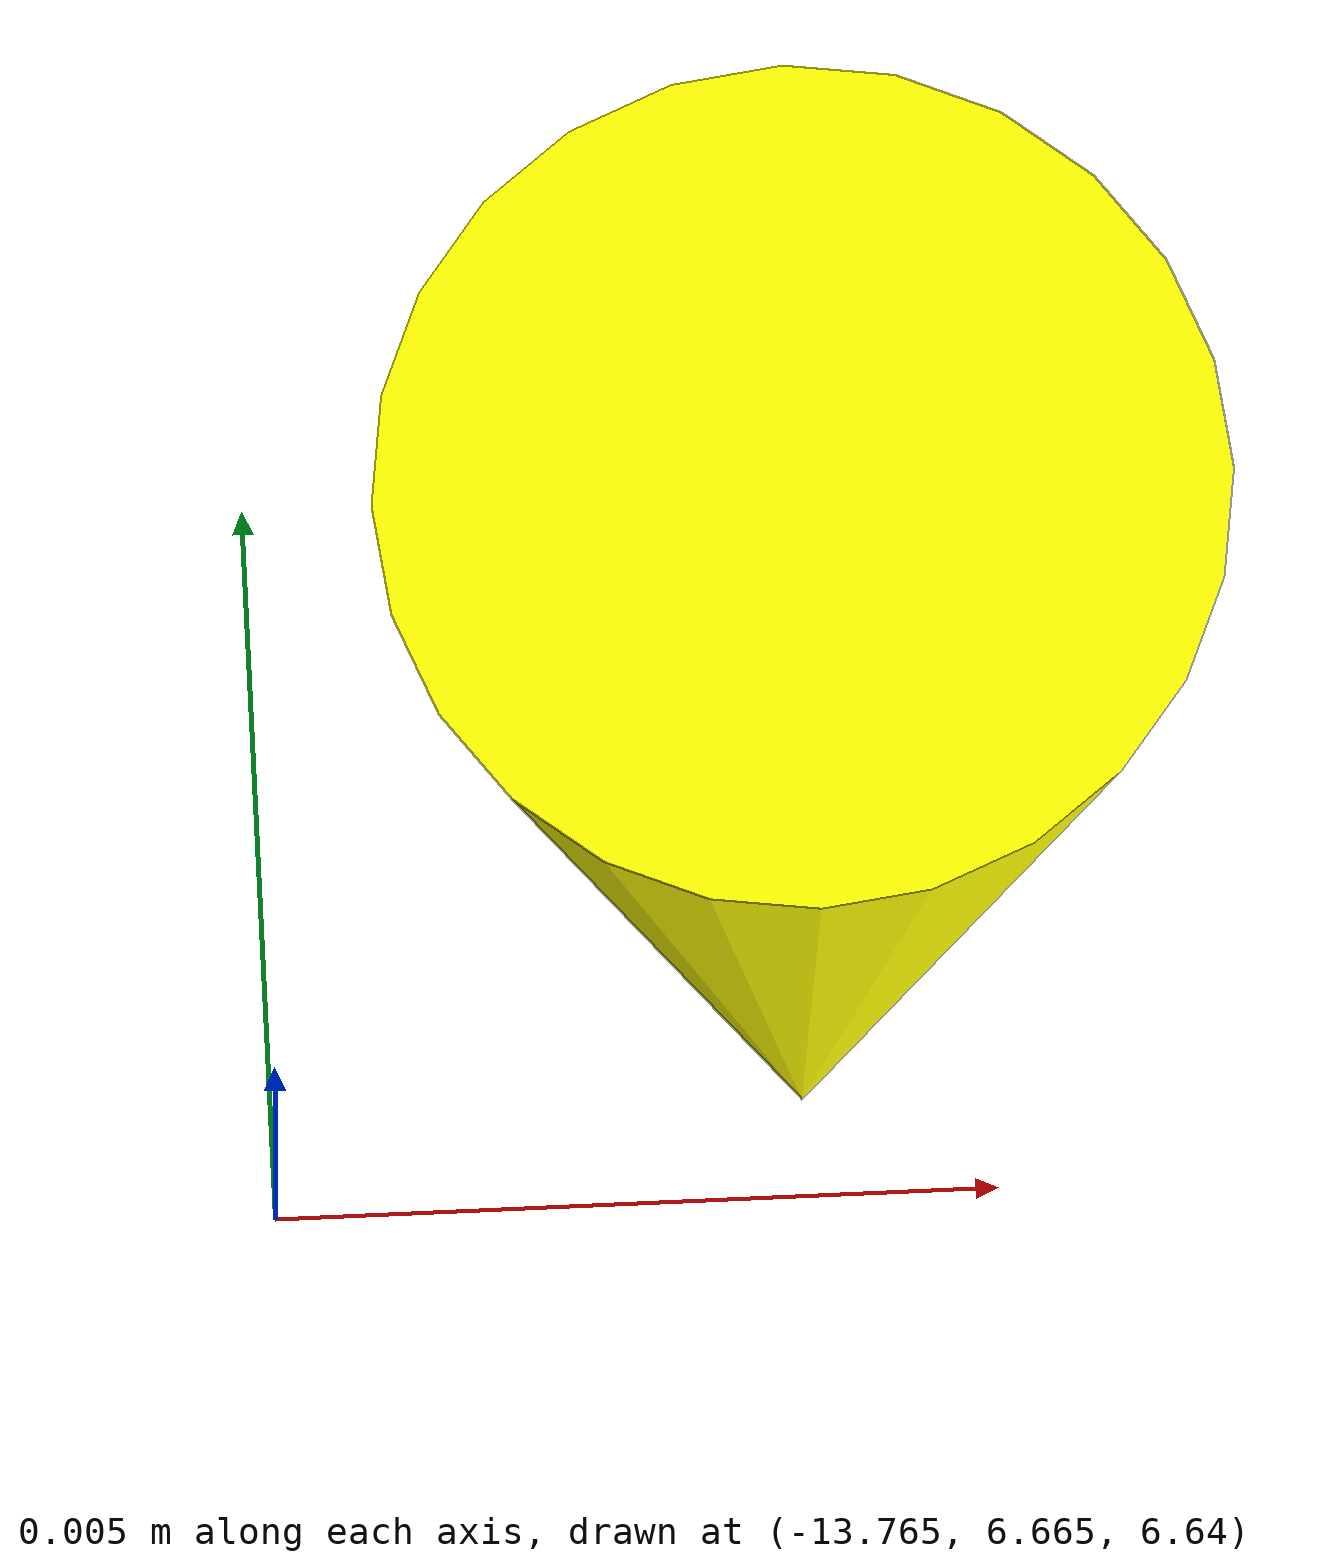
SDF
<?xml version="1.0"?>

<sdf version='1.9'>
        <!-- TRACK -->
        <model name='cones_0'>

      <link name='cone_0_link'>
        <collision name='cone_0_collision'>
          <geometry>
            <mesh>
              <uri>/models/cone/meshes/cone.stl</uri>
              <scale>0.001 0.001 0.001</scale>
            </mesh>
          </geometry>
        </collision>
        <visual name='cone_0_visual'>
          <geometry>
            <mesh>
              <uri>/models/cone/meshes/cone.stl</uri>
              <scale>0.001 0.001 0.001</scale>
            </mesh>
          </geometry>
          <material>
            <ambient>1 1 0 1</ambient>
            <diffuse>1 1 0 1</diffuse>
            <specular>1 1 0 1</specular>
          </material>
        </visual>
        <pose>5.365514631340422 19.110801933862014 0.0 1.57 0 0</pose>
        <enable_wind>false</enable_wind>
      </link>

			<static>true</static>
            <pose>5.365514631340422 19.110801933862014 0.0 1.57 0 0</pose>
            <enable_wind>false</enable_wind>
            </model>

            <model name='cones_1'>

      <link name='cone_1_link'>
        <collision name='cone_1_collision'>
          <geometry>
            <mesh>
              <uri>/models/cone/meshes/cone.stl</uri>
              <scale>0.001 0.001 0.001</scale>
            </mesh>
          </geometry>
        </collision>
        <visual name='cone_1_visual'>
          <geometry>
            <mesh>
              <uri>/models/cone/meshes/cone.stl</uri>
              <scale>0.001 0.001 0.001</scale>
            </mesh>
          </geometry>
          <material>
            <ambient>1 1 0 1</ambient>
            <diffuse>1 1 0 1</diffuse>
            <specular>1 1 0 1</specular>
          </material>
        </visual>
        <pose>5.964740565412263 19.13025210124988 0.0 1.57 0 0</pose>
        <enable_wind>false</enable_wind>
      </link>

			<static>true</static>
            <pose>5.964740565412263 19.13025210124988 0.0 1.57 0 0</pose>
            <enable_wind>false</enable_wind>
            </model>

            <model name='cones_2'>

      <link name='cone_2_link'>
        <collision name='cone_2_collision'>
          <geometry>
            <mesh>
              <uri>/models/cone/meshes/cone.stl</uri>
              <scale>0.001 0.001 0.001</scale>
            </mesh>
          </geometry>
        </collision>
        <visual name='cone_2_visual'>
          <geometry>
            <mesh>
              <uri>/models/cone/meshes/cone.stl</uri>
              <scale>0.001 0.001 0.001</scale>
            </mesh>
          </geometry>
          <material>
            <ambient>1 1 0 1</ambient>
            <diffuse>1 1 0 1</diffuse>
            <specular>1 1 0 1</specular>
          </material>
        </visual>
        <pose>6.562635671015661 19.149845757593543 0.0 1.57 0 0</pose>
        <enable_wind>false</enable_wind>
      </link>

			<static>true</static>
            <pose>6.562635671015661 19.149845757593543 0.0 1.57 0 0</pose>
            <enable_wind>false</enable_wind>
            </model>

            <model name='cones_3'>

      <link name='cone_3_link'>
        <collision name='cone_3_collision'>
          <geometry>
            <mesh>
              <uri>/models/cone/meshes/cone.stl</uri>
              <scale>0.001 0.001 0.001</scale>
            </mesh>
          </geometry>
        </collision>
        <visual name='cone_3_visual'>
          <geometry>
            <mesh>
              <uri>/models/cone/meshes/cone.stl</uri>
              <scale>0.001 0.001 0.001</scale>
            </mesh>
          </geometry>
          <material>
            <ambient>1 1 0 1</ambient>
            <diffuse>1 1 0 1</diffuse>
            <specular>1 1 0 1</specular>
          </material>
        </visual>
        <pose>7.159228228615251 19.168703466283013 0.0 1.57 0 0</pose>
        <enable_wind>false</enable_wind>
      </link>

			<static>true</static>
            <pose>7.159228228615251 19.168703466283013 0.0 1.57 0 0</pose>
            <enable_wind>false</enable_wind>
            </model>

            <model name='cones_4'>

      <link name='cone_4_link'>
        <collision name='cone_4_collision'>
          <geometry>
            <mesh>
              <uri>/models/cone/meshes/cone.stl</uri>
              <scale>0.001 0.001 0.001</scale>
            </mesh>
          </geometry>
        </collision>
        <visual name='cone_4_visual'>
          <geometry>
            <mesh>
              <uri>/models/cone/meshes/cone.stl</uri>
              <scale>0.001 0.001 0.001</scale>
            </mesh>
          </geometry>
          <material>
            <ambient>1 1 0 1</ambient>
            <diffuse>1 1 0 1</diffuse>
            <specular>1 1 0 1</specular>
          </material>
        </visual>
        <pose>7.754543277370971 19.185951549543113 0.0 1.57 0 0</pose>
        <enable_wind>false</enable_wind>
      </link>

			<static>true</static>
            <pose>7.754543277370971 19.185951549543113 0.0 1.57 0 0</pose>
            <enable_wind>false</enable_wind>
            </model>

            <model name='cones_5'>

      <link name='cone_5_link'>
        <collision name='cone_5_collision'>
          <geometry>
            <mesh>
              <uri>/models/cone/meshes/cone.stl</uri>
              <scale>0.001 0.001 0.001</scale>
            </mesh>
          </geometry>
        </collision>
        <visual name='cone_5_visual'>
          <geometry>
            <mesh>
              <uri>/models/cone/meshes/cone.stl</uri>
              <scale>0.001 0.001 0.001</scale>
            </mesh>
          </geometry>
          <material>
            <ambient>1 1 0 1</ambient>
            <diffuse>1 1 0 1</diffuse>
            <specular>1 1 0 1</specular>
          </material>
        </visual>
        <pose>8.348598776876031 19.20072199169762 0.0 1.57 0 0</pose>
        <enable_wind>false</enable_wind>
      </link>

			<static>true</static>
            <pose>8.348598776876031 19.20072199169762 0.0 1.57 0 0</pose>
            <enable_wind>false</enable_wind>
            </model>

            <model name='cones_6'>

      <link name='cone_6_link'>
        <collision name='cone_6_collision'>
          <geometry>
            <mesh>
              <uri>/models/cone/meshes/cone.stl</uri>
              <scale>0.001 0.001 0.001</scale>
            </mesh>
          </geometry>
        </collision>
        <visual name='cone_6_visual'>
          <geometry>
            <mesh>
              <uri>/models/cone/meshes/cone.stl</uri>
              <scale>0.001 0.001 0.001</scale>
            </mesh>
          </geometry>
          <material>
            <ambient>1 1 0 1</ambient>
            <diffuse>1 1 0 1</diffuse>
            <specular>1 1 0 1</specular>
          </material>
        </visual>
        <pose>10.12320195090182 19.22157188820107 0.0 1.57 0 0</pose>
        <enable_wind>false</enable_wind>
      </link>

			<static>true</static>
            <pose>10.12320195090182 19.22157188820107 0.0 1.57 0 0</pose>
            <enable_wind>false</enable_wind>
            </model>

            <model name='cones_7'>

      <link name='cone_7_link'>
        <collision name='cone_7_collision'>
          <geometry>
            <mesh>
              <uri>/models/cone/meshes/cone.stl</uri>
              <scale>0.001 0.001 0.001</scale>
            </mesh>
          </geometry>
        </collision>
        <visual name='cone_7_visual'>
          <geometry>
            <mesh>
              <uri>/models/cone/meshes/cone.stl</uri>
              <scale>0.001 0.001 0.001</scale>
            </mesh>
          </geometry>
          <material>
            <ambient>1 1 0 1</ambient>
            <diffuse>1 1 0 1</diffuse>
            <specular>1 1 0 1</specular>
          </material>
        </visual>
        <pose>10.71212526738323 19.21786514161583 0.0 1.57 0 0</pose>
        <enable_wind>false</enable_wind>
      </link>

			<static>true</static>
            <pose>10.71212526738323 19.21786514161583 0.0 1.57 0 0</pose>
            <enable_wind>false</enable_wind>
            </model>

            <model name='cones_8'>

      <link name='cone_8_link'>
        <collision name='cone_8_collision'>
          <geometry>
            <mesh>
              <uri>/models/cone/meshes/cone.stl</uri>
              <scale>0.001 0.001 0.001</scale>
            </mesh>
          </geometry>
        </collision>
        <visual name='cone_8_visual'>
          <geometry>
            <mesh>
              <uri>/models/cone/meshes/cone.stl</uri>
              <scale>0.001 0.001 0.001</scale>
            </mesh>
          </geometry>
          <material>
            <ambient>1 1 0 1</ambient>
            <diffuse>1 1 0 1</diffuse>
            <specular>1 1 0 1</specular>
          </material>
        </visual>
        <pose>11.299641250748362 19.20742738967495 0.0 1.57 0 0</pose>
        <enable_wind>false</enable_wind>
      </link>

			<static>true</static>
            <pose>11.299641250748362 19.20742738967495 0.0 1.57 0 0</pose>
            <enable_wind>false</enable_wind>
            </model>

            <model name='cones_9'>

      <link name='cone_9_link'>
        <collision name='cone_9_collision'>
          <geometry>
            <mesh>
              <uri>/models/cone/meshes/cone.stl</uri>
              <scale>0.001 0.001 0.001</scale>
            </mesh>
          </geometry>
        </collision>
        <visual name='cone_9_visual'>
          <geometry>
            <mesh>
              <uri>/models/cone/meshes/cone.stl</uri>
              <scale>0.001 0.001 0.001</scale>
            </mesh>
          </geometry>
          <material>
            <ambient>1 1 0 1</ambient>
            <diffuse>1 1 0 1</diffuse>
            <specular>1 1 0 1</specular>
          </material>
        </visual>
        <pose>11.88564717200543 19.189427374825613 0.0 1.57 0 0</pose>
        <enable_wind>false</enable_wind>
      </link>

			<static>true</static>
            <pose>11.88564717200543 19.189427374825613 0.0 1.57 0 0</pose>
            <enable_wind>false</enable_wind>
            </model>

            <model name='cones_10'>

      <link name='cone_10_link'>
        <collision name='cone_10_collision'>
          <geometry>
            <mesh>
              <uri>/models/cone/meshes/cone.stl</uri>
              <scale>0.001 0.001 0.001</scale>
            </mesh>
          </geometry>
        </collision>
        <visual name='cone_10_visual'>
          <geometry>
            <mesh>
              <uri>/models/cone/meshes/cone.stl</uri>
              <scale>0.001 0.001 0.001</scale>
            </mesh>
          </geometry>
          <material>
            <ambient>1 1 0 1</ambient>
            <diffuse>1 1 0 1</diffuse>
            <specular>1 1 0 1</specular>
          </material>
        </visual>
        <pose>12.47000759521337 19.16304179481803 0.0 1.57 0 0</pose>
        <enable_wind>false</enable_wind>
      </link>

			<static>true</static>
            <pose>12.47000759521337 19.16304179481803 0.0 1.57 0 0</pose>
            <enable_wind>false</enable_wind>
            </model>

            <model name='cones_11'>

      <link name='cone_11_link'>
        <collision name='cone_11_collision'>
          <geometry>
            <mesh>
              <uri>/models/cone/meshes/cone.stl</uri>
              <scale>0.001 0.001 0.001</scale>
            </mesh>
          </geometry>
        </collision>
        <visual name='cone_11_visual'>
          <geometry>
            <mesh>
              <uri>/models/cone/meshes/cone.stl</uri>
              <scale>0.001 0.001 0.001</scale>
            </mesh>
          </geometry>
          <material>
            <ambient>1 1 0 1</ambient>
            <diffuse>1 1 0 1</diffuse>
            <specular>1 1 0 1</specular>
          </material>
        </visual>
        <pose>13.041051502435192 19.12601093430245 0.0 1.57 0 0</pose>
        <enable_wind>false</enable_wind>
      </link>

			<static>true</static>
            <pose>13.041051502435192 19.12601093430245 0.0 1.57 0 0</pose>
            <enable_wind>false</enable_wind>
            </model>

            <model name='cones_12'>

      <link name='cone_12_link'>
        <collision name='cone_12_collision'>
          <geometry>
            <mesh>
              <uri>/models/cone/meshes/cone.stl</uri>
              <scale>0.001 0.001 0.001</scale>
            </mesh>
          </geometry>
        </collision>
        <visual name='cone_12_visual'>
          <geometry>
            <mesh>
              <uri>/models/cone/meshes/cone.stl</uri>
              <scale>0.001 0.001 0.001</scale>
            </mesh>
          </geometry>
          <material>
            <ambient>1 1 0 1</ambient>
            <diffuse>1 1 0 1</diffuse>
            <specular>1 1 0 1</specular>
          </material>
        </visual>
        <pose>13.581689096199652 19.06655367674996 0.0 1.57 0 0</pose>
        <enable_wind>false</enable_wind>
      </link>

			<static>true</static>
            <pose>13.581689096199652 19.06655367674996 0.0 1.57 0 0</pose>
            <enable_wind>false</enable_wind>
            </model>

            <model name='cones_13'>

      <link name='cone_13_link'>
        <collision name='cone_13_collision'>
          <geometry>
            <mesh>
              <uri>/models/cone/meshes/cone.stl</uri>
              <scale>0.001 0.001 0.001</scale>
            </mesh>
          </geometry>
        </collision>
        <visual name='cone_13_visual'>
          <geometry>
            <mesh>
              <uri>/models/cone/meshes/cone.stl</uri>
              <scale>0.001 0.001 0.001</scale>
            </mesh>
          </geometry>
          <material>
            <ambient>1 1 0 1</ambient>
            <diffuse>1 1 0 1</diffuse>
            <specular>1 1 0 1</specular>
          </material>
        </visual>
        <pose>14.55431448947459 18.83039695679588 0.0 1.57 0 0</pose>
        <enable_wind>false</enable_wind>
      </link>

			<static>true</static>
            <pose>14.55431448947459 18.83039695679588 0.0 1.57 0 0</pose>
            <enable_wind>false</enable_wind>
            </model>

            <model name='cones_14'>

      <link name='cone_14_link'>
        <collision name='cone_14_collision'>
          <geometry>
            <mesh>
              <uri>/models/cone/meshes/cone.stl</uri>
              <scale>0.001 0.001 0.001</scale>
            </mesh>
          </geometry>
        </collision>
        <visual name='cone_14_visual'>
          <geometry>
            <mesh>
              <uri>/models/cone/meshes/cone.stl</uri>
              <scale>0.001 0.001 0.001</scale>
            </mesh>
          </geometry>
          <material>
            <ambient>1 1 0 1</ambient>
            <diffuse>1 1 0 1</diffuse>
            <specular>1 1 0 1</specular>
          </material>
        </visual>
        <pose>14.97041312626016 18.63808357122464 0.0 1.57 0 0</pose>
        <enable_wind>false</enable_wind>
      </link>

			<static>true</static>
            <pose>14.97041312626016 18.63808357122464 0.0 1.57 0 0</pose>
            <enable_wind>false</enable_wind>
            </model>

            <model name='cones_15'>

      <link name='cone_15_link'>
        <collision name='cone_15_collision'>
          <geometry>
            <mesh>
              <uri>/models/cone/meshes/cone.stl</uri>
              <scale>0.001 0.001 0.001</scale>
            </mesh>
          </geometry>
        </collision>
        <visual name='cone_15_visual'>
          <geometry>
            <mesh>
              <uri>/models/cone/meshes/cone.stl</uri>
              <scale>0.001 0.001 0.001</scale>
            </mesh>
          </geometry>
          <material>
            <ambient>1 1 0 1</ambient>
            <diffuse>1 1 0 1</diffuse>
            <specular>1 1 0 1</specular>
          </material>
        </visual>
        <pose>15.64211758381664 18.078554715443932 0.0 1.57 0 0</pose>
        <enable_wind>false</enable_wind>
      </link>

			<static>true</static>
            <pose>15.64211758381664 18.078554715443932 0.0 1.57 0 0</pose>
            <enable_wind>false</enable_wind>
            </model>

            <model name='cones_16'>

      <link name='cone_16_link'>
        <collision name='cone_16_collision'>
          <geometry>
            <mesh>
              <uri>/models/cone/meshes/cone.stl</uri>
              <scale>0.001 0.001 0.001</scale>
            </mesh>
          </geometry>
        </collision>
        <visual name='cone_16_visual'>
          <geometry>
            <mesh>
              <uri>/models/cone/meshes/cone.stl</uri>
              <scale>0.001 0.001 0.001</scale>
            </mesh>
          </geometry>
          <material>
            <ambient>1 1 0 1</ambient>
            <diffuse>1 1 0 1</diffuse>
            <specular>1 1 0 1</specular>
          </material>
        </visual>
        <pose>15.910013498130139 17.706310771870402 0.0 1.57 0 0</pose>
        <enable_wind>false</enable_wind>
      </link>

			<static>true</static>
            <pose>15.910013498130139 17.706310771870402 0.0 1.57 0 0</pose>
            <enable_wind>false</enable_wind>
            </model>

            <model name='cones_17'>

      <link name='cone_17_link'>
        <collision name='cone_17_collision'>
          <geometry>
            <mesh>
              <uri>/models/cone/meshes/cone.stl</uri>
              <scale>0.001 0.001 0.001</scale>
            </mesh>
          </geometry>
        </collision>
        <visual name='cone_17_visual'>
          <geometry>
            <mesh>
              <uri>/models/cone/meshes/cone.stl</uri>
              <scale>0.001 0.001 0.001</scale>
            </mesh>
          </geometry>
          <material>
            <ambient>1 1 0 1</ambient>
            <diffuse>1 1 0 1</diffuse>
            <specular>1 1 0 1</specular>
          </material>
        </visual>
        <pose>16.1277216977834 17.285362386631014 0.0 1.57 0 0</pose>
        <enable_wind>false</enable_wind>
      </link>

			<static>true</static>
            <pose>16.1277216977834 17.285362386631014 0.0 1.57 0 0</pose>
            <enable_wind>false</enable_wind>
            </model>

            <model name='cones_18'>

      <link name='cone_18_link'>
        <collision name='cone_18_collision'>
          <geometry>
            <mesh>
              <uri>/models/cone/meshes/cone.stl</uri>
              <scale>0.001 0.001 0.001</scale>
            </mesh>
          </geometry>
        </collision>
        <visual name='cone_18_visual'>
          <geometry>
            <mesh>
              <uri>/models/cone/meshes/cone.stl</uri>
              <scale>0.001 0.001 0.001</scale>
            </mesh>
          </geometry>
          <material>
            <ambient>1 1 0 1</ambient>
            <diffuse>1 1 0 1</diffuse>
            <specular>1 1 0 1</specular>
          </material>
        </visual>
        <pose>16.294295500331152 16.825754413038084 0.0 1.57 0 0</pose>
        <enable_wind>false</enable_wind>
      </link>

			<static>true</static>
            <pose>16.294295500331152 16.825754413038084 0.0 1.57 0 0</pose>
            <enable_wind>false</enable_wind>
            </model>

            <model name='cones_19'>

      <link name='cone_19_link'>
        <collision name='cone_19_collision'>
          <geometry>
            <mesh>
              <uri>/models/cone/meshes/cone.stl</uri>
              <scale>0.001 0.001 0.001</scale>
            </mesh>
          </geometry>
        </collision>
        <visual name='cone_19_visual'>
          <geometry>
            <mesh>
              <uri>/models/cone/meshes/cone.stl</uri>
              <scale>0.001 0.001 0.001</scale>
            </mesh>
          </geometry>
          <material>
            <ambient>1 1 0 1</ambient>
            <diffuse>1 1 0 1</diffuse>
            <specular>1 1 0 1</specular>
          </material>
        </visual>
        <pose>16.45404444091331 15.871680009410992 0.0 1.57 0 0</pose>
        <enable_wind>false</enable_wind>
      </link>

			<static>true</static>
            <pose>16.45404444091331 15.871680009410992 0.0 1.57 0 0</pose>
            <enable_wind>false</enable_wind>
            </model>

            <model name='cones_20'>

      <link name='cone_20_link'>
        <collision name='cone_20_collision'>
          <geometry>
            <mesh>
              <uri>/models/cone/meshes/cone.stl</uri>
              <scale>0.001 0.001 0.001</scale>
            </mesh>
          </geometry>
        </collision>
        <visual name='cone_20_visual'>
          <geometry>
            <mesh>
              <uri>/models/cone/meshes/cone.stl</uri>
              <scale>0.001 0.001 0.001</scale>
            </mesh>
          </geometry>
          <material>
            <ambient>1 1 0 1</ambient>
            <diffuse>1 1 0 1</diffuse>
            <specular>1 1 0 1</specular>
          </material>
        </visual>
        <pose>16.43842788566033 15.399601279681972 0.0 1.57 0 0</pose>
        <enable_wind>false</enable_wind>
      </link>

			<static>true</static>
            <pose>16.43842788566033 15.399601279681972 0.0 1.57 0 0</pose>
            <enable_wind>false</enable_wind>
            </model>

            <model name='cones_21'>

      <link name='cone_21_link'>
        <collision name='cone_21_collision'>
          <geometry>
            <mesh>
              <uri>/models/cone/meshes/cone.stl</uri>
              <scale>0.001 0.001 0.001</scale>
            </mesh>
          </geometry>
        </collision>
        <visual name='cone_21_visual'>
          <geometry>
            <mesh>
              <uri>/models/cone/meshes/cone.stl</uri>
              <scale>0.001 0.001 0.001</scale>
            </mesh>
          </geometry>
          <material>
            <ambient>1 1 0 1</ambient>
            <diffuse>1 1 0 1</diffuse>
            <specular>1 1 0 1</specular>
          </material>
        </visual>
        <pose>16.356500140432672 14.942758602394552 0.0 1.57 0 0</pose>
        <enable_wind>false</enable_wind>
      </link>

			<static>true</static>
            <pose>16.356500140432672 14.942758602394552 0.0 1.57 0 0</pose>
            <enable_wind>false</enable_wind>
            </model>

            <model name='cones_22'>

      <link name='cone_22_link'>
        <collision name='cone_22_collision'>
          <geometry>
            <mesh>
              <uri>/models/cone/meshes/cone.stl</uri>
              <scale>0.001 0.001 0.001</scale>
            </mesh>
          </geometry>
        </collision>
        <visual name='cone_22_visual'>
          <geometry>
            <mesh>
              <uri>/models/cone/meshes/cone.stl</uri>
              <scale>0.001 0.001 0.001</scale>
            </mesh>
          </geometry>
          <material>
            <ambient>1 1 0 1</ambient>
            <diffuse>1 1 0 1</diffuse>
            <specular>1 1 0 1</specular>
          </material>
        </visual>
        <pose>16.20837454523762 14.511568577870843 0.0 1.57 0 0</pose>
        <enable_wind>false</enable_wind>
      </link>

			<static>true</static>
            <pose>16.20837454523762 14.511568577870843 0.0 1.57 0 0</pose>
            <enable_wind>false</enable_wind>
            </model>

            <model name='cones_23'>

      <link name='cone_23_link'>
        <collision name='cone_23_collision'>
          <geometry>
            <mesh>
              <uri>/models/cone/meshes/cone.stl</uri>
              <scale>0.001 0.001 0.001</scale>
            </mesh>
          </geometry>
        </collision>
        <visual name='cone_23_visual'>
          <geometry>
            <mesh>
              <uri>/models/cone/meshes/cone.stl</uri>
              <scale>0.001 0.001 0.001</scale>
            </mesh>
          </geometry>
          <material>
            <ambient>1 1 0 1</ambient>
            <diffuse>1 1 0 1</diffuse>
            <specular>1 1 0 1</specular>
          </material>
        </visual>
        <pose>15.99358132323365 14.11083754486181 0.0 1.57 0 0</pose>
        <enable_wind>false</enable_wind>
      </link>

			<static>true</static>
            <pose>15.99358132323365 14.11083754486181 0.0 1.57 0 0</pose>
            <enable_wind>false</enable_wind>
            </model>

            <model name='cones_24'>

      <link name='cone_24_link'>
        <collision name='cone_24_collision'>
          <geometry>
            <mesh>
              <uri>/models/cone/meshes/cone.stl</uri>
              <scale>0.001 0.001 0.001</scale>
            </mesh>
          </geometry>
        </collision>
        <visual name='cone_24_visual'>
          <geometry>
            <mesh>
              <uri>/models/cone/meshes/cone.stl</uri>
              <scale>0.001 0.001 0.001</scale>
            </mesh>
          </geometry>
          <material>
            <ambient>1 1 0 1</ambient>
            <diffuse>1 1 0 1</diffuse>
            <specular>1 1 0 1</specular>
          </material>
        </visual>
        <pose>15.371974790252331 13.391132889904732 0.0 1.57 0 0</pose>
        <enable_wind>false</enable_wind>
      </link>

			<static>true</static>
            <pose>15.371974790252331 13.391132889904732 0.0 1.57 0 0</pose>
            <enable_wind>false</enable_wind>
            </model>

            <model name='cones_25'>

      <link name='cone_25_link'>
        <collision name='cone_25_collision'>
          <geometry>
            <mesh>
              <uri>/models/cone/meshes/cone.stl</uri>
              <scale>0.001 0.001 0.001</scale>
            </mesh>
          </geometry>
        </collision>
        <visual name='cone_25_visual'>
          <geometry>
            <mesh>
              <uri>/models/cone/meshes/cone.stl</uri>
              <scale>0.001 0.001 0.001</scale>
            </mesh>
          </geometry>
          <material>
            <ambient>1 1 0 1</ambient>
            <diffuse>1 1 0 1</diffuse>
            <specular>1 1 0 1</specular>
          </material>
        </visual>
        <pose>14.55709628279117 12.808898370122453 0.0 1.57 0 0</pose>
        <enable_wind>false</enable_wind>
      </link>

			<static>true</static>
            <pose>14.55709628279117 12.808898370122453 0.0 1.57 0 0</pose>
            <enable_wind>false</enable_wind>
            </model>

            <model name='cones_26'>

      <link name='cone_26_link'>
        <collision name='cone_26_collision'>
          <geometry>
            <mesh>
              <uri>/models/cone/meshes/cone.stl</uri>
              <scale>0.001 0.001 0.001</scale>
            </mesh>
          </geometry>
        </collision>
        <visual name='cone_26_visual'>
          <geometry>
            <mesh>
              <uri>/models/cone/meshes/cone.stl</uri>
              <scale>0.001 0.001 0.001</scale>
            </mesh>
          </geometry>
          <material>
            <ambient>1 1 0 1</ambient>
            <diffuse>1 1 0 1</diffuse>
            <specular>1 1 0 1</specular>
          </material>
        </visual>
        <pose>14.11033563835196 12.587555216181531 0.0 1.57 0 0</pose>
        <enable_wind>false</enable_wind>
      </link>

			<static>true</static>
            <pose>14.11033563835196 12.587555216181531 0.0 1.57 0 0</pose>
            <enable_wind>false</enable_wind>
            </model>

            <model name='cones_27'>

      <link name='cone_27_link'>
        <collision name='cone_27_collision'>
          <geometry>
            <mesh>
              <uri>/models/cone/meshes/cone.stl</uri>
              <scale>0.001 0.001 0.001</scale>
            </mesh>
          </geometry>
        </collision>
        <visual name='cone_27_visual'>
          <geometry>
            <mesh>
              <uri>/models/cone/meshes/cone.stl</uri>
              <scale>0.001 0.001 0.001</scale>
            </mesh>
          </geometry>
          <material>
            <ambient>1 1 0 1</ambient>
            <diffuse>1 1 0 1</diffuse>
            <specular>1 1 0 1</specular>
          </material>
        </visual>
        <pose>13.646279059230352 12.420128168078872 0.0 1.57 0 0</pose>
        <enable_wind>false</enable_wind>
      </link>

			<static>true</static>
            <pose>13.646279059230352 12.420128168078872 0.0 1.57 0 0</pose>
            <enable_wind>false</enable_wind>
            </model>

            <model name='cones_28'>

      <link name='cone_28_link'>
        <collision name='cone_28_collision'>
          <geometry>
            <mesh>
              <uri>/models/cone/meshes/cone.stl</uri>
              <scale>0.001 0.001 0.001</scale>
            </mesh>
          </geometry>
        </collision>
        <visual name='cone_28_visual'>
          <geometry>
            <mesh>
              <uri>/models/cone/meshes/cone.stl</uri>
              <scale>0.001 0.001 0.001</scale>
            </mesh>
          </geometry>
          <material>
            <ambient>1 1 0 1</ambient>
            <diffuse>1 1 0 1</diffuse>
            <specular>1 1 0 1</specular>
          </material>
        </visual>
        <pose>13.17068350719518 12.310419448693313 0.0 1.57 0 0</pose>
        <enable_wind>false</enable_wind>
      </link>

			<static>true</static>
            <pose>13.17068350719518 12.310419448693313 0.0 1.57 0 0</pose>
            <enable_wind>false</enable_wind>
            </model>

            <model name='cones_29'>

      <link name='cone_29_link'>
        <collision name='cone_29_collision'>
          <geometry>
            <mesh>
              <uri>/models/cone/meshes/cone.stl</uri>
              <scale>0.001 0.001 0.001</scale>
            </mesh>
          </geometry>
        </collision>
        <visual name='cone_29_visual'>
          <geometry>
            <mesh>
              <uri>/models/cone/meshes/cone.stl</uri>
              <scale>0.001 0.001 0.001</scale>
            </mesh>
          </geometry>
          <material>
            <ambient>1 1 0 1</ambient>
            <diffuse>1 1 0 1</diffuse>
            <specular>1 1 0 1</specular>
          </material>
        </visual>
        <pose>12.69032803057931 12.261562816865302 0.0 1.57 0 0</pose>
        <enable_wind>false</enable_wind>
      </link>

			<static>true</static>
            <pose>12.69032803057931 12.261562816865302 0.0 1.57 0 0</pose>
            <enable_wind>false</enable_wind>
            </model>

            <model name='cones_30'>

      <link name='cone_30_link'>
        <collision name='cone_30_collision'>
          <geometry>
            <mesh>
              <uri>/models/cone/meshes/cone.stl</uri>
              <scale>0.001 0.001 0.001</scale>
            </mesh>
          </geometry>
        </collision>
        <visual name='cone_30_visual'>
          <geometry>
            <mesh>
              <uri>/models/cone/meshes/cone.stl</uri>
              <scale>0.001 0.001 0.001</scale>
            </mesh>
          </geometry>
          <material>
            <ambient>1 1 0 1</ambient>
            <diffuse>1 1 0 1</diffuse>
            <specular>1 1 0 1</specular>
          </material>
        </visual>
        <pose>12.20867904572405 12.275499276402233 0.0 1.57 0 0</pose>
        <enable_wind>false</enable_wind>
      </link>

			<static>true</static>
            <pose>12.20867904572405 12.275499276402233 0.0 1.57 0 0</pose>
            <enable_wind>false</enable_wind>
            </model>

            <model name='cones_31'>

      <link name='cone_31_link'>
        <collision name='cone_31_collision'>
          <geometry>
            <mesh>
              <uri>/models/cone/meshes/cone.stl</uri>
              <scale>0.001 0.001 0.001</scale>
            </mesh>
          </geometry>
        </collision>
        <visual name='cone_31_visual'>
          <geometry>
            <mesh>
              <uri>/models/cone/meshes/cone.stl</uri>
              <scale>0.001 0.001 0.001</scale>
            </mesh>
          </geometry>
          <material>
            <ambient>1 1 0 1</ambient>
            <diffuse>1 1 0 1</diffuse>
            <specular>1 1 0 1</specular>
          </material>
        </visual>
        <pose>11.722728008294931 12.350486889681113 0.0 1.57 0 0</pose>
        <enable_wind>false</enable_wind>
      </link>

			<static>true</static>
            <pose>11.722728008294931 12.350486889681113 0.0 1.57 0 0</pose>
            <enable_wind>false</enable_wind>
            </model>

            <model name='cones_32'>

      <link name='cone_32_link'>
        <collision name='cone_32_collision'>
          <geometry>
            <mesh>
              <uri>/models/cone/meshes/cone.stl</uri>
              <scale>0.001 0.001 0.001</scale>
            </mesh>
          </geometry>
        </collision>
        <visual name='cone_32_visual'>
          <geometry>
            <mesh>
              <uri>/models/cone/meshes/cone.stl</uri>
              <scale>0.001 0.001 0.001</scale>
            </mesh>
          </geometry>
          <material>
            <ambient>1 1 0 1</ambient>
            <diffuse>1 1 0 1</diffuse>
            <specular>1 1 0 1</specular>
          </material>
        </visual>
        <pose>10.75994651673809 12.66625218214823 0.0 1.57 0 0</pose>
        <enable_wind>false</enable_wind>
      </link>

			<static>true</static>
            <pose>10.75994651673809 12.66625218214823 0.0 1.57 0 0</pose>
            <enable_wind>false</enable_wind>
            </model>

            <model name='cones_33'>

      <link name='cone_33_link'>
        <collision name='cone_33_collision'>
          <geometry>
            <mesh>
              <uri>/models/cone/meshes/cone.stl</uri>
              <scale>0.001 0.001 0.001</scale>
            </mesh>
          </geometry>
        </collision>
        <visual name='cone_33_visual'>
          <geometry>
            <mesh>
              <uri>/models/cone/meshes/cone.stl</uri>
              <scale>0.001 0.001 0.001</scale>
            </mesh>
          </geometry>
          <material>
            <ambient>1 1 0 1</ambient>
            <diffuse>1 1 0 1</diffuse>
            <specular>1 1 0 1</specular>
          </material>
        </visual>
        <pose>9.827743761109641 13.170460850358321 0.0 1.57 0 0</pose>
        <enable_wind>false</enable_wind>
      </link>

			<static>true</static>
            <pose>9.827743761109641 13.170460850358321 0.0 1.57 0 0</pose>
            <enable_wind>false</enable_wind>
            </model>

            <model name='cones_34'>

      <link name='cone_34_link'>
        <collision name='cone_34_collision'>
          <geometry>
            <mesh>
              <uri>/models/cone/meshes/cone.stl</uri>
              <scale>0.001 0.001 0.001</scale>
            </mesh>
          </geometry>
        </collision>
        <visual name='cone_34_visual'>
          <geometry>
            <mesh>
              <uri>/models/cone/meshes/cone.stl</uri>
              <scale>0.001 0.001 0.001</scale>
            </mesh>
          </geometry>
          <material>
            <ambient>1 1 0 1</ambient>
            <diffuse>1 1 0 1</diffuse>
            <specular>1 1 0 1</specular>
          </material>
        </visual>
        <pose>9.359338739919142 13.482384021496312 0.0 1.57 0 0</pose>
        <enable_wind>false</enable_wind>
      </link>

			<static>true</static>
            <pose>9.359338739919142 13.482384021496312 0.0 1.57 0 0</pose>
            <enable_wind>false</enable_wind>
            </model>

            <model name='cones_35'>

      <link name='cone_35_link'>
        <collision name='cone_35_collision'>
          <geometry>
            <mesh>
              <uri>/models/cone/meshes/cone.stl</uri>
              <scale>0.001 0.001 0.001</scale>
            </mesh>
          </geometry>
        </collision>
        <visual name='cone_35_visual'>
          <geometry>
            <mesh>
              <uri>/models/cone/meshes/cone.stl</uri>
              <scale>0.001 0.001 0.001</scale>
            </mesh>
          </geometry>
          <material>
            <ambient>1 1 0 1</ambient>
            <diffuse>1 1 0 1</diffuse>
            <specular>1 1 0 1</specular>
          </material>
        </visual>
        <pose>8.87839159937207 13.820768859629933 0.0 1.57 0 0</pose>
        <enable_wind>false</enable_wind>
      </link>

			<static>true</static>
            <pose>8.87839159937207 13.820768859629933 0.0 1.57 0 0</pose>
            <enable_wind>false</enable_wind>
            </model>

            <model name='cones_36'>

      <link name='cone_36_link'>
        <collision name='cone_36_collision'>
          <geometry>
            <mesh>
              <uri>/models/cone/meshes/cone.stl</uri>
              <scale>0.001 0.001 0.001</scale>
            </mesh>
          </geometry>
        </collision>
        <visual name='cone_36_visual'>
          <geometry>
            <mesh>
              <uri>/models/cone/meshes/cone.stl</uri>
              <scale>0.001 0.001 0.001</scale>
            </mesh>
          </geometry>
          <material>
            <ambient>1 1 0 1</ambient>
            <diffuse>1 1 0 1</diffuse>
            <specular>1 1 0 1</specular>
          </material>
        </visual>
        <pose>8.37592777156742 14.172470621296402 0.0 1.57 0 0</pose>
        <enable_wind>false</enable_wind>
      </link>

			<static>true</static>
            <pose>8.37592777156742 14.172470621296402 0.0 1.57 0 0</pose>
            <enable_wind>false</enable_wind>
            </model>

            <model name='cones_37'>

      <link name='cone_37_link'>
        <collision name='cone_37_collision'>
          <geometry>
            <mesh>
              <uri>/models/cone/meshes/cone.stl</uri>
              <scale>0.001 0.001 0.001</scale>
            </mesh>
          </geometry>
        </collision>
        <visual name='cone_37_visual'>
          <geometry>
            <mesh>
              <uri>/models/cone/meshes/cone.stl</uri>
              <scale>0.001 0.001 0.001</scale>
            </mesh>
          </geometry>
          <material>
            <ambient>1 1 0 1</ambient>
            <diffuse>1 1 0 1</diffuse>
            <specular>1 1 0 1</specular>
          </material>
        </visual>
        <pose>7.841881389339381 14.522514218116822 0.0 1.57 0 0</pose>
        <enable_wind>false</enable_wind>
      </link>

			<static>true</static>
            <pose>7.841881389339381 14.522514218116822 0.0 1.57 0 0</pose>
            <enable_wind>false</enable_wind>
            </model>

            <model name='cones_38'>

      <link name='cone_38_link'>
        <collision name='cone_38_collision'>
          <geometry>
            <mesh>
              <uri>/models/cone/meshes/cone.stl</uri>
              <scale>0.001 0.001 0.001</scale>
            </mesh>
          </geometry>
        </collision>
        <visual name='cone_38_visual'>
          <geometry>
            <mesh>
              <uri>/models/cone/meshes/cone.stl</uri>
              <scale>0.001 0.001 0.001</scale>
            </mesh>
          </geometry>
          <material>
            <ambient>1 1 0 1</ambient>
            <diffuse>1 1 0 1</diffuse>
            <specular>1 1 0 1</specular>
          </material>
        </visual>
        <pose>6.644158103725881 15.142816129841933 0.0 1.57 0 0</pose>
        <enable_wind>false</enable_wind>
      </link>

			<static>true</static>
            <pose>6.644158103725881 15.142816129841933 0.0 1.57 0 0</pose>
            <enable_wind>false</enable_wind>
            </model>

            <model name='cones_39'>

      <link name='cone_39_link'>
        <collision name='cone_39_collision'>
          <geometry>
            <mesh>
              <uri>/models/cone/meshes/cone.stl</uri>
              <scale>0.001 0.001 0.001</scale>
            </mesh>
          </geometry>
        </collision>
        <visual name='cone_39_visual'>
          <geometry>
            <mesh>
              <uri>/models/cone/meshes/cone.stl</uri>
              <scale>0.001 0.001 0.001</scale>
            </mesh>
          </geometry>
          <material>
            <ambient>1 1 0 1</ambient>
            <diffuse>1 1 0 1</diffuse>
            <specular>1 1 0 1</specular>
          </material>
        </visual>
        <pose>5.994280226002788 15.369261972425512 0.0 1.57 0 0</pose>
        <enable_wind>false</enable_wind>
      </link>

			<static>true</static>
            <pose>5.994280226002788 15.369261972425512 0.0 1.57 0 0</pose>
            <enable_wind>false</enable_wind>
            </model>

            <model name='cones_40'>

      <link name='cone_40_link'>
        <collision name='cone_40_collision'>
          <geometry>
            <mesh>
              <uri>/models/cone/meshes/cone.stl</uri>
              <scale>0.001 0.001 0.001</scale>
            </mesh>
          </geometry>
        </collision>
        <visual name='cone_40_visual'>
          <geometry>
            <mesh>
              <uri>/models/cone/meshes/cone.stl</uri>
              <scale>0.001 0.001 0.001</scale>
            </mesh>
          </geometry>
          <material>
            <ambient>1 1 0 1</ambient>
            <diffuse>1 1 0 1</diffuse>
            <specular>1 1 0 1</specular>
          </material>
        </visual>
        <pose>5.328083554993176 15.530176551073524 0.0 1.57 0 0</pose>
        <enable_wind>false</enable_wind>
      </link>

			<static>true</static>
            <pose>5.328083554993176 15.530176551073524 0.0 1.57 0 0</pose>
            <enable_wind>false</enable_wind>
            </model>

            <model name='cones_41'>

      <link name='cone_41_link'>
        <collision name='cone_41_collision'>
          <geometry>
            <mesh>
              <uri>/models/cone/meshes/cone.stl</uri>
              <scale>0.001 0.001 0.001</scale>
            </mesh>
          </geometry>
        </collision>
        <visual name='cone_41_visual'>
          <geometry>
            <mesh>
              <uri>/models/cone/meshes/cone.stl</uri>
              <scale>0.001 0.001 0.001</scale>
            </mesh>
          </geometry>
          <material>
            <ambient>1 1 0 1</ambient>
            <diffuse>1 1 0 1</diffuse>
            <specular>1 1 0 1</specular>
          </material>
        </visual>
        <pose>4.652433858492414 15.62669971034861 0.0 1.57 0 0</pose>
        <enable_wind>false</enable_wind>
      </link>

			<static>true</static>
            <pose>4.652433858492414 15.62669971034861 0.0 1.57 0 0</pose>
            <enable_wind>false</enable_wind>
            </model>

            <model name='cones_42'>

      <link name='cone_42_link'>
        <collision name='cone_42_collision'>
          <geometry>
            <mesh>
              <uri>/models/cone/meshes/cone.stl</uri>
              <scale>0.001 0.001 0.001</scale>
            </mesh>
          </geometry>
        </collision>
        <visual name='cone_42_visual'>
          <geometry>
            <mesh>
              <uri>/models/cone/meshes/cone.stl</uri>
              <scale>0.001 0.001 0.001</scale>
            </mesh>
          </geometry>
          <material>
            <ambient>1 1 0 1</ambient>
            <diffuse>1 1 0 1</diffuse>
            <specular>1 1 0 1</specular>
          </material>
        </visual>
        <pose>3.295381193714981 15.634145905023022 0.0 1.57 0 0</pose>
        <enable_wind>false</enable_wind>
      </link>

			<static>true</static>
            <pose>3.295381193714981 15.634145905023022 0.0 1.57 0 0</pose>
            <enable_wind>false</enable_wind>
            </model>

            <model name='cones_43'>

      <link name='cone_43_link'>
        <collision name='cone_43_collision'>
          <geometry>
            <mesh>
              <uri>/models/cone/meshes/cone.stl</uri>
              <scale>0.001 0.001 0.001</scale>
            </mesh>
          </geometry>
        </collision>
        <visual name='cone_43_visual'>
          <geometry>
            <mesh>
              <uri>/models/cone/meshes/cone.stl</uri>
              <scale>0.001 0.001 0.001</scale>
            </mesh>
          </geometry>
          <material>
            <ambient>1 1 0 1</ambient>
            <diffuse>1 1 0 1</diffuse>
            <specular>1 1 0 1</specular>
          </material>
        </visual>
        <pose>2.589951981046044 15.531633429330741 0.0 1.57 0 0</pose>
        <enable_wind>false</enable_wind>
      </link>

			<static>true</static>
            <pose>2.589951981046044 15.531633429330741 0.0 1.57 0 0</pose>
            <enable_wind>false</enable_wind>
            </model>

            <model name='cones_44'>

      <link name='cone_44_link'>
        <collision name='cone_44_collision'>
          <geometry>
            <mesh>
              <uri>/models/cone/meshes/cone.stl</uri>
              <scale>0.001 0.001 0.001</scale>
            </mesh>
          </geometry>
        </collision>
        <visual name='cone_44_visual'>
          <geometry>
            <mesh>
              <uri>/models/cone/meshes/cone.stl</uri>
              <scale>0.001 0.001 0.001</scale>
            </mesh>
          </geometry>
          <material>
            <ambient>1 1 0 1</ambient>
            <diffuse>1 1 0 1</diffuse>
            <specular>1 1 0 1</specular>
          </material>
        </visual>
        <pose>1.158074797653096 14.918031397034511 0.0 1.57 0 0</pose>
        <enable_wind>false</enable_wind>
      </link>

			<static>true</static>
            <pose>1.158074797653096 14.918031397034511 0.0 1.57 0 0</pose>
            <enable_wind>false</enable_wind>
            </model>

            <model name='cones_45'>

      <link name='cone_45_link'>
        <collision name='cone_45_collision'>
          <geometry>
            <mesh>
              <uri>/models/cone/meshes/cone.stl</uri>
              <scale>0.001 0.001 0.001</scale>
            </mesh>
          </geometry>
        </collision>
        <visual name='cone_45_visual'>
          <geometry>
            <mesh>
              <uri>/models/cone/meshes/cone.stl</uri>
              <scale>0.001 0.001 0.001</scale>
            </mesh>
          </geometry>
          <material>
            <ambient>1 1 0 1</ambient>
            <diffuse>1 1 0 1</diffuse>
            <specular>1 1 0 1</specular>
          </material>
        </visual>
        <pose>0.5495260809733056 14.33994662885846 0.0 1.57 0 0</pose>
        <enable_wind>false</enable_wind>
      </link>

			<static>true</static>
            <pose>0.5495260809733056 14.33994662885846 0.0 1.57 0 0</pose>
            <enable_wind>false</enable_wind>
            </model>

            <model name='cones_46'>

      <link name='cone_46_link'>
        <collision name='cone_46_collision'>
          <geometry>
            <mesh>
              <uri>/models/cone/meshes/cone.stl</uri>
              <scale>0.001 0.001 0.001</scale>
            </mesh>
          </geometry>
        </collision>
        <visual name='cone_46_visual'>
          <geometry>
            <mesh>
              <uri>/models/cone/meshes/cone.stl</uri>
              <scale>0.001 0.001 0.001</scale>
            </mesh>
          </geometry>
          <material>
            <ambient>1 1 0 1</ambient>
            <diffuse>1 1 0 1</diffuse>
            <specular>1 1 0 1</specular>
          </material>
        </visual>
        <pose>0.11815094089874112 13.622524691015151 0.0 1.57 0 0</pose>
        <enable_wind>false</enable_wind>
      </link>

			<static>true</static>
            <pose>0.11815094089874112 13.622524691015151 0.0 1.57 0 0</pose>
            <enable_wind>false</enable_wind>
            </model>

            <model name='cones_47'>

      <link name='cone_47_link'>
        <collision name='cone_47_collision'>
          <geometry>
            <mesh>
              <uri>/models/cone/meshes/cone.stl</uri>
              <scale>0.001 0.001 0.001</scale>
            </mesh>
          </geometry>
        </collision>
        <visual name='cone_47_visual'>
          <geometry>
            <mesh>
              <uri>/models/cone/meshes/cone.stl</uri>
              <scale>0.001 0.001 0.001</scale>
            </mesh>
          </geometry>
          <material>
            <ambient>1 1 0 1</ambient>
            <diffuse>1 1 0 1</diffuse>
            <specular>1 1 0 1</specular>
          </material>
        </visual>
        <pose>-0.10875513794349789 12.820972965491212 0.0 1.57 0 0</pose>
        <enable_wind>false</enable_wind>
      </link>

			<static>true</static>
            <pose>-0.10875513794349789 12.820972965491212 0.0 1.57 0 0</pose>
            <enable_wind>false</enable_wind>
            </model>

            <model name='cones_48'>

      <link name='cone_48_link'>
        <collision name='cone_48_collision'>
          <geometry>
            <mesh>
              <uri>/models/cone/meshes/cone.stl</uri>
              <scale>0.001 0.001 0.001</scale>
            </mesh>
          </geometry>
        </collision>
        <visual name='cone_48_visual'>
          <geometry>
            <mesh>
              <uri>/models/cone/meshes/cone.stl</uri>
              <scale>0.001 0.001 0.001</scale>
            </mesh>
          </geometry>
          <material>
            <ambient>1 1 0 1</ambient>
            <diffuse>1 1 0 1</diffuse>
            <specular>1 1 0 1</specular>
          </material>
        </visual>
        <pose>-0.12119347800738822 11.992094830551052 0.0 1.57 0 0</pose>
        <enable_wind>false</enable_wind>
      </link>

			<static>true</static>
            <pose>-0.12119347800738822 11.992094830551052 0.0 1.57 0 0</pose>
            <enable_wind>false</enable_wind>
            </model>

            <model name='cones_49'>

      <link name='cone_49_link'>
        <collision name='cone_49_collision'>
          <geometry>
            <mesh>
              <uri>/models/cone/meshes/cone.stl</uri>
              <scale>0.001 0.001 0.001</scale>
            </mesh>
          </geometry>
        </collision>
        <visual name='cone_49_visual'>
          <geometry>
            <mesh>
              <uri>/models/cone/meshes/cone.stl</uri>
              <scale>0.001 0.001 0.001</scale>
            </mesh>
          </geometry>
          <material>
            <ambient>1 1 0 1</ambient>
            <diffuse>1 1 0 1</diffuse>
            <specular>1 1 0 1</specular>
          </material>
        </visual>
        <pose>0.07586107638494166 11.191086243032572 0.0 1.57 0 0</pose>
        <enable_wind>false</enable_wind>
      </link>

			<static>true</static>
            <pose>0.07586107638494166 11.191086243032572 0.0 1.57 0 0</pose>
            <enable_wind>false</enable_wind>
            </model>

            <model name='cones_50'>

      <link name='cone_50_link'>
        <collision name='cone_50_collision'>
          <geometry>
            <mesh>
              <uri>/models/cone/meshes/cone.stl</uri>
              <scale>0.001 0.001 0.001</scale>
            </mesh>
          </geometry>
        </collision>
        <visual name='cone_50_visual'>
          <geometry>
            <mesh>
              <uri>/models/cone/meshes/cone.stl</uri>
              <scale>0.001 0.001 0.001</scale>
            </mesh>
          </geometry>
          <material>
            <ambient>1 1 0 1</ambient>
            <diffuse>1 1 0 1</diffuse>
            <specular>1 1 0 1</specular>
          </material>
        </visual>
        <pose>0.46418367020773843 10.46794591589408 0.0 1.57 0 0</pose>
        <enable_wind>false</enable_wind>
      </link>

			<static>true</static>
            <pose>0.46418367020773843 10.46794591589408 0.0 1.57 0 0</pose>
            <enable_wind>false</enable_wind>
            </model>

            <model name='cones_51'>

      <link name='cone_51_link'>
        <collision name='cone_51_collision'>
          <geometry>
            <mesh>
              <uri>/models/cone/meshes/cone.stl</uri>
              <scale>0.001 0.001 0.001</scale>
            </mesh>
          </geometry>
        </collision>
        <visual name='cone_51_visual'>
          <geometry>
            <mesh>
              <uri>/models/cone/meshes/cone.stl</uri>
              <scale>0.001 0.001 0.001</scale>
            </mesh>
          </geometry>
          <material>
            <ambient>1 1 0 1</ambient>
            <diffuse>1 1 0 1</diffuse>
            <specular>1 1 0 1</specular>
          </material>
        </visual>
        <pose>2.12157854203284 9.087281875262795 0.0 1.57 0 0</pose>
        <enable_wind>false</enable_wind>
      </link>

			<static>true</static>
            <pose>2.12157854203284 9.087281875262795 0.0 1.57 0 0</pose>
            <enable_wind>false</enable_wind>
            </model>

            <model name='cones_52'>

      <link name='cone_52_link'>
        <collision name='cone_52_collision'>
          <geometry>
            <mesh>
              <uri>/models/cone/meshes/cone.stl</uri>
              <scale>0.001 0.001 0.001</scale>
            </mesh>
          </geometry>
        </collision>
        <visual name='cone_52_visual'>
          <geometry>
            <mesh>
              <uri>/models/cone/meshes/cone.stl</uri>
              <scale>0.001 0.001 0.001</scale>
            </mesh>
          </geometry>
          <material>
            <ambient>1 1 0 1</ambient>
            <diffuse>1 1 0 1</diffuse>
            <specular>1 1 0 1</specular>
          </material>
        </visual>
        <pose>2.622707616169857 8.790183302486675 0.0 1.57 0 0</pose>
        <enable_wind>false</enable_wind>
      </link>

			<static>true</static>
            <pose>2.622707616169857 8.790183302486675 0.0 1.57 0 0</pose>
            <enable_wind>false</enable_wind>
            </model>

            <model name='cones_53'>

      <link name='cone_53_link'>
        <collision name='cone_53_collision'>
          <geometry>
            <mesh>
              <uri>/models/cone/meshes/cone.stl</uri>
              <scale>0.001 0.001 0.001</scale>
            </mesh>
          </geometry>
        </collision>
        <visual name='cone_53_visual'>
          <geometry>
            <mesh>
              <uri>/models/cone/meshes/cone.stl</uri>
              <scale>0.001 0.001 0.001</scale>
            </mesh>
          </geometry>
          <material>
            <ambient>1 1 0 1</ambient>
            <diffuse>1 1 0 1</diffuse>
            <specular>1 1 0 1</specular>
          </material>
        </visual>
        <pose>3.046984612669647 8.50513587418129 0.0 1.57 0 0</pose>
        <enable_wind>false</enable_wind>
      </link>

			<static>true</static>
            <pose>3.046984612669647 8.50513587418129 0.0 1.57 0 0</pose>
            <enable_wind>false</enable_wind>
            </model>

            <model name='cones_54'>

      <link name='cone_54_link'>
        <collision name='cone_54_collision'>
          <geometry>
            <mesh>
              <uri>/models/cone/meshes/cone.stl</uri>
              <scale>0.001 0.001 0.001</scale>
            </mesh>
          </geometry>
        </collision>
        <visual name='cone_54_visual'>
          <geometry>
            <mesh>
              <uri>/models/cone/meshes/cone.stl</uri>
              <scale>0.001 0.001 0.001</scale>
            </mesh>
          </geometry>
          <material>
            <ambient>1 1 0 1</ambient>
            <diffuse>1 1 0 1</diffuse>
            <specular>1 1 0 1</specular>
          </material>
        </visual>
        <pose>3.3754251990732564 8.213060239821933 0.0 1.57 0 0</pose>
        <enable_wind>false</enable_wind>
      </link>

			<static>true</static>
            <pose>3.3754251990732564 8.213060239821933 0.0 1.57 0 0</pose>
            <enable_wind>false</enable_wind>
            </model>

            <model name='cones_55'>

      <link name='cone_55_link'>
        <collision name='cone_55_collision'>
          <geometry>
            <mesh>
              <uri>/models/cone/meshes/cone.stl</uri>
              <scale>0.001 0.001 0.001</scale>
            </mesh>
          </geometry>
        </collision>
        <visual name='cone_55_visual'>
          <geometry>
            <mesh>
              <uri>/models/cone/meshes/cone.stl</uri>
              <scale>0.001 0.001 0.001</scale>
            </mesh>
          </geometry>
          <material>
            <ambient>1 1 0 1</ambient>
            <diffuse>1 1 0 1</diffuse>
            <specular>1 1 0 1</specular>
          </material>
        </visual>
        <pose>3.592131950311674 7.91582455824439 0.0 1.57 0 0</pose>
        <enable_wind>false</enable_wind>
      </link>

			<static>true</static>
            <pose>3.592131950311674 7.91582455824439 0.0 1.57 0 0</pose>
            <enable_wind>false</enable_wind>
            </model>

            <model name='cones_56'>

      <link name='cone_56_link'>
        <collision name='cone_56_collision'>
          <geometry>
            <mesh>
              <uri>/models/cone/meshes/cone.stl</uri>
              <scale>0.001 0.001 0.001</scale>
            </mesh>
          </geometry>
        </collision>
        <visual name='cone_56_visual'>
          <geometry>
            <mesh>
              <uri>/models/cone/meshes/cone.stl</uri>
              <scale>0.001 0.001 0.001</scale>
            </mesh>
          </geometry>
          <material>
            <ambient>1 1 0 1</ambient>
            <diffuse>1 1 0 1</diffuse>
            <specular>1 1 0 1</specular>
          </material>
        </visual>
        <pose>3.719713209287214 7.567128521057833 0.0 1.57 0 0</pose>
        <enable_wind>false</enable_wind>
      </link>

			<static>true</static>
            <pose>3.719713209287214 7.567128521057833 0.0 1.57 0 0</pose>
            <enable_wind>false</enable_wind>
            </model>

            <model name='cones_57'>

      <link name='cone_57_link'>
        <collision name='cone_57_collision'>
          <geometry>
            <mesh>
              <uri>/models/cone/meshes/cone.stl</uri>
              <scale>0.001 0.001 0.001</scale>
            </mesh>
          </geometry>
        </collision>
        <visual name='cone_57_visual'>
          <geometry>
            <mesh>
              <uri>/models/cone/meshes/cone.stl</uri>
              <scale>0.001 0.001 0.001</scale>
            </mesh>
          </geometry>
          <material>
            <ambient>1 1 0 1</ambient>
            <diffuse>1 1 0 1</diffuse>
            <specular>1 1 0 1</specular>
          </material>
        </visual>
        <pose>3.844529730664587 6.518505604177106 0.0 1.57 0 0</pose>
        <enable_wind>false</enable_wind>
      </link>

			<static>true</static>
            <pose>3.844529730664587 6.518505604177106 0.0 1.57 0 0</pose>
            <enable_wind>false</enable_wind>
            </model>

            <model name='cones_58'>

      <link name='cone_58_link'>
        <collision name='cone_58_collision'>
          <geometry>
            <mesh>
              <uri>/models/cone/meshes/cone.stl</uri>
              <scale>0.001 0.001 0.001</scale>
            </mesh>
          </geometry>
        </collision>
        <visual name='cone_58_visual'>
          <geometry>
            <mesh>
              <uri>/models/cone/meshes/cone.stl</uri>
              <scale>0.001 0.001 0.001</scale>
            </mesh>
          </geometry>
          <material>
            <ambient>1 1 0 1</ambient>
            <diffuse>1 1 0 1</diffuse>
            <specular>1 1 0 1</specular>
          </material>
        </visual>
        <pose>3.929482414692891 5.838656750276602 0.0 1.57 0 0</pose>
        <enable_wind>false</enable_wind>
      </link>

			<static>true</static>
            <pose>3.929482414692891 5.838656750276602 0.0 1.57 0 0</pose>
            <enable_wind>false</enable_wind>
            </model>

            <model name='cones_59'>

      <link name='cone_59_link'>
        <collision name='cone_59_collision'>
          <geometry>
            <mesh>
              <uri>/models/cone/meshes/cone.stl</uri>
              <scale>0.001 0.001 0.001</scale>
            </mesh>
          </geometry>
        </collision>
        <visual name='cone_59_visual'>
          <geometry>
            <mesh>
              <uri>/models/cone/meshes/cone.stl</uri>
              <scale>0.001 0.001 0.001</scale>
            </mesh>
          </geometry>
          <material>
            <ambient>1 1 0 1</ambient>
            <diffuse>1 1 0 1</diffuse>
            <specular>1 1 0 1</specular>
          </material>
        </visual>
        <pose>4.1473603625535 5.080889788827379 0.0 1.57 0 0</pose>
        <enable_wind>false</enable_wind>
      </link>

			<static>true</static>
            <pose>4.1473603625535 5.080889788827379 0.0 1.57 0 0</pose>
            <enable_wind>false</enable_wind>
            </model>

            <model name='cones_60'>

      <link name='cone_60_link'>
        <collision name='cone_60_collision'>
          <geometry>
            <mesh>
              <uri>/models/cone/meshes/cone.stl</uri>
              <scale>0.001 0.001 0.001</scale>
            </mesh>
          </geometry>
        </collision>
        <visual name='cone_60_visual'>
          <geometry>
            <mesh>
              <uri>/models/cone/meshes/cone.stl</uri>
              <scale>0.001 0.001 0.001</scale>
            </mesh>
          </geometry>
          <material>
            <ambient>1 1 0 1</ambient>
            <diffuse>1 1 0 1</diffuse>
            <specular>1 1 0 1</specular>
          </material>
        </visual>
        <pose>5.187529425502197 3.7804043261326443 0.0 1.57 0 0</pose>
        <enable_wind>false</enable_wind>
      </link>

			<static>true</static>
            <pose>5.187529425502197 3.7804043261326443 0.0 1.57 0 0</pose>
            <enable_wind>false</enable_wind>
            </model>

            <model name='cones_61'>

      <link name='cone_61_link'>
        <collision name='cone_61_collision'>
          <geometry>
            <mesh>
              <uri>/models/cone/meshes/cone.stl</uri>
              <scale>0.001 0.001 0.001</scale>
            </mesh>
          </geometry>
        </collision>
        <visual name='cone_61_visual'>
          <geometry>
            <mesh>
              <uri>/models/cone/meshes/cone.stl</uri>
              <scale>0.001 0.001 0.001</scale>
            </mesh>
          </geometry>
          <material>
            <ambient>1 1 0 1</ambient>
            <diffuse>1 1 0 1</diffuse>
            <specular>1 1 0 1</specular>
          </material>
        </visual>
        <pose>5.856830800110603 3.387436678839773 0.0 1.57 0 0</pose>
        <enable_wind>false</enable_wind>
      </link>

			<static>true</static>
            <pose>5.856830800110603 3.387436678839773 0.0 1.57 0 0</pose>
            <enable_wind>false</enable_wind>
            </model>

            <model name='cones_62'>

      <link name='cone_62_link'>
        <collision name='cone_62_collision'>
          <geometry>
            <mesh>
              <uri>/models/cone/meshes/cone.stl</uri>
              <scale>0.001 0.001 0.001</scale>
            </mesh>
          </geometry>
        </collision>
        <visual name='cone_62_visual'>
          <geometry>
            <mesh>
              <uri>/models/cone/meshes/cone.stl</uri>
              <scale>0.001 0.001 0.001</scale>
            </mesh>
          </geometry>
          <material>
            <ambient>1 1 0 1</ambient>
            <diffuse>1 1 0 1</diffuse>
            <specular>1 1 0 1</specular>
          </material>
        </visual>
        <pose>6.540427821352731 3.131653251487493 0.0 1.57 0 0</pose>
        <enable_wind>false</enable_wind>
      </link>

			<static>true</static>
            <pose>6.540427821352731 3.131653251487493 0.0 1.57 0 0</pose>
            <enable_wind>false</enable_wind>
            </model>

            <model name='cones_63'>

      <link name='cone_63_link'>
        <collision name='cone_63_collision'>
          <geometry>
            <mesh>
              <uri>/models/cone/meshes/cone.stl</uri>
              <scale>0.001 0.001 0.001</scale>
            </mesh>
          </geometry>
        </collision>
        <visual name='cone_63_visual'>
          <geometry>
            <mesh>
              <uri>/models/cone/meshes/cone.stl</uri>
              <scale>0.001 0.001 0.001</scale>
            </mesh>
          </geometry>
          <material>
            <ambient>1 1 0 1</ambient>
            <diffuse>1 1 0 1</diffuse>
            <specular>1 1 0 1</specular>
          </material>
        </visual>
        <pose>7.8324104727139705 2.864258597945452 0.0 1.57 0 0</pose>
        <enable_wind>false</enable_wind>
      </link>

			<static>true</static>
            <pose>7.8324104727139705 2.864258597945452 0.0 1.57 0 0</pose>
            <enable_wind>false</enable_wind>
            </model>

            <model name='cones_64'>

      <link name='cone_64_link'>
        <collision name='cone_64_collision'>
          <geometry>
            <mesh>
              <uri>/models/cone/meshes/cone.stl</uri>
              <scale>0.001 0.001 0.001</scale>
            </mesh>
          </geometry>
        </collision>
        <visual name='cone_64_visual'>
          <geometry>
            <mesh>
              <uri>/models/cone/meshes/cone.stl</uri>
              <scale>0.001 0.001 0.001</scale>
            </mesh>
          </geometry>
          <material>
            <ambient>1 1 0 1</ambient>
            <diffuse>1 1 0 1</diffuse>
            <specular>1 1 0 1</specular>
          </material>
        </visual>
        <pose>8.41553310513116 2.775065993448772 0.0 1.57 0 0</pose>
        <enable_wind>false</enable_wind>
      </link>

			<static>true</static>
            <pose>8.41553310513116 2.775065993448772 0.0 1.57 0 0</pose>
            <enable_wind>false</enable_wind>
            </model>

            <model name='cones_65'>

      <link name='cone_65_link'>
        <collision name='cone_65_collision'>
          <geometry>
            <mesh>
              <uri>/models/cone/meshes/cone.stl</uri>
              <scale>0.001 0.001 0.001</scale>
            </mesh>
          </geometry>
        </collision>
        <visual name='cone_65_visual'>
          <geometry>
            <mesh>
              <uri>/models/cone/meshes/cone.stl</uri>
              <scale>0.001 0.001 0.001</scale>
            </mesh>
          </geometry>
          <material>
            <ambient>1 1 0 1</ambient>
            <diffuse>1 1 0 1</diffuse>
            <specular>1 1 0 1</specular>
          </material>
        </visual>
        <pose>8.95724909395673 2.6732982852170624 0.0 1.57 0 0</pose>
        <enable_wind>false</enable_wind>
      </link>

			<static>true</static>
            <pose>8.95724909395673 2.6732982852170624 0.0 1.57 0 0</pose>
            <enable_wind>false</enable_wind>
            </model>

            <model name='cones_66'>

      <link name='cone_66_link'>
        <collision name='cone_66_collision'>
          <geometry>
            <mesh>
              <uri>/models/cone/meshes/cone.stl</uri>
              <scale>0.001 0.001 0.001</scale>
            </mesh>
          </geometry>
        </collision>
        <visual name='cone_66_visual'>
          <geometry>
            <mesh>
              <uri>/models/cone/meshes/cone.stl</uri>
              <scale>0.001 0.001 0.001</scale>
            </mesh>
          </geometry>
          <material>
            <ambient>1 1 0 1</ambient>
            <diffuse>1 1 0 1</diffuse>
            <specular>1 1 0 1</specular>
          </material>
        </visual>
        <pose>9.49258065887027 2.542060474522162 0.0 1.57 0 0</pose>
        <enable_wind>false</enable_wind>
      </link>

			<static>true</static>
            <pose>9.49258065887027 2.542060474522162 0.0 1.57 0 0</pose>
            <enable_wind>false</enable_wind>
            </model>

            <model name='cones_67'>

      <link name='cone_67_link'>
        <collision name='cone_67_collision'>
          <geometry>
            <mesh>
              <uri>/models/cone/meshes/cone.stl</uri>
              <scale>0.001 0.001 0.001</scale>
            </mesh>
          </geometry>
        </collision>
        <visual name='cone_67_visual'>
          <geometry>
            <mesh>
              <uri>/models/cone/meshes/cone.stl</uri>
              <scale>0.001 0.001 0.001</scale>
            </mesh>
          </geometry>
          <material>
            <ambient>1 1 0 1</ambient>
            <diffuse>1 1 0 1</diffuse>
            <specular>1 1 0 1</specular>
          </material>
        </visual>
        <pose>10.025424412793662 2.3828856367562317 0.0 1.57 0 0</pose>
        <enable_wind>false</enable_wind>
      </link>

			<static>true</static>
            <pose>10.025424412793662 2.3828856367562317 0.0 1.57 0 0</pose>
            <enable_wind>false</enable_wind>
            </model>

            <model name='cones_68'>

      <link name='cone_68_link'>
        <collision name='cone_68_collision'>
          <geometry>
            <mesh>
              <uri>/models/cone/meshes/cone.stl</uri>
              <scale>0.001 0.001 0.001</scale>
            </mesh>
          </geometry>
        </collision>
        <visual name='cone_68_visual'>
          <geometry>
            <mesh>
              <uri>/models/cone/meshes/cone.stl</uri>
              <scale>0.001 0.001 0.001</scale>
            </mesh>
          </geometry>
          <material>
            <ambient>1 1 0 1</ambient>
            <diffuse>1 1 0 1</diffuse>
            <specular>1 1 0 1</specular>
          </material>
        </visual>
        <pose>10.555327675792462 2.1985904524939723 0.0 1.57 0 0</pose>
        <enable_wind>false</enable_wind>
      </link>

			<static>true</static>
            <pose>10.555327675792462 2.1985904524939723 0.0 1.57 0 0</pose>
            <enable_wind>false</enable_wind>
            </model>

            <model name='cones_69'>

      <link name='cone_69_link'>
        <collision name='cone_69_collision'>
          <geometry>
            <mesh>
              <uri>/models/cone/meshes/cone.stl</uri>
              <scale>0.001 0.001 0.001</scale>
            </mesh>
          </geometry>
        </collision>
        <visual name='cone_69_visual'>
          <geometry>
            <mesh>
              <uri>/models/cone/meshes/cone.stl</uri>
              <scale>0.001 0.001 0.001</scale>
            </mesh>
          </geometry>
          <material>
            <ambient>1 1 0 1</ambient>
            <diffuse>1 1 0 1</diffuse>
            <specular>1 1 0 1</specular>
          </material>
        </visual>
        <pose>12.12858972238085 1.5231823444526613 0.0 1.57 0 0</pose>
        <enable_wind>false</enable_wind>
      </link>

			<static>true</static>
            <pose>12.12858972238085 1.5231823444526613 0.0 1.57 0 0</pose>
            <enable_wind>false</enable_wind>
            </model>

            <model name='cones_70'>

      <link name='cone_70_link'>
        <collision name='cone_70_collision'>
          <geometry>
            <mesh>
              <uri>/models/cone/meshes/cone.stl</uri>
              <scale>0.001 0.001 0.001</scale>
            </mesh>
          </geometry>
        </collision>
        <visual name='cone_70_visual'>
          <geometry>
            <mesh>
              <uri>/models/cone/meshes/cone.stl</uri>
              <scale>0.001 0.001 0.001</scale>
            </mesh>
          </geometry>
          <material>
            <ambient>1 1 0 1</ambient>
            <diffuse>1 1 0 1</diffuse>
            <specular>1 1 0 1</specular>
          </material>
        </visual>
        <pose>12.64762179503678 1.2673497572306012 0.0 1.57 0 0</pose>
        <enable_wind>false</enable_wind>
      </link>

			<static>true</static>
            <pose>12.64762179503678 1.2673497572306012 0.0 1.57 0 0</pose>
            <enable_wind>false</enable_wind>
            </model>

            <model name='cones_71'>

      <link name='cone_71_link'>
        <collision name='cone_71_collision'>
          <geometry>
            <mesh>
              <uri>/models/cone/meshes/cone.stl</uri>
              <scale>0.001 0.001 0.001</scale>
            </mesh>
          </geometry>
        </collision>
        <visual name='cone_71_visual'>
          <geometry>
            <mesh>
              <uri>/models/cone/meshes/cone.stl</uri>
              <scale>0.001 0.001 0.001</scale>
            </mesh>
          </geometry>
          <material>
            <ambient>1 1 0 1</ambient>
            <diffuse>1 1 0 1</diffuse>
            <specular>1 1 0 1</specular>
          </material>
        </visual>
        <pose>13.12999663576274 1.007934285579264 0.0 1.57 0 0</pose>
        <enable_wind>false</enable_wind>
      </link>

			<static>true</static>
            <pose>13.12999663576274 1.007934285579264 0.0 1.57 0 0</pose>
            <enable_wind>false</enable_wind>
            </model>

            <model name='cones_72'>

      <link name='cone_72_link'>
        <collision name='cone_72_collision'>
          <geometry>
            <mesh>
              <uri>/models/cone/meshes/cone.stl</uri>
              <scale>0.001 0.001 0.001</scale>
            </mesh>
          </geometry>
        </collision>
        <visual name='cone_72_visual'>
          <geometry>
            <mesh>
              <uri>/models/cone/meshes/cone.stl</uri>
              <scale>0.001 0.001 0.001</scale>
            </mesh>
          </geometry>
          <material>
            <ambient>1 1 0 1</ambient>
            <diffuse>1 1 0 1</diffuse>
            <specular>1 1 0 1</specular>
          </material>
        </visual>
        <pose>13.55410533595874 0.7341370377269616 0.0 1.57 0 0</pose>
        <enable_wind>false</enable_wind>
      </link>

			<static>true</static>
            <pose>13.55410533595874 0.7341370377269616 0.0 1.57 0 0</pose>
            <enable_wind>false</enable_wind>
            </model>

            <model name='cones_73'>

      <link name='cone_73_link'>
        <collision name='cone_73_collision'>
          <geometry>
            <mesh>
              <uri>/models/cone/meshes/cone.stl</uri>
              <scale>0.001 0.001 0.001</scale>
            </mesh>
          </geometry>
        </collision>
        <visual name='cone_73_visual'>
          <geometry>
            <mesh>
              <uri>/models/cone/meshes/cone.stl</uri>
              <scale>0.001 0.001 0.001</scale>
            </mesh>
          </geometry>
          <material>
            <ambient>1 1 0 1</ambient>
            <diffuse>1 1 0 1</diffuse>
            <specular>1 1 0 1</specular>
          </material>
        </visual>
        <pose>13.90719302826524 0.4364148004599233 0.0 1.57 0 0</pose>
        <enable_wind>false</enable_wind>
      </link>

			<static>true</static>
            <pose>13.90719302826524 0.4364148004599233 0.0 1.57 0 0</pose>
            <enable_wind>false</enable_wind>
            </model>

            <model name='cones_74'>

      <link name='cone_74_link'>
        <collision name='cone_74_collision'>
          <geometry>
            <mesh>
              <uri>/models/cone/meshes/cone.stl</uri>
              <scale>0.001 0.001 0.001</scale>
            </mesh>
          </geometry>
        </collision>
        <visual name='cone_74_visual'>
          <geometry>
            <mesh>
              <uri>/models/cone/meshes/cone.stl</uri>
              <scale>0.001 0.001 0.001</scale>
            </mesh>
          </geometry>
          <material>
            <ambient>1 1 0 1</ambient>
            <diffuse>1 1 0 1</diffuse>
            <specular>1 1 0 1</specular>
          </material>
        </visual>
        <pose>14.175618774758332 0.1148652926347733 0.0 1.57 0 0</pose>
        <enable_wind>false</enable_wind>
      </link>

			<static>true</static>
            <pose>14.175618774758332 0.1148652926347733 0.0 1.57 0 0</pose>
            <enable_wind>false</enable_wind>
            </model>

            <model name='cones_75'>

      <link name='cone_75_link'>
        <collision name='cone_75_collision'>
          <geometry>
            <mesh>
              <uri>/models/cone/meshes/cone.stl</uri>
              <scale>0.001 0.001 0.001</scale>
            </mesh>
          </geometry>
        </collision>
        <visual name='cone_75_visual'>
          <geometry>
            <mesh>
              <uri>/models/cone/meshes/cone.stl</uri>
              <scale>0.001 0.001 0.001</scale>
            </mesh>
          </geometry>
          <material>
            <ambient>1 1 0 1</ambient>
            <diffuse>1 1 0 1</diffuse>
            <specular>1 1 0 1</specular>
          </material>
        </visual>
        <pose>14.355558872005671 -0.23441071620189824 0.0 1.57 0 0</pose>
        <enable_wind>false</enable_wind>
      </link>

			<static>true</static>
            <pose>14.355558872005671 -0.23441071620189824 0.0 1.57 0 0</pose>
            <enable_wind>false</enable_wind>
            </model>

            <model name='cones_76'>

      <link name='cone_76_link'>
        <collision name='cone_76_collision'>
          <geometry>
            <mesh>
              <uri>/models/cone/meshes/cone.stl</uri>
              <scale>0.001 0.001 0.001</scale>
            </mesh>
          </geometry>
        </collision>
        <visual name='cone_76_visual'>
          <geometry>
            <mesh>
              <uri>/models/cone/meshes/cone.stl</uri>
              <scale>0.001 0.001 0.001</scale>
            </mesh>
          </geometry>
          <material>
            <ambient>1 1 0 1</ambient>
            <diffuse>1 1 0 1</diffuse>
            <specular>1 1 0 1</specular>
          </material>
        </visual>
        <pose>14.478517431851571 -1.0476087632358073 0.0 1.57 0 0</pose>
        <enable_wind>false</enable_wind>
      </link>

			<static>true</static>
            <pose>14.478517431851571 -1.0476087632358073 0.0 1.57 0 0</pose>
            <enable_wind>false</enable_wind>
            </model>

            <model name='cones_77'>

      <link name='cone_77_link'>
        <collision name='cone_77_collision'>
          <geometry>
            <mesh>
              <uri>/models/cone/meshes/cone.stl</uri>
              <scale>0.001 0.001 0.001</scale>
            </mesh>
          </geometry>
        </collision>
        <visual name='cone_77_visual'>
          <geometry>
            <mesh>
              <uri>/models/cone/meshes/cone.stl</uri>
              <scale>0.001 0.001 0.001</scale>
            </mesh>
          </geometry>
          <material>
            <ambient>1 1 0 1</ambient>
            <diffuse>1 1 0 1</diffuse>
            <specular>1 1 0 1</specular>
          </material>
        </visual>
        <pose>14.41807146009848 -1.4787913683640888 0.0 1.57 0 0</pose>
        <enable_wind>false</enable_wind>
      </link>

			<static>true</static>
            <pose>14.41807146009848 -1.4787913683640888 0.0 1.57 0 0</pose>
            <enable_wind>false</enable_wind>
            </model>

            <model name='cones_78'>

      <link name='cone_78_link'>
        <collision name='cone_78_collision'>
          <geometry>
            <mesh>
              <uri>/models/cone/meshes/cone.stl</uri>
              <scale>0.001 0.001 0.001</scale>
            </mesh>
          </geometry>
        </collision>
        <visual name='cone_78_visual'>
          <geometry>
            <mesh>
              <uri>/models/cone/meshes/cone.stl</uri>
              <scale>0.001 0.001 0.001</scale>
            </mesh>
          </geometry>
          <material>
            <ambient>1 1 0 1</ambient>
            <diffuse>1 1 0 1</diffuse>
            <specular>1 1 0 1</specular>
          </material>
        </visual>
        <pose>14.0724374444129 -2.316893897836957 0.0 1.57 0 0</pose>
        <enable_wind>false</enable_wind>
      </link>

			<static>true</static>
            <pose>14.0724374444129 -2.316893897836957 0.0 1.57 0 0</pose>
            <enable_wind>false</enable_wind>
            </model>

            <model name='cones_79'>

      <link name='cone_79_link'>
        <collision name='cone_79_collision'>
          <geometry>
            <mesh>
              <uri>/models/cone/meshes/cone.stl</uri>
              <scale>0.001 0.001 0.001</scale>
            </mesh>
          </geometry>
        </collision>
        <visual name='cone_79_visual'>
          <geometry>
            <mesh>
              <uri>/models/cone/meshes/cone.stl</uri>
              <scale>0.001 0.001 0.001</scale>
            </mesh>
          </geometry>
          <material>
            <ambient>1 1 0 1</ambient>
            <diffuse>1 1 0 1</diffuse>
            <specular>1 1 0 1</specular>
          </material>
        </visual>
        <pose>13.808243882946412 -2.6812066148699785 0.0 1.57 0 0</pose>
        <enable_wind>false</enable_wind>
      </link>

			<static>true</static>
            <pose>13.808243882946412 -2.6812066148699785 0.0 1.57 0 0</pose>
            <enable_wind>false</enable_wind>
            </model>

            <model name='cones_80'>

      <link name='cone_80_link'>
        <collision name='cone_80_collision'>
          <geometry>
            <mesh>
              <uri>/models/cone/meshes/cone.stl</uri>
              <scale>0.001 0.001 0.001</scale>
            </mesh>
          </geometry>
        </collision>
        <visual name='cone_80_visual'>
          <geometry>
            <mesh>
              <uri>/models/cone/meshes/cone.stl</uri>
              <scale>0.001 0.001 0.001</scale>
            </mesh>
          </geometry>
          <material>
            <ambient>1 1 0 1</ambient>
            <diffuse>1 1 0 1</diffuse>
            <specular>1 1 0 1</specular>
          </material>
        </visual>
        <pose>13.49382158539511 -2.987871514511289 0.0 1.57 0 0</pose>
        <enable_wind>false</enable_wind>
      </link>

			<static>true</static>
            <pose>13.49382158539511 -2.987871514511289 0.0 1.57 0 0</pose>
            <enable_wind>false</enable_wind>
            </model>

            <model name='cones_81'>

      <link name='cone_81_link'>
        <collision name='cone_81_collision'>
          <geometry>
            <mesh>
              <uri>/models/cone/meshes/cone.stl</uri>
              <scale>0.001 0.001 0.001</scale>
            </mesh>
          </geometry>
        </collision>
        <visual name='cone_81_visual'>
          <geometry>
            <mesh>
              <uri>/models/cone/meshes/cone.stl</uri>
              <scale>0.001 0.001 0.001</scale>
            </mesh>
          </geometry>
          <material>
            <ambient>1 1 0 1</ambient>
            <diffuse>1 1 0 1</diffuse>
            <specular>1 1 0 1</specular>
          </material>
        </visual>
        <pose>13.137972900051711 -3.226391753427338 0.0 1.57 0 0</pose>
        <enable_wind>false</enable_wind>
      </link>

			<static>true</static>
            <pose>13.137972900051711 -3.226391753427338 0.0 1.57 0 0</pose>
            <enable_wind>false</enable_wind>
            </model>

            <model name='cones_82'>

      <link name='cone_82_link'>
        <collision name='cone_82_collision'>
          <geometry>
            <mesh>
              <uri>/models/cone/meshes/cone.stl</uri>
              <scale>0.001 0.001 0.001</scale>
            </mesh>
          </geometry>
        </collision>
        <visual name='cone_82_visual'>
          <geometry>
            <mesh>
              <uri>/models/cone/meshes/cone.stl</uri>
              <scale>0.001 0.001 0.001</scale>
            </mesh>
          </geometry>
          <material>
            <ambient>1 1 0 1</ambient>
            <diffuse>1 1 0 1</diffuse>
            <specular>1 1 0 1</specular>
          </material>
        </visual>
        <pose>12.303503768164582 -3.487451692130648 0.0 1.57 0 0</pose>
        <enable_wind>false</enable_wind>
      </link>

			<static>true</static>
            <pose>12.303503768164582 -3.487451692130648 0.0 1.57 0 0</pose>
            <enable_wind>false</enable_wind>
            </model>

            <model name='cones_83'>

      <link name='cone_83_link'>
        <collision name='cone_83_collision'>
          <geometry>
            <mesh>
              <uri>/models/cone/meshes/cone.stl</uri>
              <scale>0.001 0.001 0.001</scale>
            </mesh>
          </geometry>
        </collision>
        <visual name='cone_83_visual'>
          <geometry>
            <mesh>
              <uri>/models/cone/meshes/cone.stl</uri>
              <scale>0.001 0.001 0.001</scale>
            </mesh>
          </geometry>
          <material>
            <ambient>1 1 0 1</ambient>
            <diffuse>1 1 0 1</diffuse>
            <specular>1 1 0 1</specular>
          </material>
        </visual>
        <pose>11.81264925390716 -3.5259772509729963 0.0 1.57 0 0</pose>
        <enable_wind>false</enable_wind>
      </link>

			<static>true</static>
            <pose>11.81264925390716 -3.5259772509729963 0.0 1.57 0 0</pose>
            <enable_wind>false</enable_wind>
            </model>

            <model name='cones_84'>

      <link name='cone_84_link'>
        <collision name='cone_84_collision'>
          <geometry>
            <mesh>
              <uri>/models/cone/meshes/cone.stl</uri>
              <scale>0.001 0.001 0.001</scale>
            </mesh>
          </geometry>
        </collision>
        <visual name='cone_84_visual'>
          <geometry>
            <mesh>
              <uri>/models/cone/meshes/cone.stl</uri>
              <scale>0.001 0.001 0.001</scale>
            </mesh>
          </geometry>
          <material>
            <ambient>1 1 0 1</ambient>
            <diffuse>1 1 0 1</diffuse>
            <specular>1 1 0 1</specular>
          </material>
        </visual>
        <pose>11.282666007690201 -3.5163121362771967 0.0 1.57 0 0</pose>
        <enable_wind>false</enable_wind>
      </link>

			<static>true</static>
            <pose>11.282666007690201 -3.5163121362771967 0.0 1.57 0 0</pose>
            <enable_wind>false</enable_wind>
            </model>

            <model name='cones_85'>

      <link name='cone_85_link'>
        <collision name='cone_85_collision'>
          <geometry>
            <mesh>
              <uri>/models/cone/meshes/cone.stl</uri>
              <scale>0.001 0.001 0.001</scale>
            </mesh>
          </geometry>
        </collision>
        <visual name='cone_85_visual'>
          <geometry>
            <mesh>
              <uri>/models/cone/meshes/cone.stl</uri>
              <scale>0.001 0.001 0.001</scale>
            </mesh>
          </geometry>
          <material>
            <ambient>1 1 0 1</ambient>
            <diffuse>1 1 0 1</diffuse>
            <specular>1 1 0 1</specular>
          </material>
        </visual>
        <pose>10.716461004253011 -3.4748417420968263 0.0 1.57 0 0</pose>
        <enable_wind>false</enable_wind>
      </link>

			<static>true</static>
            <pose>10.716461004253011 -3.4748417420968263 0.0 1.57 0 0</pose>
            <enable_wind>false</enable_wind>
            </model>

            <model name='cones_86'>

      <link name='cone_86_link'>
        <collision name='cone_86_collision'>
          <geometry>
            <mesh>
              <uri>/models/cone/meshes/cone.stl</uri>
              <scale>0.001 0.001 0.001</scale>
            </mesh>
          </geometry>
        </collision>
        <visual name='cone_86_visual'>
          <geometry>
            <mesh>
              <uri>/models/cone/meshes/cone.stl</uri>
              <scale>0.001 0.001 0.001</scale>
            </mesh>
          </geometry>
          <material>
            <ambient>1 1 0 1</ambient>
            <diffuse>1 1 0 1</diffuse>
            <specular>1 1 0 1</specular>
          </material>
        </visual>
        <pose>10.11341498577302 -3.4226698438629075 0.0 1.57 0 0</pose>
        <enable_wind>false</enable_wind>
      </link>

			<static>true</static>
            <pose>10.11341498577302 -3.4226698438629075 0.0 1.57 0 0</pose>
            <enable_wind>false</enable_wind>
            </model>

            <model name='cones_87'>

      <link name='cone_87_link'>
        <collision name='cone_87_collision'>
          <geometry>
            <mesh>
              <uri>/models/cone/meshes/cone.stl</uri>
              <scale>0.001 0.001 0.001</scale>
            </mesh>
          </geometry>
        </collision>
        <visual name='cone_87_visual'>
          <geometry>
            <mesh>
              <uri>/models/cone/meshes/cone.stl</uri>
              <scale>0.001 0.001 0.001</scale>
            </mesh>
          </geometry>
          <material>
            <ambient>1 1 0 1</ambient>
            <diffuse>1 1 0 1</diffuse>
            <specular>1 1 0 1</specular>
          </material>
        </visual>
        <pose>8.85701366479202 -3.369803506730827 0.0 1.57 0 0</pose>
        <enable_wind>false</enable_wind>
      </link>

			<static>true</static>
            <pose>8.85701366479202 -3.369803506730827 0.0 1.57 0 0</pose>
            <enable_wind>false</enable_wind>
            </model>

            <model name='cones_88'>

      <link name='cone_88_link'>
        <collision name='cone_88_collision'>
          <geometry>
            <mesh>
              <uri>/models/cone/meshes/cone.stl</uri>
              <scale>0.001 0.001 0.001</scale>
            </mesh>
          </geometry>
        </collision>
        <visual name='cone_88_visual'>
          <geometry>
            <mesh>
              <uri>/models/cone/meshes/cone.stl</uri>
              <scale>0.001 0.001 0.001</scale>
            </mesh>
          </geometry>
          <material>
            <ambient>1 1 0 1</ambient>
            <diffuse>1 1 0 1</diffuse>
            <specular>1 1 0 1</specular>
          </material>
        </visual>
        <pose>7.66007078134802 -3.362830216314638 0.0 1.57 0 0</pose>
        <enable_wind>false</enable_wind>
      </link>

			<static>true</static>
            <pose>7.66007078134802 -3.362830216314638 0.0 1.57 0 0</pose>
            <enable_wind>false</enable_wind>
            </model>

            <model name='cones_89'>

      <link name='cone_89_link'>
        <collision name='cone_89_collision'>
          <geometry>
            <mesh>
              <uri>/models/cone/meshes/cone.stl</uri>
              <scale>0.001 0.001 0.001</scale>
            </mesh>
          </geometry>
        </collision>
        <visual name='cone_89_visual'>
          <geometry>
            <mesh>
              <uri>/models/cone/meshes/cone.stl</uri>
              <scale>0.001 0.001 0.001</scale>
            </mesh>
          </geometry>
          <material>
            <ambient>1 1 0 1</ambient>
            <diffuse>1 1 0 1</diffuse>
            <specular>1 1 0 1</specular>
          </material>
        </visual>
        <pose>7.086578232513441 -3.348877806383287 0.0 1.57 0 0</pose>
        <enable_wind>false</enable_wind>
      </link>

			<static>true</static>
            <pose>7.086578232513441 -3.348877806383287 0.0 1.57 0 0</pose>
            <enable_wind>false</enable_wind>
            </model>

            <model name='cones_90'>

      <link name='cone_90_link'>
        <collision name='cone_90_collision'>
          <geometry>
            <mesh>
              <uri>/models/cone/meshes/cone.stl</uri>
              <scale>0.001 0.001 0.001</scale>
            </mesh>
          </geometry>
        </collision>
        <visual name='cone_90_visual'>
          <geometry>
            <mesh>
              <uri>/models/cone/meshes/cone.stl</uri>
              <scale>0.001 0.001 0.001</scale>
            </mesh>
          </geometry>
          <material>
            <ambient>1 1 0 1</ambient>
            <diffuse>1 1 0 1</diffuse>
            <specular>1 1 0 1</specular>
          </material>
        </visual>
        <pose>6.530523560575071 -3.3148330425501378 0.0 1.57 0 0</pose>
        <enable_wind>false</enable_wind>
      </link>

			<static>true</static>
            <pose>6.530523560575071 -3.3148330425501378 0.0 1.57 0 0</pose>
            <enable_wind>false</enable_wind>
            </model>

            <model name='cones_91'>

      <link name='cone_91_link'>
        <collision name='cone_91_collision'>
          <geometry>
            <mesh>
              <uri>/models/cone/meshes/cone.stl</uri>
              <scale>0.001 0.001 0.001</scale>
            </mesh>
          </geometry>
        </collision>
        <visual name='cone_91_visual'>
          <geometry>
            <mesh>
              <uri>/models/cone/meshes/cone.stl</uri>
              <scale>0.001 0.001 0.001</scale>
            </mesh>
          </geometry>
          <material>
            <ambient>1 1 0 1</ambient>
            <diffuse>1 1 0 1</diffuse>
            <specular>1 1 0 1</specular>
          </material>
        </visual>
        <pose>5.993661422932506 -3.2520888767855762 0.0 1.57 0 0</pose>
        <enable_wind>false</enable_wind>
      </link>

			<static>true</static>
            <pose>5.993661422932506 -3.2520888767855762 0.0 1.57 0 0</pose>
            <enable_wind>false</enable_wind>
            </model>

            <model name='cones_92'>

      <link name='cone_92_link'>
        <collision name='cone_92_collision'>
          <geometry>
            <mesh>
              <uri>/models/cone/meshes/cone.stl</uri>
              <scale>0.001 0.001 0.001</scale>
            </mesh>
          </geometry>
        </collision>
        <visual name='cone_92_visual'>
          <geometry>
            <mesh>
              <uri>/models/cone/meshes/cone.stl</uri>
              <scale>0.001 0.001 0.001</scale>
            </mesh>
          </geometry>
          <material>
            <ambient>1 1 0 1</ambient>
            <diffuse>1 1 0 1</diffuse>
            <specular>1 1 0 1</specular>
          </material>
        </visual>
        <pose>5.469366870733332 -3.1526327057643666 0.0 1.57 0 0</pose>
        <enable_wind>false</enable_wind>
      </link>

			<static>true</static>
            <pose>5.469366870733332 -3.1526327057643666 0.0 1.57 0 0</pose>
            <enable_wind>false</enable_wind>
            </model>

            <model name='cones_93'>

      <link name='cone_93_link'>
        <collision name='cone_93_collision'>
          <geometry>
            <mesh>
              <uri>/models/cone/meshes/cone.stl</uri>
              <scale>0.001 0.001 0.001</scale>
            </mesh>
          </geometry>
        </collision>
        <visual name='cone_93_visual'>
          <geometry>
            <mesh>
              <uri>/models/cone/meshes/cone.stl</uri>
              <scale>0.001 0.001 0.001</scale>
            </mesh>
          </geometry>
          <material>
            <ambient>1 1 0 1</ambient>
            <diffuse>1 1 0 1</diffuse>
            <specular>1 1 0 1</specular>
          </material>
        </visual>
        <pose>4.938202949813301 -3.016046725748918 0.0 1.57 0 0</pose>
        <enable_wind>false</enable_wind>
      </link>

			<static>true</static>
            <pose>4.938202949813301 -3.016046725748918 0.0 1.57 0 0</pose>
            <enable_wind>false</enable_wind>
            </model>

            <model name='cones_94'>

      <link name='cone_94_link'>
        <collision name='cone_94_collision'>
          <geometry>
            <mesh>
              <uri>/models/cone/meshes/cone.stl</uri>
              <scale>0.001 0.001 0.001</scale>
            </mesh>
          </geometry>
        </collision>
        <visual name='cone_94_visual'>
          <geometry>
            <mesh>
              <uri>/models/cone/meshes/cone.stl</uri>
              <scale>0.001 0.001 0.001</scale>
            </mesh>
          </geometry>
          <material>
            <ambient>1 1 0 1</ambient>
            <diffuse>1 1 0 1</diffuse>
            <specular>1 1 0 1</specular>
          </material>
        </visual>
        <pose>4.399140716034258 -2.850087822016718 0.0 1.57 0 0</pose>
        <enable_wind>false</enable_wind>
      </link>

			<static>true</static>
            <pose>4.399140716034258 -2.850087822016718 0.0 1.57 0 0</pose>
            <enable_wind>false</enable_wind>
            </model>

            <model name='cones_95'>

      <link name='cone_95_link'>
        <collision name='cone_95_collision'>
          <geometry>
            <mesh>
              <uri>/models/cone/meshes/cone.stl</uri>
              <scale>0.001 0.001 0.001</scale>
            </mesh>
          </geometry>
        </collision>
        <visual name='cone_95_visual'>
          <geometry>
            <mesh>
              <uri>/models/cone/meshes/cone.stl</uri>
              <scale>0.001 0.001 0.001</scale>
            </mesh>
          </geometry>
          <material>
            <ambient>1 1 0 1</ambient>
            <diffuse>1 1 0 1</diffuse>
            <specular>1 1 0 1</specular>
          </material>
        </visual>
        <pose>3.2915668377089786 -2.4647723503020966 0.0 1.57 0 0</pose>
        <enable_wind>false</enable_wind>
      </link>

			<static>true</static>
            <pose>3.2915668377089786 -2.4647723503020966 0.0 1.57 0 0</pose>
            <enable_wind>false</enable_wind>
            </model>

            <model name='cones_96'>

      <link name='cone_96_link'>
        <collision name='cone_96_collision'>
          <geometry>
            <mesh>
              <uri>/models/cone/meshes/cone.stl</uri>
              <scale>0.001 0.001 0.001</scale>
            </mesh>
          </geometry>
        </collision>
        <visual name='cone_96_visual'>
          <geometry>
            <mesh>
              <uri>/models/cone/meshes/cone.stl</uri>
              <scale>0.001 0.001 0.001</scale>
            </mesh>
          </geometry>
          <material>
            <ambient>1 1 0 1</ambient>
            <diffuse>1 1 0 1</diffuse>
            <specular>1 1 0 1</specular>
          </material>
        </visual>
        <pose>2.188289897630409 -2.0580185976328877 0.0 1.57 0 0</pose>
        <enable_wind>false</enable_wind>
      </link>

			<static>true</static>
            <pose>2.188289897630409 -2.0580185976328877 0.0 1.57 0 0</pose>
            <enable_wind>false</enable_wind>
            </model>

            <model name='cones_97'>

      <link name='cone_97_link'>
        <collision name='cone_97_collision'>
          <geometry>
            <mesh>
              <uri>/models/cone/meshes/cone.stl</uri>
              <scale>0.001 0.001 0.001</scale>
            </mesh>
          </geometry>
        </collision>
        <visual name='cone_97_visual'>
          <geometry>
            <mesh>
              <uri>/models/cone/meshes/cone.stl</uri>
              <scale>0.001 0.001 0.001</scale>
            </mesh>
          </geometry>
          <material>
            <ambient>1 1 0 1</ambient>
            <diffuse>1 1 0 1</diffuse>
            <specular>1 1 0 1</specular>
          </material>
        </visual>
        <pose>1.6495666340062414 -1.8445572107066468 0.0 1.57 0 0</pose>
        <enable_wind>false</enable_wind>
      </link>

			<static>true</static>
            <pose>1.6495666340062414 -1.8445572107066468 0.0 1.57 0 0</pose>
            <enable_wind>false</enable_wind>
            </model>

            <model name='cones_98'>

      <link name='cone_98_link'>
        <collision name='cone_98_collision'>
          <geometry>
            <mesh>
              <uri>/models/cone/meshes/cone.stl</uri>
              <scale>0.001 0.001 0.001</scale>
            </mesh>
          </geometry>
        </collision>
        <visual name='cone_98_visual'>
          <geometry>
            <mesh>
              <uri>/models/cone/meshes/cone.stl</uri>
              <scale>0.001 0.001 0.001</scale>
            </mesh>
          </geometry>
          <material>
            <ambient>1 1 0 1</ambient>
            <diffuse>1 1 0 1</diffuse>
            <specular>1 1 0 1</specular>
          </material>
        </visual>
        <pose>1.1214055096952738 -1.6202414771863882 0.0 1.57 0 0</pose>
        <enable_wind>false</enable_wind>
      </link>

			<static>true</static>
            <pose>1.1214055096952738 -1.6202414771863882 0.0 1.57 0 0</pose>
            <enable_wind>false</enable_wind>
            </model>

            <model name='cones_99'>

      <link name='cone_99_link'>
        <collision name='cone_99_collision'>
          <geometry>
            <mesh>
              <uri>/models/cone/meshes/cone.stl</uri>
              <scale>0.001 0.001 0.001</scale>
            </mesh>
          </geometry>
        </collision>
        <visual name='cone_99_visual'>
          <geometry>
            <mesh>
              <uri>/models/cone/meshes/cone.stl</uri>
              <scale>0.001 0.001 0.001</scale>
            </mesh>
          </geometry>
          <material>
            <ambient>1 1 0 1</ambient>
            <diffuse>1 1 0 1</diffuse>
            <specular>1 1 0 1</specular>
          </material>
        </visual>
        <pose>0.6051056361773908 -1.382058153246998 0.0 1.57 0 0</pose>
        <enable_wind>false</enable_wind>
      </link>

			<static>true</static>
            <pose>0.6051056361773908 -1.382058153246998 0.0 1.57 0 0</pose>
            <enable_wind>false</enable_wind>
            </model>

            <model name='cones_100'>

      <link name='cone_100_link'>
        <collision name='cone_100_collision'>
          <geometry>
            <mesh>
              <uri>/models/cone/meshes/cone.stl</uri>
              <scale>0.001 0.001 0.001</scale>
            </mesh>
          </geometry>
        </collision>
        <visual name='cone_100_visual'>
          <geometry>
            <mesh>
              <uri>/models/cone/meshes/cone.stl</uri>
              <scale>0.001 0.001 0.001</scale>
            </mesh>
          </geometry>
          <material>
            <ambient>1 1 0 1</ambient>
            <diffuse>1 1 0 1</diffuse>
            <specular>1 1 0 1</specular>
          </material>
        </visual>
        <pose>0.09399664156295096 -1.1257929296357787 0.0 1.57 0 0</pose>
        <enable_wind>false</enable_wind>
      </link>

			<static>true</static>
            <pose>0.09399664156295096 -1.1257929296357787 0.0 1.57 0 0</pose>
            <enable_wind>false</enable_wind>
            </model>

            <model name='cones_101'>

      <link name='cone_101_link'>
        <collision name='cone_101_collision'>
          <geometry>
            <mesh>
              <uri>/models/cone/meshes/cone.stl</uri>
              <scale>0.001 0.001 0.001</scale>
            </mesh>
          </geometry>
        </collision>
        <visual name='cone_101_visual'>
          <geometry>
            <mesh>
              <uri>/models/cone/meshes/cone.stl</uri>
              <scale>0.001 0.001 0.001</scale>
            </mesh>
          </geometry>
          <material>
            <ambient>1 1 0 1</ambient>
            <diffuse>1 1 0 1</diffuse>
            <specular>1 1 0 1</specular>
          </material>
        </visual>
        <pose>-0.9260818341538588 -0.5677446835117586 0.0 1.57 0 0</pose>
        <enable_wind>false</enable_wind>
      </link>

			<static>true</static>
            <pose>-0.9260818341538588 -0.5677446835117586 0.0 1.57 0 0</pose>
            <enable_wind>false</enable_wind>
            </model>

            <model name='cones_102'>

      <link name='cone_102_link'>
        <collision name='cone_102_collision'>
          <geometry>
            <mesh>
              <uri>/models/cone/meshes/cone.stl</uri>
              <scale>0.001 0.001 0.001</scale>
            </mesh>
          </geometry>
        </collision>
        <visual name='cone_102_visual'>
          <geometry>
            <mesh>
              <uri>/models/cone/meshes/cone.stl</uri>
              <scale>0.001 0.001 0.001</scale>
            </mesh>
          </geometry>
          <material>
            <ambient>1 1 0 1</ambient>
            <diffuse>1 1 0 1</diffuse>
            <specular>1 1 0 1</specular>
          </material>
        </visual>
        <pose>-1.4383969369478482 -0.27302435361645827 0.0 1.57 0 0</pose>
        <enable_wind>false</enable_wind>
      </link>

			<static>true</static>
            <pose>-1.4383969369478482 -0.27302435361645827 0.0 1.57 0 0</pose>
            <enable_wind>false</enable_wind>
            </model>

            <model name='cones_103'>

      <link name='cone_103_link'>
        <collision name='cone_103_collision'>
          <geometry>
            <mesh>
              <uri>/models/cone/meshes/cone.stl</uri>
              <scale>0.001 0.001 0.001</scale>
            </mesh>
          </geometry>
        </collision>
        <visual name='cone_103_visual'>
          <geometry>
            <mesh>
              <uri>/models/cone/meshes/cone.stl</uri>
              <scale>0.001 0.001 0.001</scale>
            </mesh>
          </geometry>
          <material>
            <ambient>1 1 0 1</ambient>
            <diffuse>1 1 0 1</diffuse>
            <specular>1 1 0 1</specular>
          </material>
        </visual>
        <pose>-1.954836421677249 0.027393426540053056 0.0 1.57 0 0</pose>
        <enable_wind>false</enable_wind>
      </link>

			<static>true</static>
            <pose>-1.954836421677249 0.027393426540053056 0.0 1.57 0 0</pose>
            <enable_wind>false</enable_wind>
            </model>

            <model name='cones_104'>

      <link name='cone_104_link'>
        <collision name='cone_104_collision'>
          <geometry>
            <mesh>
              <uri>/models/cone/meshes/cone.stl</uri>
              <scale>0.001 0.001 0.001</scale>
            </mesh>
          </geometry>
        </collision>
        <visual name='cone_104_visual'>
          <geometry>
            <mesh>
              <uri>/models/cone/meshes/cone.stl</uri>
              <scale>0.001 0.001 0.001</scale>
            </mesh>
          </geometry>
          <material>
            <ambient>1 1 0 1</ambient>
            <diffuse>1 1 0 1</diffuse>
            <specular>1 1 0 1</specular>
          </material>
        </visual>
        <pose>-2.471253875627048 0.3276022257883717 0.0 1.57 0 0</pose>
        <enable_wind>false</enable_wind>
      </link>

			<static>true</static>
            <pose>-2.471253875627048 0.3276022257883717 0.0 1.57 0 0</pose>
            <enable_wind>false</enable_wind>
            </model>

            <model name='cones_105'>

      <link name='cone_105_link'>
        <collision name='cone_105_collision'>
          <geometry>
            <mesh>
              <uri>/models/cone/meshes/cone.stl</uri>
              <scale>0.001 0.001 0.001</scale>
            </mesh>
          </geometry>
        </collision>
        <visual name='cone_105_visual'>
          <geometry>
            <mesh>
              <uri>/models/cone/meshes/cone.stl</uri>
              <scale>0.001 0.001 0.001</scale>
            </mesh>
          </geometry>
          <material>
            <ambient>1 1 0 1</ambient>
            <diffuse>1 1 0 1</diffuse>
            <specular>1 1 0 1</specular>
          </material>
        </visual>
        <pose>-3.4613424623021487 0.9282179763556719 0.0 1.57 0 0</pose>
        <enable_wind>false</enable_wind>
      </link>

			<static>true</static>
            <pose>-3.4613424623021487 0.9282179763556719 0.0 1.57 0 0</pose>
            <enable_wind>false</enable_wind>
            </model>

            <model name='cones_106'>

      <link name='cone_106_link'>
        <collision name='cone_106_collision'>
          <geometry>
            <mesh>
              <uri>/models/cone/meshes/cone.stl</uri>
              <scale>0.001 0.001 0.001</scale>
            </mesh>
          </geometry>
        </collision>
        <visual name='cone_106_visual'>
          <geometry>
            <mesh>
              <uri>/models/cone/meshes/cone.stl</uri>
              <scale>0.001 0.001 0.001</scale>
            </mesh>
          </geometry>
          <material>
            <ambient>1 1 0 1</ambient>
            <diffuse>1 1 0 1</diffuse>
            <specular>1 1 0 1</specular>
          </material>
        </visual>
        <pose>-3.926551114396119 1.2408169816025634 0.0 1.57 0 0</pose>
        <enable_wind>false</enable_wind>
      </link>

			<static>true</static>
            <pose>-3.926551114396119 1.2408169816025634 0.0 1.57 0 0</pose>
            <enable_wind>false</enable_wind>
            </model>

            <model name='cones_107'>

      <link name='cone_107_link'>
        <collision name='cone_107_collision'>
          <geometry>
            <mesh>
              <uri>/models/cone/meshes/cone.stl</uri>
              <scale>0.001 0.001 0.001</scale>
            </mesh>
          </geometry>
        </collision>
        <visual name='cone_107_visual'>
          <geometry>
            <mesh>
              <uri>/models/cone/meshes/cone.stl</uri>
              <scale>0.001 0.001 0.001</scale>
            </mesh>
          </geometry>
          <material>
            <ambient>1 1 0 1</ambient>
            <diffuse>1 1 0 1</diffuse>
            <specular>1 1 0 1</specular>
          </material>
        </visual>
        <pose>-4.774364861297769 1.9150958226174817 0.0 1.57 0 0</pose>
        <enable_wind>false</enable_wind>
      </link>

			<static>true</static>
            <pose>-4.774364861297769 1.9150958226174817 0.0 1.57 0 0</pose>
            <enable_wind>false</enable_wind>
            </model>

            <model name='cones_108'>

      <link name='cone_108_link'>
        <collision name='cone_108_collision'>
          <geometry>
            <mesh>
              <uri>/models/cone/meshes/cone.stl</uri>
              <scale>0.001 0.001 0.001</scale>
            </mesh>
          </geometry>
        </collision>
        <visual name='cone_108_visual'>
          <geometry>
            <mesh>
              <uri>/models/cone/meshes/cone.stl</uri>
              <scale>0.001 0.001 0.001</scale>
            </mesh>
          </geometry>
          <material>
            <ambient>1 1 0 1</ambient>
            <diffuse>1 1 0 1</diffuse>
            <specular>1 1 0 1</specular>
          </material>
        </visual>
        <pose>-5.146281263047209 2.2832233223712226 0.0 1.57 0 0</pose>
        <enable_wind>false</enable_wind>
      </link>

			<static>true</static>
            <pose>-5.146281263047209 2.2832233223712226 0.0 1.57 0 0</pose>
            <enable_wind>false</enable_wind>
            </model>

            <model name='cones_109'>

      <link name='cone_109_link'>
        <collision name='cone_109_collision'>
          <geometry>
            <mesh>
              <uri>/models/cone/meshes/cone.stl</uri>
              <scale>0.001 0.001 0.001</scale>
            </mesh>
          </geometry>
        </collision>
        <visual name='cone_109_visual'>
          <geometry>
            <mesh>
              <uri>/models/cone/meshes/cone.stl</uri>
              <scale>0.001 0.001 0.001</scale>
            </mesh>
          </geometry>
          <material>
            <ambient>1 1 0 1</ambient>
            <diffuse>1 1 0 1</diffuse>
            <specular>1 1 0 1</specular>
          </material>
        </visual>
        <pose>-5.478733445769759 2.6769832671815923 0.0 1.57 0 0</pose>
        <enable_wind>false</enable_wind>
      </link>

			<static>true</static>
            <pose>-5.478733445769759 2.6769832671815923 0.0 1.57 0 0</pose>
            <enable_wind>false</enable_wind>
            </model>

            <model name='cones_110'>

      <link name='cone_110_link'>
        <collision name='cone_110_collision'>
          <geometry>
            <mesh>
              <uri>/models/cone/meshes/cone.stl</uri>
              <scale>0.001 0.001 0.001</scale>
            </mesh>
          </geometry>
        </collision>
        <visual name='cone_110_visual'>
          <geometry>
            <mesh>
              <uri>/models/cone/meshes/cone.stl</uri>
              <scale>0.001 0.001 0.001</scale>
            </mesh>
          </geometry>
          <material>
            <ambient>1 1 0 1</ambient>
            <diffuse>1 1 0 1</diffuse>
            <specular>1 1 0 1</specular>
          </material>
        </visual>
        <pose>-5.776159078957388 3.1020880505480326 0.0 1.57 0 0</pose>
        <enable_wind>false</enable_wind>
      </link>

			<static>true</static>
            <pose>-5.776159078957388 3.1020880505480326 0.0 1.57 0 0</pose>
            <enable_wind>false</enable_wind>
            </model>

            <model name='cones_111'>

      <link name='cone_111_link'>
        <collision name='cone_111_collision'>
          <geometry>
            <mesh>
              <uri>/models/cone/meshes/cone.stl</uri>
              <scale>0.001 0.001 0.001</scale>
            </mesh>
          </geometry>
        </collision>
        <visual name='cone_111_visual'>
          <geometry>
            <mesh>
              <uri>/models/cone/meshes/cone.stl</uri>
              <scale>0.001 0.001 0.001</scale>
            </mesh>
          </geometry>
          <material>
            <ambient>1 1 0 1</ambient>
            <diffuse>1 1 0 1</diffuse>
            <specular>1 1 0 1</specular>
          </material>
        </visual>
        <pose>-6.037914952461367 3.5547378450969225 0.0 1.57 0 0</pose>
        <enable_wind>false</enable_wind>
      </link>

			<static>true</static>
            <pose>-6.037914952461367 3.5547378450969225 0.0 1.57 0 0</pose>
            <enable_wind>false</enable_wind>
            </model>

            <model name='cones_112'>

      <link name='cone_112_link'>
        <collision name='cone_112_collision'>
          <geometry>
            <mesh>
              <uri>/models/cone/meshes/cone.stl</uri>
              <scale>0.001 0.001 0.001</scale>
            </mesh>
          </geometry>
        </collision>
        <visual name='cone_112_visual'>
          <geometry>
            <mesh>
              <uri>/models/cone/meshes/cone.stl</uri>
              <scale>0.001 0.001 0.001</scale>
            </mesh>
          </geometry>
          <material>
            <ambient>1 1 0 1</ambient>
            <diffuse>1 1 0 1</diffuse>
            <specular>1 1 0 1</specular>
          </material>
        </visual>
        <pose>-6.2635948308999385 4.03091092622134 0.0 1.57 0 0</pose>
        <enable_wind>false</enable_wind>
      </link>

			<static>true</static>
            <pose>-6.2635948308999385 4.03091092622134 0.0 1.57 0 0</pose>
            <enable_wind>false</enable_wind>
            </model>

            <model name='cones_113'>

      <link name='cone_113_link'>
        <collision name='cone_113_collision'>
          <geometry>
            <mesh>
              <uri>/models/cone/meshes/cone.stl</uri>
              <scale>0.001 0.001 0.001</scale>
            </mesh>
          </geometry>
        </collision>
        <visual name='cone_113_visual'>
          <geometry>
            <mesh>
              <uri>/models/cone/meshes/cone.stl</uri>
              <scale>0.001 0.001 0.001</scale>
            </mesh>
          </geometry>
          <material>
            <ambient>1 1 0 1</ambient>
            <diffuse>1 1 0 1</diffuse>
            <specular>1 1 0 1</specular>
          </material>
        </visual>
        <pose>-6.453325616670519 4.526865547859008 0.0 1.57 0 0</pose>
        <enable_wind>false</enable_wind>
      </link>

			<static>true</static>
            <pose>-6.453325616670519 4.526865547859008 0.0 1.57 0 0</pose>
            <enable_wind>false</enable_wind>
            </model>

            <model name='cones_114'>

      <link name='cone_114_link'>
        <collision name='cone_114_collision'>
          <geometry>
            <mesh>
              <uri>/models/cone/meshes/cone.stl</uri>
              <scale>0.001 0.001 0.001</scale>
            </mesh>
          </geometry>
        </collision>
        <visual name='cone_114_visual'>
          <geometry>
            <mesh>
              <uri>/models/cone/meshes/cone.stl</uri>
              <scale>0.001 0.001 0.001</scale>
            </mesh>
          </geometry>
          <material>
            <ambient>1 1 0 1</ambient>
            <diffuse>1 1 0 1</diffuse>
            <specular>1 1 0 1</specular>
          </material>
        </visual>
        <pose>-6.817628615766909 6.106717214568232 0.0 1.57 0 0</pose>
        <enable_wind>false</enable_wind>
      </link>

			<static>true</static>
            <pose>-6.817628615766909 6.106717214568232 0.0 1.57 0 0</pose>
            <enable_wind>false</enable_wind>
            </model>

            <model name='cones_115'>

      <link name='cone_115_link'>
        <collision name='cone_115_collision'>
          <geometry>
            <mesh>
              <uri>/models/cone/meshes/cone.stl</uri>
              <scale>0.001 0.001 0.001</scale>
            </mesh>
          </geometry>
        </collision>
        <visual name='cone_115_visual'>
          <geometry>
            <mesh>
              <uri>/models/cone/meshes/cone.stl</uri>
              <scale>0.001 0.001 0.001</scale>
            </mesh>
          </geometry>
          <material>
            <ambient>1 1 0 1</ambient>
            <diffuse>1 1 0 1</diffuse>
            <specular>1 1 0 1</specular>
          </material>
        </visual>
        <pose>-6.880675129848608 6.660325280866376 0.0 1.57 0 0</pose>
        <enable_wind>false</enable_wind>
      </link>

			<static>true</static>
            <pose>-6.880675129848608 6.660325280866376 0.0 1.57 0 0</pose>
            <enable_wind>false</enable_wind>
            </model>

            <model name='cones_116'>

      <link name='cone_116_link'>
        <collision name='cone_116_collision'>
          <geometry>
            <mesh>
              <uri>/models/cone/meshes/cone.stl</uri>
              <scale>0.001 0.001 0.001</scale>
            </mesh>
          </geometry>
        </collision>
        <visual name='cone_116_visual'>
          <geometry>
            <mesh>
              <uri>/models/cone/meshes/cone.stl</uri>
              <scale>0.001 0.001 0.001</scale>
            </mesh>
          </geometry>
          <material>
            <ambient>1 1 0 1</ambient>
            <diffuse>1 1 0 1</diffuse>
            <specular>1 1 0 1</specular>
          </material>
        </visual>
        <pose>-6.9215521105038675 7.2247713410365755 0.0 1.57 0 0</pose>
        <enable_wind>false</enable_wind>
      </link>

			<static>true</static>
            <pose>-6.9215521105038675 7.2247713410365755 0.0 1.57 0 0</pose>
            <enable_wind>false</enable_wind>
            </model>

            <model name='cones_117'>

      <link name='cone_117_link'>
        <collision name='cone_117_collision'>
          <geometry>
            <mesh>
              <uri>/models/cone/meshes/cone.stl</uri>
              <scale>0.001 0.001 0.001</scale>
            </mesh>
          </geometry>
        </collision>
        <visual name='cone_117_visual'>
          <geometry>
            <mesh>
              <uri>/models/cone/meshes/cone.stl</uri>
              <scale>0.001 0.001 0.001</scale>
            </mesh>
          </geometry>
          <material>
            <ambient>1 1 0 1</ambient>
            <diffuse>1 1 0 1</diffuse>
            <specular>1 1 0 1</specular>
          </material>
        </visual>
        <pose>-6.94503800182531 7.798949381045701 0.0 1.57 0 0</pose>
        <enable_wind>false</enable_wind>
      </link>

			<static>true</static>
            <pose>-6.94503800182531 7.798949381045701 0.0 1.57 0 0</pose>
            <enable_wind>false</enable_wind>
            </model>

            <model name='cones_118'>

      <link name='cone_118_link'>
        <collision name='cone_118_collision'>
          <geometry>
            <mesh>
              <uri>/models/cone/meshes/cone.stl</uri>
              <scale>0.001 0.001 0.001</scale>
            </mesh>
          </geometry>
        </collision>
        <visual name='cone_118_visual'>
          <geometry>
            <mesh>
              <uri>/models/cone/meshes/cone.stl</uri>
              <scale>0.001 0.001 0.001</scale>
            </mesh>
          </geometry>
          <material>
            <ambient>1 1 0 1</ambient>
            <diffuse>1 1 0 1</diffuse>
            <specular>1 1 0 1</specular>
          </material>
        </visual>
        <pose>-6.956212848769388 8.382230283872117 0.0 1.57 0 0</pose>
        <enable_wind>false</enable_wind>
      </link>

			<static>true</static>
            <pose>-6.956212848769388 8.382230283872117 0.0 1.57 0 0</pose>
            <enable_wind>false</enable_wind>
            </model>

            <model name='cones_119'>

      <link name='cone_119_link'>
        <collision name='cone_119_collision'>
          <geometry>
            <mesh>
              <uri>/models/cone/meshes/cone.stl</uri>
              <scale>0.001 0.001 0.001</scale>
            </mesh>
          </geometry>
        </collision>
        <visual name='cone_119_visual'>
          <geometry>
            <mesh>
              <uri>/models/cone/meshes/cone.stl</uri>
              <scale>0.001 0.001 0.001</scale>
            </mesh>
          </geometry>
          <material>
            <ambient>1 1 0 1</ambient>
            <diffuse>1 1 0 1</diffuse>
            <specular>1 1 0 1</specular>
          </material>
        </visual>
        <pose>-6.9604287165359775 8.974328663172061 0.0 1.57 0 0</pose>
        <enable_wind>false</enable_wind>
      </link>

			<static>true</static>
            <pose>-6.9604287165359775 8.974328663172061 0.0 1.57 0 0</pose>
            <enable_wind>false</enable_wind>
            </model>

            <model name='cones_120'>

      <link name='cone_120_link'>
        <collision name='cone_120_collision'>
          <geometry>
            <mesh>
              <uri>/models/cone/meshes/cone.stl</uri>
              <scale>0.001 0.001 0.001</scale>
            </mesh>
          </geometry>
        </collision>
        <visual name='cone_120_visual'>
          <geometry>
            <mesh>
              <uri>/models/cone/meshes/cone.stl</uri>
              <scale>0.001 0.001 0.001</scale>
            </mesh>
          </geometry>
          <material>
            <ambient>1 1 0 1</ambient>
            <diffuse>1 1 0 1</diffuse>
            <specular>1 1 0 1</specular>
          </material>
        </visual>
        <pose>-6.968917211686989 10.177980079541182 0.0 1.57 0 0</pose>
        <enable_wind>false</enable_wind>
      </link>

			<static>true</static>
            <pose>-6.968917211686989 10.177980079541182 0.0 1.57 0 0</pose>
            <enable_wind>false</enable_wind>
            </model>

            <model name='cones_121'>

      <link name='cone_121_link'>
        <collision name='cone_121_collision'>
          <geometry>
            <mesh>
              <uri>/models/cone/meshes/cone.stl</uri>
              <scale>0.001 0.001 0.001</scale>
            </mesh>
          </geometry>
        </collision>
        <visual name='cone_121_visual'>
          <geometry>
            <mesh>
              <uri>/models/cone/meshes/cone.stl</uri>
              <scale>0.001 0.001 0.001</scale>
            </mesh>
          </geometry>
          <material>
            <ambient>1 1 0 1</ambient>
            <diffuse>1 1 0 1</diffuse>
            <specular>1 1 0 1</specular>
          </material>
        </visual>
        <pose>-6.976732380519097 10.778822739632842 0.0 1.57 0 0</pose>
        <enable_wind>false</enable_wind>
      </link>

			<static>true</static>
            <pose>-6.976732380519097 10.778822739632842 0.0 1.57 0 0</pose>
            <enable_wind>false</enable_wind>
            </model>

            <model name='cones_122'>

      <link name='cone_122_link'>
        <collision name='cone_122_collision'>
          <geometry>
            <mesh>
              <uri>/models/cone/meshes/cone.stl</uri>
              <scale>0.001 0.001 0.001</scale>
            </mesh>
          </geometry>
        </collision>
        <visual name='cone_122_visual'>
          <geometry>
            <mesh>
              <uri>/models/cone/meshes/cone.stl</uri>
              <scale>0.001 0.001 0.001</scale>
            </mesh>
          </geometry>
          <material>
            <ambient>1 1 0 1</ambient>
            <diffuse>1 1 0 1</diffuse>
            <specular>1 1 0 1</specular>
          </material>
        </visual>
        <pose>-6.985373242577829 11.377623666639472 0.0 1.57 0 0</pose>
        <enable_wind>false</enable_wind>
      </link>

			<static>true</static>
            <pose>-6.985373242577829 11.377623666639472 0.0 1.57 0 0</pose>
            <enable_wind>false</enable_wind>
            </model>

            <model name='cones_123'>

      <link name='cone_123_link'>
        <collision name='cone_123_collision'>
          <geometry>
            <mesh>
              <uri>/models/cone/meshes/cone.stl</uri>
              <scale>0.001 0.001 0.001</scale>
            </mesh>
          </geometry>
        </collision>
        <visual name='cone_123_visual'>
          <geometry>
            <mesh>
              <uri>/models/cone/meshes/cone.stl</uri>
              <scale>0.001 0.001 0.001</scale>
            </mesh>
          </geometry>
          <material>
            <ambient>1 1 0 1</ambient>
            <diffuse>1 1 0 1</diffuse>
            <specular>1 1 0 1</specular>
          </material>
        </visual>
        <pose>-6.99973738946086 12.5691705460742 0.0 1.57 0 0</pose>
        <enable_wind>false</enable_wind>
      </link>

			<static>true</static>
            <pose>-6.99973738946086 12.5691705460742 0.0 1.57 0 0</pose>
            <enable_wind>false</enable_wind>
            </model>

            <model name='cones_124'>

      <link name='cone_124_link'>
        <collision name='cone_124_collision'>
          <geometry>
            <mesh>
              <uri>/models/cone/meshes/cone.stl</uri>
              <scale>0.001 0.001 0.001</scale>
            </mesh>
          </geometry>
        </collision>
        <visual name='cone_124_visual'>
          <geometry>
            <mesh>
              <uri>/models/cone/meshes/cone.stl</uri>
              <scale>0.001 0.001 0.001</scale>
            </mesh>
          </geometry>
          <material>
            <ambient>1 1 0 1</ambient>
            <diffuse>1 1 0 1</diffuse>
            <specular>1 1 0 1</specular>
          </material>
        </visual>
        <pose>-7.00279752096721 13.161933755476282 0.0 1.57 0 0</pose>
        <enable_wind>false</enable_wind>
      </link>

			<static>true</static>
            <pose>-7.00279752096721 13.161933755476282 0.0 1.57 0 0</pose>
            <enable_wind>false</enable_wind>
            </model>

            <model name='cones_125'>

      <link name='cone_125_link'>
        <collision name='cone_125_collision'>
          <geometry>
            <mesh>
              <uri>/models/cone/meshes/cone.stl</uri>
              <scale>0.001 0.001 0.001</scale>
            </mesh>
          </geometry>
        </collision>
        <visual name='cone_125_visual'>
          <geometry>
            <mesh>
              <uri>/models/cone/meshes/cone.stl</uri>
              <scale>0.001 0.001 0.001</scale>
            </mesh>
          </geometry>
          <material>
            <ambient>1 1 0 1</ambient>
            <diffuse>1 1 0 1</diffuse>
            <specular>1 1 0 1</specular>
          </material>
        </visual>
        <pose>-7.001357037167949 13.752671890970122 0.0 1.57 0 0</pose>
        <enable_wind>false</enable_wind>
      </link>

			<static>true</static>
            <pose>-7.001357037167949 13.752671890970122 0.0 1.57 0 0</pose>
            <enable_wind>false</enable_wind>
            </model>

            <model name='cones_126'>

      <link name='cone_126_link'>
        <collision name='cone_126_collision'>
          <geometry>
            <mesh>
              <uri>/models/cone/meshes/cone.stl</uri>
              <scale>0.001 0.001 0.001</scale>
            </mesh>
          </geometry>
        </collision>
        <visual name='cone_126_visual'>
          <geometry>
            <mesh>
              <uri>/models/cone/meshes/cone.stl</uri>
              <scale>0.001 0.001 0.001</scale>
            </mesh>
          </geometry>
          <material>
            <ambient>1 1 0 1</ambient>
            <diffuse>1 1 0 1</diffuse>
            <specular>1 1 0 1</specular>
          </material>
        </visual>
        <pose>-6.976818579259177 14.908730516746282 0.0 1.57 0 0</pose>
        <enable_wind>false</enable_wind>
      </link>

			<static>true</static>
            <pose>-6.976818579259177 14.908730516746282 0.0 1.57 0 0</pose>
            <enable_wind>false</enable_wind>
            </model>

            <model name='cones_127'>

      <link name='cone_127_link'>
        <collision name='cone_127_collision'>
          <geometry>
            <mesh>
              <uri>/models/cone/meshes/cone.stl</uri>
              <scale>0.001 0.001 0.001</scale>
            </mesh>
          </geometry>
        </collision>
        <visual name='cone_127_visual'>
          <geometry>
            <mesh>
              <uri>/models/cone/meshes/cone.stl</uri>
              <scale>0.001 0.001 0.001</scale>
            </mesh>
          </geometry>
          <material>
            <ambient>1 1 0 1</ambient>
            <diffuse>1 1 0 1</diffuse>
            <specular>1 1 0 1</specular>
          </material>
        </visual>
        <pose>-6.929464249001139 15.425091871813283 0.0 1.57 0 0</pose>
        <enable_wind>false</enable_wind>
      </link>

			<static>true</static>
            <pose>-6.929464249001139 15.425091871813283 0.0 1.57 0 0</pose>
            <enable_wind>false</enable_wind>
            </model>

            <model name='cones_128'>

      <link name='cone_128_link'>
        <collision name='cone_128_collision'>
          <geometry>
            <mesh>
              <uri>/models/cone/meshes/cone.stl</uri>
              <scale>0.001 0.001 0.001</scale>
            </mesh>
          </geometry>
        </collision>
        <visual name='cone_128_visual'>
          <geometry>
            <mesh>
              <uri>/models/cone/meshes/cone.stl</uri>
              <scale>0.001 0.001 0.001</scale>
            </mesh>
          </geometry>
          <material>
            <ambient>1 1 0 1</ambient>
            <diffuse>1 1 0 1</diffuse>
            <specular>1 1 0 1</specular>
          </material>
        </visual>
        <pose>-6.833047013780888 15.884133889369913 0.0 1.57 0 0</pose>
        <enable_wind>false</enable_wind>
      </link>

			<static>true</static>
            <pose>-6.833047013780888 15.884133889369913 0.0 1.57 0 0</pose>
            <enable_wind>false</enable_wind>
            </model>

            <model name='cones_129'>

      <link name='cone_129_link'>
        <collision name='cone_129_collision'>
          <geometry>
            <mesh>
              <uri>/models/cone/meshes/cone.stl</uri>
              <scale>0.001 0.001 0.001</scale>
            </mesh>
          </geometry>
        </collision>
        <visual name='cone_129_visual'>
          <geometry>
            <mesh>
              <uri>/models/cone/meshes/cone.stl</uri>
              <scale>0.001 0.001 0.001</scale>
            </mesh>
          </geometry>
          <material>
            <ambient>1 1 0 1</ambient>
            <diffuse>1 1 0 1</diffuse>
            <specular>1 1 0 1</specular>
          </material>
        </visual>
        <pose>-6.678528527089268 16.274178560092793 0.0 1.57 0 0</pose>
        <enable_wind>false</enable_wind>
      </link>

			<static>true</static>
            <pose>-6.678528527089268 16.274178560092793 0.0 1.57 0 0</pose>
            <enable_wind>false</enable_wind>
            </model>

            <model name='cones_130'>

      <link name='cone_130_link'>
        <collision name='cone_130_collision'>
          <geometry>
            <mesh>
              <uri>/models/cone/meshes/cone.stl</uri>
              <scale>0.001 0.001 0.001</scale>
            </mesh>
          </geometry>
        </collision>
        <visual name='cone_130_visual'>
          <geometry>
            <mesh>
              <uri>/models/cone/meshes/cone.stl</uri>
              <scale>0.001 0.001 0.001</scale>
            </mesh>
          </geometry>
          <material>
            <ambient>1 1 0 1</ambient>
            <diffuse>1 1 0 1</diffuse>
            <specular>1 1 0 1</specular>
          </material>
        </visual>
        <pose>-6.46903993571077 16.57916017658642 0.0 1.57 0 0</pose>
        <enable_wind>false</enable_wind>
      </link>

			<static>true</static>
            <pose>-6.46903993571077 16.57916017658642 0.0 1.57 0 0</pose>
            <enable_wind>false</enable_wind>
            </model>

            <model name='cones_131'>

      <link name='cone_131_link'>
        <collision name='cone_131_collision'>
          <geometry>
            <mesh>
              <uri>/models/cone/meshes/cone.stl</uri>
              <scale>0.001 0.001 0.001</scale>
            </mesh>
          </geometry>
        </collision>
        <visual name='cone_131_visual'>
          <geometry>
            <mesh>
              <uri>/models/cone/meshes/cone.stl</uri>
              <scale>0.001 0.001 0.001</scale>
            </mesh>
          </geometry>
          <material>
            <ambient>1 1 0 1</ambient>
            <diffuse>1 1 0 1</diffuse>
            <specular>1 1 0 1</specular>
          </material>
        </visual>
        <pose>-6.1874433282530195 16.81289211305303 0.0 1.57 0 0</pose>
        <enable_wind>false</enable_wind>
      </link>

			<static>true</static>
            <pose>-6.1874433282530195 16.81289211305303 0.0 1.57 0 0</pose>
            <enable_wind>false</enable_wind>
            </model>

            <model name='cones_132'>

      <link name='cone_132_link'>
        <collision name='cone_132_collision'>
          <geometry>
            <mesh>
              <uri>/models/cone/meshes/cone.stl</uri>
              <scale>0.001 0.001 0.001</scale>
            </mesh>
          </geometry>
        </collision>
        <visual name='cone_132_visual'>
          <geometry>
            <mesh>
              <uri>/models/cone/meshes/cone.stl</uri>
              <scale>0.001 0.001 0.001</scale>
            </mesh>
          </geometry>
          <material>
            <ambient>1 1 0 1</ambient>
            <diffuse>1 1 0 1</diffuse>
            <specular>1 1 0 1</specular>
          </material>
        </visual>
        <pose>-5.21884361818543 17.29994550662291 0.0 1.57 0 0</pose>
        <enable_wind>false</enable_wind>
      </link>

			<static>true</static>
            <pose>-5.21884361818543 17.29994550662291 0.0 1.57 0 0</pose>
            <enable_wind>false</enable_wind>
            </model>

            <model name='cones_133'>

      <link name='cone_133_link'>
        <collision name='cone_133_collision'>
          <geometry>
            <mesh>
              <uri>/models/cone/meshes/cone.stl</uri>
              <scale>0.001 0.001 0.001</scale>
            </mesh>
          </geometry>
        </collision>
        <visual name='cone_133_visual'>
          <geometry>
            <mesh>
              <uri>/models/cone/meshes/cone.stl</uri>
              <scale>0.001 0.001 0.001</scale>
            </mesh>
          </geometry>
          <material>
            <ambient>1 1 0 1</ambient>
            <diffuse>1 1 0 1</diffuse>
            <specular>1 1 0 1</specular>
          </material>
        </visual>
        <pose>-4.644939132062349 17.60114752855967 0.0 1.57 0 0</pose>
        <enable_wind>false</enable_wind>
      </link>

			<static>true</static>
            <pose>-4.644939132062349 17.60114752855967 0.0 1.57 0 0</pose>
            <enable_wind>false</enable_wind>
            </model>

            <model name='cones_134'>

      <link name='cone_134_link'>
        <collision name='cone_134_collision'>
          <geometry>
            <mesh>
              <uri>/models/cone/meshes/cone.stl</uri>
              <scale>0.001 0.001 0.001</scale>
            </mesh>
          </geometry>
        </collision>
        <visual name='cone_134_visual'>
          <geometry>
            <mesh>
              <uri>/models/cone/meshes/cone.stl</uri>
              <scale>0.001 0.001 0.001</scale>
            </mesh>
          </geometry>
          <material>
            <ambient>1 1 0 1</ambient>
            <diffuse>1 1 0 1</diffuse>
            <specular>1 1 0 1</specular>
          </material>
        </visual>
        <pose>-3.1115416645991187 18.4678884394247 0.0 1.57 0 0</pose>
        <enable_wind>false</enable_wind>
      </link>

			<static>true</static>
            <pose>-3.1115416645991187 18.4678884394247 0.0 1.57 0 0</pose>
            <enable_wind>false</enable_wind>
            </model>

            <model name='cones_135'>

      <link name='cone_135_link'>
        <collision name='cone_135_collision'>
          <geometry>
            <mesh>
              <uri>/models/cone/meshes/cone.stl</uri>
              <scale>0.001 0.001 0.001</scale>
            </mesh>
          </geometry>
        </collision>
        <visual name='cone_135_visual'>
          <geometry>
            <mesh>
              <uri>/models/cone/meshes/cone.stl</uri>
              <scale>0.001 0.001 0.001</scale>
            </mesh>
          </geometry>
          <material>
            <ambient>1 1 0 1</ambient>
            <diffuse>1 1 0 1</diffuse>
            <specular>1 1 0 1</specular>
          </material>
        </visual>
        <pose>-2.625385653587019 18.69562815436679 0.0 1.57 0 0</pose>
        <enable_wind>false</enable_wind>
      </link>

			<static>true</static>
            <pose>-2.625385653587019 18.69562815436679 0.0 1.57 0 0</pose>
            <enable_wind>false</enable_wind>
            </model>

            <model name='cones_136'>

      <link name='cone_136_link'>
        <collision name='cone_136_collision'>
          <geometry>
            <mesh>
              <uri>/models/cone/meshes/cone.stl</uri>
              <scale>0.001 0.001 0.001</scale>
            </mesh>
          </geometry>
        </collision>
        <visual name='cone_136_visual'>
          <geometry>
            <mesh>
              <uri>/models/cone/meshes/cone.stl</uri>
              <scale>0.001 0.001 0.001</scale>
            </mesh>
          </geometry>
          <material>
            <ambient>1 1 0 1</ambient>
            <diffuse>1 1 0 1</diffuse>
            <specular>1 1 0 1</specular>
          </material>
        </visual>
        <pose>-2.141415315766869 18.877027441933674 0.0 1.57 0 0</pose>
        <enable_wind>false</enable_wind>
      </link>

			<static>true</static>
            <pose>-2.141415315766869 18.877027441933674 0.0 1.57 0 0</pose>
            <enable_wind>false</enable_wind>
            </model>

            <model name='cones_137'>

      <link name='cone_137_link'>
        <collision name='cone_137_collision'>
          <geometry>
            <mesh>
              <uri>/models/cone/meshes/cone.stl</uri>
              <scale>0.001 0.001 0.001</scale>
            </mesh>
          </geometry>
        </collision>
        <visual name='cone_137_visual'>
          <geometry>
            <mesh>
              <uri>/models/cone/meshes/cone.stl</uri>
              <scale>0.001 0.001 0.001</scale>
            </mesh>
          </geometry>
          <material>
            <ambient>1 1 0 1</ambient>
            <diffuse>1 1 0 1</diffuse>
            <specular>1 1 0 1</specular>
          </material>
        </visual>
        <pose>-1.6609017580624288 19.003303919773042 0.0 1.57 0 0</pose>
        <enable_wind>false</enable_wind>
      </link>

			<static>true</static>
            <pose>-1.6609017580624288 19.003303919773042 0.0 1.57 0 0</pose>
            <enable_wind>false</enable_wind>
            </model>

            <model name='cones_138'>

      <link name='cone_138_link'>
        <collision name='cone_138_collision'>
          <geometry>
            <mesh>
              <uri>/models/cone/meshes/cone.stl</uri>
              <scale>0.001 0.001 0.001</scale>
            </mesh>
          </geometry>
        </collision>
        <visual name='cone_138_visual'>
          <geometry>
            <mesh>
              <uri>/models/cone/meshes/cone.stl</uri>
              <scale>0.001 0.001 0.001</scale>
            </mesh>
          </geometry>
          <material>
            <ambient>1 1 0 1</ambient>
            <diffuse>1 1 0 1</diffuse>
            <specular>1 1 0 1</specular>
          </material>
        </visual>
        <pose>-1.1712544873759283 19.070929842817733 0.0 1.57 0 0</pose>
        <enable_wind>false</enable_wind>
      </link>

			<static>true</static>
            <pose>-1.1712544873759283 19.070929842817733 0.0 1.57 0 0</pose>
            <enable_wind>false</enable_wind>
            </model>

            <model name='cones_139'>

      <link name='cone_139_link'>
        <collision name='cone_139_collision'>
          <geometry>
            <mesh>
              <uri>/models/cone/meshes/cone.stl</uri>
              <scale>0.001 0.001 0.001</scale>
            </mesh>
          </geometry>
        </collision>
        <visual name='cone_139_visual'>
          <geometry>
            <mesh>
              <uri>/models/cone/meshes/cone.stl</uri>
              <scale>0.001 0.001 0.001</scale>
            </mesh>
          </geometry>
          <material>
            <ambient>1 1 0 1</ambient>
            <diffuse>1 1 0 1</diffuse>
            <specular>1 1 0 1</specular>
          </material>
        </visual>
        <pose>-0.6421901081088679 19.092459063621682 0.0 1.57 0 0</pose>
        <enable_wind>false</enable_wind>
      </link>

			<static>true</static>
            <pose>-0.6421901081088679 19.092459063621682 0.0 1.57 0 0</pose>
            <enable_wind>false</enable_wind>
            </model>

            <model name='cones_140'>

      <link name='cone_140_link'>
        <collision name='cone_140_collision'>
          <geometry>
            <mesh>
              <uri>/models/cone/meshes/cone.stl</uri>
              <scale>0.001 0.001 0.001</scale>
            </mesh>
          </geometry>
        </collision>
        <visual name='cone_140_visual'>
          <geometry>
            <mesh>
              <uri>/models/cone/meshes/cone.stl</uri>
              <scale>0.001 0.001 0.001</scale>
            </mesh>
          </geometry>
          <material>
            <ambient>1 1 0 1</ambient>
            <diffuse>1 1 0 1</diffuse>
            <specular>1 1 0 1</specular>
          </material>
        </visual>
        <pose>0.5243046681240875 19.064726583473245 0.0 1.57 0 0</pose>
        <enable_wind>false</enable_wind>
      </link>

			<static>true</static>
            <pose>0.5243046681240875 19.064726583473245 0.0 1.57 0 0</pose>
            <enable_wind>false</enable_wind>
            </model>

            <model name='cones_141'>

      <link name='cone_141_link'>
        <collision name='cone_141_collision'>
          <geometry>
            <mesh>
              <uri>/models/cone/meshes/cone.stl</uri>
              <scale>0.001 0.001 0.001</scale>
            </mesh>
          </geometry>
        </collision>
        <visual name='cone_141_visual'>
          <geometry>
            <mesh>
              <uri>/models/cone/meshes/cone.stl</uri>
              <scale>0.001 0.001 0.001</scale>
            </mesh>
          </geometry>
          <material>
            <ambient>1 1 0 1</ambient>
            <diffuse>1 1 0 1</diffuse>
            <specular>1 1 0 1</specular>
          </material>
        </visual>
        <pose>1.1338341869504402 19.051775105357873 0.0 1.57 0 0</pose>
        <enable_wind>false</enable_wind>
      </link>

			<static>true</static>
            <pose>1.1338341869504402 19.051775105357873 0.0 1.57 0 0</pose>
            <enable_wind>false</enable_wind>
            </model>

            <model name='cones_142'>

      <link name='cone_142_link'>
        <collision name='cone_142_collision'>
          <geometry>
            <mesh>
              <uri>/models/cone/meshes/cone.stl</uri>
              <scale>0.001 0.001 0.001</scale>
            </mesh>
          </geometry>
        </collision>
        <visual name='cone_142_visual'>
          <geometry>
            <mesh>
              <uri>/models/cone/meshes/cone.stl</uri>
              <scale>0.001 0.001 0.001</scale>
            </mesh>
          </geometry>
          <material>
            <ambient>1 1 0 1</ambient>
            <diffuse>1 1 0 1</diffuse>
            <specular>1 1 0 1</specular>
          </material>
        </visual>
        <pose>1.7422171370162576 19.045910014326353 0.0 1.57 0 0</pose>
        <enable_wind>false</enable_wind>
      </link>

			<static>true</static>
            <pose>1.7422171370162576 19.045910014326353 0.0 1.57 0 0</pose>
            <enable_wind>false</enable_wind>
            </model>

            <model name='cones_143'>

      <link name='cone_143_link'>
        <collision name='cone_143_collision'>
          <geometry>
            <mesh>
              <uri>/models/cone/meshes/cone.stl</uri>
              <scale>0.001 0.001 0.001</scale>
            </mesh>
          </geometry>
        </collision>
        <visual name='cone_143_visual'>
          <geometry>
            <mesh>
              <uri>/models/cone/meshes/cone.stl</uri>
              <scale>0.001 0.001 0.001</scale>
            </mesh>
          </geometry>
          <material>
            <ambient>1 1 0 1</ambient>
            <diffuse>1 1 0 1</diffuse>
            <specular>1 1 0 1</specular>
          </material>
        </visual>
        <pose>2.955244769409963 19.05193884936095 0.0 1.57 0 0</pose>
        <enable_wind>false</enable_wind>
      </link>

			<static>true</static>
            <pose>2.955244769409963 19.05193884936095 0.0 1.57 0 0</pose>
            <enable_wind>false</enable_wind>
            </model>

            <model name='cones_144'>

      <link name='cone_144_link'>
        <collision name='cone_144_collision'>
          <geometry>
            <mesh>
              <uri>/models/cone/meshes/cone.stl</uri>
              <scale>0.001 0.001 0.001</scale>
            </mesh>
          </geometry>
        </collision>
        <visual name='cone_144_visual'>
          <geometry>
            <mesh>
              <uri>/models/cone/meshes/cone.stl</uri>
              <scale>0.001 0.001 0.001</scale>
            </mesh>
          </geometry>
          <material>
            <ambient>1 1 0 1</ambient>
            <diffuse>1 1 0 1</diffuse>
            <specular>1 1 0 1</specular>
          </material>
        </visual>
        <pose>3.559802444668491 19.06209435379982 0.0 1.57 0 0</pose>
        <enable_wind>false</enable_wind>
      </link>

			<static>true</static>
            <pose>3.559802444668491 19.06209435379982 0.0 1.57 0 0</pose>
            <enable_wind>false</enable_wind>
            </model>

            <model name='cones_145'>

      <link name='cone_145_link'>
        <collision name='cone_145_collision'>
          <geometry>
            <mesh>
              <uri>/models/cone/meshes/cone.stl</uri>
              <scale>0.001 0.001 0.001</scale>
            </mesh>
          </geometry>
        </collision>
        <visual name='cone_145_visual'>
          <geometry>
            <mesh>
              <uri>/models/cone/meshes/cone.stl</uri>
              <scale>0.001 0.001 0.001</scale>
            </mesh>
          </geometry>
          <material>
            <ambient>1 1 0 1</ambient>
            <diffuse>1 1 0 1</diffuse>
            <specular>1 1 0 1</specular>
          </material>
        </visual>
        <pose>4.163032076319225 19.075860177032602 0.0 1.57 0 0</pose>
        <enable_wind>false</enable_wind>
      </link>

			<static>true</static>
            <pose>4.163032076319225 19.075860177032602 0.0 1.57 0 0</pose>
            <enable_wind>false</enable_wind>
            </model>

            <model name='cones_146'>

      <link name='cone_146_link'>
        <collision name='cone_146_collision'>
          <geometry>
            <mesh>
              <uri>/models/cone/meshes/cone.stl</uri>
              <scale>0.001 0.001 0.001</scale>
            </mesh>
          </geometry>
        </collision>
        <visual name='cone_146_visual'>
          <geometry>
            <mesh>
              <uri>/models/cone/meshes/cone.stl</uri>
              <scale>0.001 0.001 0.001</scale>
            </mesh>
          </geometry>
          <material>
            <ambient>1 1 0 1</ambient>
            <diffuse>1 1 0 1</diffuse>
            <specular>1 1 0 1</specular>
          </material>
        </visual>
        <pose>5.365514631340422 19.110801933862014 0.0 1.57 0 0</pose>
        <enable_wind>false</enable_wind>
      </link>

			<static>true</static>
            <pose>5.365514631340422 19.110801933862014 0.0 1.57 0 0</pose>
            <enable_wind>false</enable_wind>
            </model>

            <model name='cones_147'>

      <link name='cone_147_link'>
        <collision name='cone_147_collision'>
          <geometry>
            <mesh>
              <uri>/models/cone/meshes/cone.stl</uri>
              <scale>0.001 0.001 0.001</scale>
            </mesh>
          </geometry>
        </collision>
        <visual name='cone_147_visual'>
          <geometry>
            <mesh>
              <uri>/models/cone/meshes/cone.stl</uri>
              <scale>0.001 0.001 0.001</scale>
            </mesh>
          </geometry>
          <material>
            <ambient>1 1 0 1</ambient>
            <diffuse>1 1 0 1</diffuse>
            <specular>1 1 0 1</specular>
          </material>
        </visual>
        <pose>5.964740565412263 19.13025210124988 0.0 1.57 0 0</pose>
        <enable_wind>false</enable_wind>
      </link>

			<static>true</static>
            <pose>5.964740565412263 19.13025210124988 0.0 1.57 0 0</pose>
            <enable_wind>false</enable_wind>
            </model>

            <model name='cones_148'>

      <link name='cone_148_link'>
        <collision name='cone_148_collision'>
          <geometry>
            <mesh>
              <uri>/models/cone/meshes/cone.stl</uri>
              <scale>0.001 0.001 0.001</scale>
            </mesh>
          </geometry>
        </collision>
        <visual name='cone_148_visual'>
          <geometry>
            <mesh>
              <uri>/models/cone/meshes/cone.stl</uri>
              <scale>0.001 0.001 0.001</scale>
            </mesh>
          </geometry>
          <material>
            <ambient>1 1 0 1</ambient>
            <diffuse>1 1 0 1</diffuse>
            <specular>1 1 0 1</specular>
          </material>
        </visual>
        <pose>6.562635671015661 19.149845757593543 0.0 1.57 0 0</pose>
        <enable_wind>false</enable_wind>
      </link>

			<static>true</static>
            <pose>6.562635671015661 19.149845757593543 0.0 1.57 0 0</pose>
            <enable_wind>false</enable_wind>
            </model>

            <model name='cones_149'>

      <link name='cone_149_link'>
        <collision name='cone_149_collision'>
          <geometry>
            <mesh>
              <uri>/models/cone/meshes/cone.stl</uri>
              <scale>0.001 0.001 0.001</scale>
            </mesh>
          </geometry>
        </collision>
        <visual name='cone_149_visual'>
          <geometry>
            <mesh>
              <uri>/models/cone/meshes/cone.stl</uri>
              <scale>0.001 0.001 0.001</scale>
            </mesh>
          </geometry>
          <material>
            <ambient>1 1 0 1</ambient>
            <diffuse>1 1 0 1</diffuse>
            <specular>1 1 0 1</specular>
          </material>
        </visual>
        <pose>7.159228228615251 19.168703466283013 0.0 1.57 0 0</pose>
        <enable_wind>false</enable_wind>
      </link>

			<static>true</static>
            <pose>7.159228228615251 19.168703466283013 0.0 1.57 0 0</pose>
            <enable_wind>false</enable_wind>
            </model>

            <model name='cones_150'>

      <link name='cone_150_link'>
        <collision name='cone_150_collision'>
          <geometry>
            <mesh>
              <uri>/models/cone/meshes/cone.stl</uri>
              <scale>0.001 0.001 0.001</scale>
            </mesh>
          </geometry>
        </collision>
        <visual name='cone_150_visual'>
          <geometry>
            <mesh>
              <uri>/models/cone/meshes/cone.stl</uri>
              <scale>0.001 0.001 0.001</scale>
            </mesh>
          </geometry>
          <material>
            <ambient>1 1 0 1</ambient>
            <diffuse>1 1 0 1</diffuse>
            <specular>1 1 0 1</specular>
          </material>
        </visual>
        <pose>7.754543277370971 19.185951549543113 0.0 1.57 0 0</pose>
        <enable_wind>false</enable_wind>
      </link>

			<static>true</static>
            <pose>7.754543277370971 19.185951549543113 0.0 1.57 0 0</pose>
            <enable_wind>false</enable_wind>
            </model>

            <model name='cones_152'>

      <link name='cone_152_link'>
        <collision name='cone_152_collision'>
          <geometry>
            <mesh>
              <uri>/models/cone/meshes/cone.stl</uri>
              <scale>0.001 0.001 0.001</scale>
            </mesh>
          </geometry>
        </collision>
        <visual name='cone_152_visual'>
          <geometry>
            <mesh>
              <uri>/models/cone/meshes/cone.stl</uri>
              <scale>0.001 0.001 0.001</scale>
            </mesh>
          </geometry>
          <material>
            <ambient>0 0 1 1</ambient>
            <diffuse>0 0 1 1</diffuse>
            <specular>0 0 1 1</specular>
          </material>
        </visual>
        <pose>5.954227335571712 21.053557327127066 0.0 1.57 0 0</pose>
        <enable_wind>false</enable_wind>
      </link>

			<static>true</static>
            <pose>5.954227335571712 21.053557327127066 0.0 1.57 0 0</pose>
            <enable_wind>false</enable_wind>
            </model>

            <model name='cones_153'>

      <link name='cone_153_link'>
        <collision name='cone_153_collision'>
          <geometry>
            <mesh>
              <uri>/models/cone/meshes/cone.stl</uri>
              <scale>0.001 0.001 0.001</scale>
            </mesh>
          </geometry>
        </collision>
        <visual name='cone_153_visual'>
          <geometry>
            <mesh>
              <uri>/models/cone/meshes/cone.stl</uri>
              <scale>0.001 0.001 0.001</scale>
            </mesh>
          </geometry>
          <material>
            <ambient>0 0 1 1</ambient>
            <diffuse>0 0 1 1</diffuse>
            <specular>0 0 1 1</specular>
          </material>
        </visual>
        <pose>6.552886556813654 21.073175930411125 0.0 1.57 0 0</pose>
        <enable_wind>false</enable_wind>
      </link>

			<static>true</static>
            <pose>6.552886556813654 21.073175930411125 0.0 1.57 0 0</pose>
            <enable_wind>false</enable_wind>
            </model>

            <model name='cones_154'>

      <link name='cone_154_link'>
        <collision name='cone_154_collision'>
          <geometry>
            <mesh>
              <uri>/models/cone/meshes/cone.stl</uri>
              <scale>0.001 0.001 0.001</scale>
            </mesh>
          </geometry>
        </collision>
        <visual name='cone_154_visual'>
          <geometry>
            <mesh>
              <uri>/models/cone/meshes/cone.stl</uri>
              <scale>0.001 0.001 0.001</scale>
            </mesh>
          </geometry>
          <material>
            <ambient>0 0 1 1</ambient>
            <diffuse>0 0 1 1</diffuse>
            <specular>0 0 1 1</specular>
          </material>
        </visual>
        <pose>7.152892878518953 21.092141124270682 0.0 1.57 0 0</pose>
        <enable_wind>false</enable_wind>
      </link>

			<static>true</static>
            <pose>7.152892878518953 21.092141124270682 0.0 1.57 0 0</pose>
            <enable_wind>false</enable_wind>
            </model>

            <model name='cones_155'>

      <link name='cone_155_link'>
        <collision name='cone_155_collision'>
          <geometry>
            <mesh>
              <uri>/models/cone/meshes/cone.stl</uri>
              <scale>0.001 0.001 0.001</scale>
            </mesh>
          </geometry>
        </collision>
        <visual name='cone_155_visual'>
          <geometry>
            <mesh>
              <uri>/models/cone/meshes/cone.stl</uri>
              <scale>0.001 0.001 0.001</scale>
            </mesh>
          </geometry>
          <material>
            <ambient>0 0 1 1</ambient>
            <diffuse>0 0 1 1</diffuse>
            <specular>0 0 1 1</specular>
          </material>
        </visual>
        <pose>7.754271791342774 21.109564147447763 0.0 1.57 0 0</pose>
        <enable_wind>false</enable_wind>
      </link>

			<static>true</static>
            <pose>7.754271791342774 21.109564147447763 0.0 1.57 0 0</pose>
            <enable_wind>false</enable_wind>
            </model>

            <model name='cones_156'>

      <link name='cone_156_link'>
        <collision name='cone_156_collision'>
          <geometry>
            <mesh>
              <uri>/models/cone/meshes/cone.stl</uri>
              <scale>0.001 0.001 0.001</scale>
            </mesh>
          </geometry>
        </collision>
        <visual name='cone_156_visual'>
          <geometry>
            <mesh>
              <uri>/models/cone/meshes/cone.stl</uri>
              <scale>0.001 0.001 0.001</scale>
            </mesh>
          </geometry>
          <material>
            <ambient>0 0 1 1</ambient>
            <diffuse>0 0 1 1</diffuse>
            <specular>0 0 1 1</specular>
          </material>
        </visual>
        <pose>8.357041939194703 21.124550190319855 0.0 1.57 0 0</pose>
        <enable_wind>false</enable_wind>
      </link>

			<static>true</static>
            <pose>8.357041939194703 21.124550190319855 0.0 1.57 0 0</pose>
            <enable_wind>false</enable_wind>
            </model>

            <model name='cones_157'>

      <link name='cone_157_link'>
        <collision name='cone_157_collision'>
          <geometry>
            <mesh>
              <uri>/models/cone/meshes/cone.stl</uri>
              <scale>0.001 0.001 0.001</scale>
            </mesh>
          </geometry>
        </collision>
        <visual name='cone_157_visual'>
          <geometry>
            <mesh>
              <uri>/models/cone/meshes/cone.stl</uri>
              <scale>0.001 0.001 0.001</scale>
            </mesh>
          </geometry>
          <material>
            <ambient>0 0 1 1</ambient>
            <diffuse>0 0 1 1</diffuse>
            <specular>0 0 1 1</specular>
          </material>
        </visual>
        <pose>8.961211125505724 21.136198345748667 0.0 1.57 0 0</pose>
        <enable_wind>false</enable_wind>
      </link>

			<static>true</static>
            <pose>8.961211125505724 21.136198345748667 0.0 1.57 0 0</pose>
            <enable_wind>false</enable_wind>
            </model>

            <model name='cones_158'>

      <link name='cone_158_link'>
        <collision name='cone_158_collision'>
          <geometry>
            <mesh>
              <uri>/models/cone/meshes/cone.stl</uri>
              <scale>0.001 0.001 0.001</scale>
            </mesh>
          </geometry>
        </collision>
        <visual name='cone_158_visual'>
          <geometry>
            <mesh>
              <uri>/models/cone/meshes/cone.stl</uri>
              <scale>0.001 0.001 0.001</scale>
            </mesh>
          </geometry>
          <material>
            <ambient>0 0 1 1</ambient>
            <diffuse>0 0 1 1</diffuse>
            <specular>0 0 1 1</specular>
          </material>
        </visual>
        <pose>10.781943235087184 21.142016413614925 0.0 1.57 0 0</pose>
        <enable_wind>false</enable_wind>
      </link>

			<static>true</static>
            <pose>10.781943235087184 21.142016413614925 0.0 1.57 0 0</pose>
            <enable_wind>false</enable_wind>
            </model>

            <model name='cones_159'>

      <link name='cone_159_link'>
        <collision name='cone_159_collision'>
          <geometry>
            <mesh>
              <uri>/models/cone/meshes/cone.stl</uri>
              <scale>0.001 0.001 0.001</scale>
            </mesh>
          </geometry>
        </collision>
        <visual name='cone_159_visual'>
          <geometry>
            <mesh>
              <uri>/models/cone/meshes/cone.stl</uri>
              <scale>0.001 0.001 0.001</scale>
            </mesh>
          </geometry>
          <material>
            <ambient>0 0 1 1</ambient>
            <diffuse>0 0 1 1</diffuse>
            <specular>0 0 1 1</specular>
          </material>
        </visual>
        <pose>11.391427557664635 21.131185626865616 0.0 1.57 0 0</pose>
        <enable_wind>false</enable_wind>
      </link>

			<static>true</static>
            <pose>11.391427557664635 21.131185626865616 0.0 1.57 0 0</pose>
            <enable_wind>false</enable_wind>
            </model>

            <model name='cones_160'>

      <link name='cone_160_link'>
        <collision name='cone_160_collision'>
          <geometry>
            <mesh>
              <uri>/models/cone/meshes/cone.stl</uri>
              <scale>0.001 0.001 0.001</scale>
            </mesh>
          </geometry>
        </collision>
        <visual name='cone_160_visual'>
          <geometry>
            <mesh>
              <uri>/models/cone/meshes/cone.stl</uri>
              <scale>0.001 0.001 0.001</scale>
            </mesh>
          </geometry>
          <material>
            <ambient>0 0 1 1</ambient>
            <diffuse>0 0 1 1</diffuse>
            <specular>0 0 1 1</specular>
          </material>
        </visual>
        <pose>12.002044509248803 21.112426561985757 0.0 1.57 0 0</pose>
        <enable_wind>false</enable_wind>
      </link>

			<static>true</static>
            <pose>12.002044509248803 21.112426561985757 0.0 1.57 0 0</pose>
            <enable_wind>false</enable_wind>
            </model>

            <model name='cones_161'>

      <link name='cone_161_link'>
        <collision name='cone_161_collision'>
          <geometry>
            <mesh>
              <uri>/models/cone/meshes/cone.stl</uri>
              <scale>0.001 0.001 0.001</scale>
            </mesh>
          </geometry>
        </collision>
        <visual name='cone_161_visual'>
          <geometry>
            <mesh>
              <uri>/models/cone/meshes/cone.stl</uri>
              <scale>0.001 0.001 0.001</scale>
            </mesh>
          </geometry>
          <material>
            <ambient>0 0 1 1</ambient>
            <diffuse>0 0 1 1</diffuse>
            <specular>0 0 1 1</specular>
          </material>
        </visual>
        <pose>12.613650615098113 21.084807331042136 0.0 1.57 0 0</pose>
        <enable_wind>false</enable_wind>
      </link>

			<static>true</static>
            <pose>12.613650615098113 21.084807331042136 0.0 1.57 0 0</pose>
            <enable_wind>false</enable_wind>
            </model>

            <model name='cones_162'>

      <link name='cone_162_link'>
        <collision name='cone_162_collision'>
          <geometry>
            <mesh>
              <uri>/models/cone/meshes/cone.stl</uri>
              <scale>0.001 0.001 0.001</scale>
            </mesh>
          </geometry>
        </collision>
        <visual name='cone_162_visual'>
          <geometry>
            <mesh>
              <uri>/models/cone/meshes/cone.stl</uri>
              <scale>0.001 0.001 0.001</scale>
            </mesh>
          </geometry>
          <material>
            <ambient>0 0 1 1</ambient>
            <diffuse>0 0 1 1</diffuse>
            <specular>0 0 1 1</specular>
          </material>
        </visual>
        <pose>13.237241676777494 21.044226560695975 0.0 1.57 0 0</pose>
        <enable_wind>false</enable_wind>
      </link>

			<static>true</static>
            <pose>13.237241676777494 21.044226560695975 0.0 1.57 0 0</pose>
            <enable_wind>false</enable_wind>
            </model>

            <model name='cones_163'>

      <link name='cone_163_link'>
        <collision name='cone_163_collision'>
          <geometry>
            <mesh>
              <uri>/models/cone/meshes/cone.stl</uri>
              <scale>0.001 0.001 0.001</scale>
            </mesh>
          </geometry>
        </collision>
        <visual name='cone_163_visual'>
          <geometry>
            <mesh>
              <uri>/models/cone/meshes/cone.stl</uri>
              <scale>0.001 0.001 0.001</scale>
            </mesh>
          </geometry>
          <material>
            <ambient>0 0 1 1</ambient>
            <diffuse>0 0 1 1</diffuse>
            <specular>0 0 1 1</specular>
          </material>
        </visual>
        <pose>13.886407890761713 20.972516040803814 0.0 1.57 0 0</pose>
        <enable_wind>false</enable_wind>
      </link>

			<static>true</static>
            <pose>13.886407890761713 20.972516040803814 0.0 1.57 0 0</pose>
            <enable_wind>false</enable_wind>
            </model>

            <model name='cones_164'>

      <link name='cone_164_link'>
        <collision name='cone_164_collision'>
          <geometry>
            <mesh>
              <uri>/models/cone/meshes/cone.stl</uri>
              <scale>0.001 0.001 0.001</scale>
            </mesh>
          </geometry>
        </collision>
        <visual name='cone_164_visual'>
          <geometry>
            <mesh>
              <uri>/models/cone/meshes/cone.stl</uri>
              <scale>0.001 0.001 0.001</scale>
            </mesh>
          </geometry>
          <material>
            <ambient>0 0 1 1</ambient>
            <diffuse>0 0 1 1</diffuse>
            <specular>0 0 1 1</specular>
          </material>
        </visual>
        <pose>14.555933880300042 20.846132572578025 0.0 1.57 0 0</pose>
        <enable_wind>false</enable_wind>
      </link>

			<static>true</static>
            <pose>14.555933880300042 20.846132572578025 0.0 1.57 0 0</pose>
            <enable_wind>false</enable_wind>
            </model>

            <model name='cones_165'>

      <link name='cone_165_link'>
        <collision name='cone_165_collision'>
          <geometry>
            <mesh>
              <uri>/models/cone/meshes/cone.stl</uri>
              <scale>0.001 0.001 0.001</scale>
            </mesh>
          </geometry>
        </collision>
        <visual name='cone_165_visual'>
          <geometry>
            <mesh>
              <uri>/models/cone/meshes/cone.stl</uri>
              <scale>0.001 0.001 0.001</scale>
            </mesh>
          </geometry>
          <material>
            <ambient>0 0 1 1</ambient>
            <diffuse>0 0 1 1</diffuse>
            <specular>0 0 1 1</specular>
          </material>
        </visual>
        <pose>15.904019802936883 20.329768713294715 0.0 1.57 0 0</pose>
        <enable_wind>false</enable_wind>
      </link>

			<static>true</static>
            <pose>15.904019802936883 20.329768713294715 0.0 1.57 0 0</pose>
            <enable_wind>false</enable_wind>
            </model>

            <model name='cones_166'>

      <link name='cone_166_link'>
        <collision name='cone_166_collision'>
          <geometry>
            <mesh>
              <uri>/models/cone/meshes/cone.stl</uri>
              <scale>0.001 0.001 0.001</scale>
            </mesh>
          </geometry>
        </collision>
        <visual name='cone_166_visual'>
          <geometry>
            <mesh>
              <uri>/models/cone/meshes/cone.stl</uri>
              <scale>0.001 0.001 0.001</scale>
            </mesh>
          </geometry>
          <material>
            <ambient>0 0 1 1</ambient>
            <diffuse>0 0 1 1</diffuse>
            <specular>0 0 1 1</specular>
          </material>
        </visual>
        <pose>16.5303623144563 19.897405198089924 0.0 1.57 0 0</pose>
        <enable_wind>false</enable_wind>
      </link>

			<static>true</static>
            <pose>16.5303623144563 19.897405198089924 0.0 1.57 0 0</pose>
            <enable_wind>false</enable_wind>
            </model>

            <model name='cones_167'>

      <link name='cone_167_link'>
        <collision name='cone_167_collision'>
          <geometry>
            <mesh>
              <uri>/models/cone/meshes/cone.stl</uri>
              <scale>0.001 0.001 0.001</scale>
            </mesh>
          </geometry>
        </collision>
        <visual name='cone_167_visual'>
          <geometry>
            <mesh>
              <uri>/models/cone/meshes/cone.stl</uri>
              <scale>0.001 0.001 0.001</scale>
            </mesh>
          </geometry>
          <material>
            <ambient>0 0 1 1</ambient>
            <diffuse>0 0 1 1</diffuse>
            <specular>0 0 1 1</specular>
          </material>
        </visual>
        <pose>17.494910362714872 18.768566105565718 0.0 1.57 0 0</pose>
        <enable_wind>false</enable_wind>
      </link>

			<static>true</static>
            <pose>17.494910362714872 18.768566105565718 0.0 1.57 0 0</pose>
            <enable_wind>false</enable_wind>
            </model>

            <model name='cones_168'>

      <link name='cone_168_link'>
        <collision name='cone_168_collision'>
          <geometry>
            <mesh>
              <uri>/models/cone/meshes/cone.stl</uri>
              <scale>0.001 0.001 0.001</scale>
            </mesh>
          </geometry>
        </collision>
        <visual name='cone_168_visual'>
          <geometry>
            <mesh>
              <uri>/models/cone/meshes/cone.stl</uri>
              <scale>0.001 0.001 0.001</scale>
            </mesh>
          </geometry>
          <material>
            <ambient>0 0 1 1</ambient>
            <diffuse>0 0 1 1</diffuse>
            <specular>0 0 1 1</specular>
          </material>
        </visual>
        <pose>17.82712958958211 18.127167073594194 0.0 1.57 0 0</pose>
        <enable_wind>false</enable_wind>
      </link>

			<static>true</static>
            <pose>17.82712958958211 18.127167073594194 0.0 1.57 0 0</pose>
            <enable_wind>false</enable_wind>
            </model>

            <model name='cones_169'>

      <link name='cone_169_link'>
        <collision name='cone_169_collision'>
          <geometry>
            <mesh>
              <uri>/models/cone/meshes/cone.stl</uri>
              <scale>0.001 0.001 0.001</scale>
            </mesh>
          </geometry>
        </collision>
        <visual name='cone_169_visual'>
          <geometry>
            <mesh>
              <uri>/models/cone/meshes/cone.stl</uri>
              <scale>0.001 0.001 0.001</scale>
            </mesh>
          </geometry>
          <material>
            <ambient>0 0 1 1</ambient>
            <diffuse>0 0 1 1</diffuse>
            <specular>0 0 1 1</specular>
          </material>
        </visual>
        <pose>18.068548071071053 17.462024379944033 0.0 1.57 0 0</pose>
        <enable_wind>false</enable_wind>
      </link>

			<static>true</static>
            <pose>18.068548071071053 17.462024379944033 0.0 1.57 0 0</pose>
            <enable_wind>false</enable_wind>
            </model>

            <model name='cones_170'>

      <link name='cone_170_link'>
        <collision name='cone_170_collision'>
          <geometry>
            <mesh>
              <uri>/models/cone/meshes/cone.stl</uri>
              <scale>0.001 0.001 0.001</scale>
            </mesh>
          </geometry>
        </collision>
        <visual name='cone_170_visual'>
          <geometry>
            <mesh>
              <uri>/models/cone/meshes/cone.stl</uri>
              <scale>0.001 0.001 0.001</scale>
            </mesh>
          </geometry>
          <material>
            <ambient>0 0 1 1</ambient>
            <diffuse>0 0 1 1</diffuse>
            <specular>0 0 1 1</specular>
          </material>
        </visual>
        <pose>18.22865018847571 16.772658685554838 0.0 1.57 0 0</pose>
        <enable_wind>false</enable_wind>
      </link>

			<static>true</static>
            <pose>18.22865018847571 16.772658685554838 0.0 1.57 0 0</pose>
            <enable_wind>false</enable_wind>
            </model>

            <model name='cones_171'>

      <link name='cone_171_link'>
        <collision name='cone_171_collision'>
          <geometry>
            <mesh>
              <uri>/models/cone/meshes/cone.stl</uri>
              <scale>0.001 0.001 0.001</scale>
            </mesh>
          </geometry>
        </collision>
        <visual name='cone_171_visual'>
          <geometry>
            <mesh>
              <uri>/models/cone/meshes/cone.stl</uri>
              <scale>0.001 0.001 0.001</scale>
            </mesh>
          </geometry>
          <material>
            <ambient>0 0 1 1</ambient>
            <diffuse>0 0 1 1</diffuse>
            <specular>0 0 1 1</specular>
          </material>
        </visual>
        <pose>18.277314465342222 15.337092055525435 0.0 1.57 0 0</pose>
        <enable_wind>false</enable_wind>
      </link>

			<static>true</static>
            <pose>18.277314465342222 15.337092055525435 0.0 1.57 0 0</pose>
            <enable_wind>false</enable_wind>
            </model>

            <model name='cones_172'>

      <link name='cone_172_link'>
        <collision name='cone_172_collision'>
          <geometry>
            <mesh>
              <uri>/models/cone/meshes/cone.stl</uri>
              <scale>0.001 0.001 0.001</scale>
            </mesh>
          </geometry>
        </collision>
        <visual name='cone_172_visual'>
          <geometry>
            <mesh>
              <uri>/models/cone/meshes/cone.stl</uri>
              <scale>0.001 0.001 0.001</scale>
            </mesh>
          </geometry>
          <material>
            <ambient>0 0 1 1</ambient>
            <diffuse>0 0 1 1</diffuse>
            <specular>0 0 1 1</specular>
          </material>
        </visual>
        <pose>18.147853111189544 14.616672197043115 0.0 1.57 0 0</pose>
        <enable_wind>false</enable_wind>
      </link>

			<static>true</static>
            <pose>18.147853111189544 14.616672197043115 0.0 1.57 0 0</pose>
            <enable_wind>false</enable_wind>
            </model>

            <model name='cones_173'>

      <link name='cone_173_link'>
        <collision name='cone_173_collision'>
          <geometry>
            <mesh>
              <uri>/models/cone/meshes/cone.stl</uri>
              <scale>0.001 0.001 0.001</scale>
            </mesh>
          </geometry>
        </collision>
        <visual name='cone_173_visual'>
          <geometry>
            <mesh>
              <uri>/models/cone/meshes/cone.stl</uri>
              <scale>0.001 0.001 0.001</scale>
            </mesh>
          </geometry>
          <material>
            <ambient>0 0 1 1</ambient>
            <diffuse>0 0 1 1</diffuse>
            <specular>0 0 1 1</specular>
          </material>
        </visual>
        <pose>17.907157728032892 13.916880910088725 0.0 1.57 0 0</pose>
        <enable_wind>false</enable_wind>
      </link>

			<static>true</static>
            <pose>17.907157728032892 13.916880910088725 0.0 1.57 0 0</pose>
            <enable_wind>false</enable_wind>
            </model>

            <model name='cones_174'>

      <link name='cone_174_link'>
        <collision name='cone_174_collision'>
          <geometry>
            <mesh>
              <uri>/models/cone/meshes/cone.stl</uri>
              <scale>0.001 0.001 0.001</scale>
            </mesh>
          </geometry>
        </collision>
        <visual name='cone_174_visual'>
          <geometry>
            <mesh>
              <uri>/models/cone/meshes/cone.stl</uri>
              <scale>0.001 0.001 0.001</scale>
            </mesh>
          </geometry>
          <material>
            <ambient>0 0 1 1</ambient>
            <diffuse>0 0 1 1</diffuse>
            <specular>0 0 1 1</specular>
          </material>
        </visual>
        <pose>17.557340269377402 13.263359771558665 0.0 1.57 0 0</pose>
        <enable_wind>false</enable_wind>
      </link>

			<static>true</static>
            <pose>17.557340269377402 13.263359771558665 0.0 1.57 0 0</pose>
            <enable_wind>false</enable_wind>
            </model>

            <model name='cones_175'>

      <link name='cone_175_link'>
        <collision name='cone_175_collision'>
          <geometry>
            <mesh>
              <uri>/models/cone/meshes/cone.stl</uri>
              <scale>0.001 0.001 0.001</scale>
            </mesh>
          </geometry>
        </collision>
        <visual name='cone_175_visual'>
          <geometry>
            <mesh>
              <uri>/models/cone/meshes/cone.stl</uri>
              <scale>0.001 0.001 0.001</scale>
            </mesh>
          </geometry>
          <material>
            <ambient>0 0 1 1</ambient>
            <diffuse>0 0 1 1</diffuse>
            <specular>0 0 1 1</specular>
          </material>
        </visual>
        <pose>17.121294530305693 12.681531179664116 0.0 1.57 0 0</pose>
        <enable_wind>false</enable_wind>
      </link>

			<static>true</static>
            <pose>17.121294530305693 12.681531179664116 0.0 1.57 0 0</pose>
            <enable_wind>false</enable_wind>
            </model>

            <model name='cones_176'>

      <link name='cone_176_link'>
        <collision name='cone_176_collision'>
          <geometry>
            <mesh>
              <uri>/models/cone/meshes/cone.stl</uri>
              <scale>0.001 0.001 0.001</scale>
            </mesh>
          </geometry>
        </collision>
        <visual name='cone_176_visual'>
          <geometry>
            <mesh>
              <uri>/models/cone/meshes/cone.stl</uri>
              <scale>0.001 0.001 0.001</scale>
            </mesh>
          </geometry>
          <material>
            <ambient>0 0 1 1</ambient>
            <diffuse>0 0 1 1</diffuse>
            <specular>0 0 1 1</specular>
          </material>
        </visual>
        <pose>16.076112952754023 11.739060455403084 0.0 1.57 0 0</pose>
        <enable_wind>false</enable_wind>
      </link>

			<static>true</static>
            <pose>16.076112952754023 11.739060455403084 0.0 1.57 0 0</pose>
            <enable_wind>false</enable_wind>
            </model>

            <model name='cones_177'>

      <link name='cone_177_link'>
        <collision name='cone_177_collision'>
          <geometry>
            <mesh>
              <uri>/models/cone/meshes/cone.stl</uri>
              <scale>0.001 0.001 0.001</scale>
            </mesh>
          </geometry>
        </collision>
        <visual name='cone_177_visual'>
          <geometry>
            <mesh>
              <uri>/models/cone/meshes/cone.stl</uri>
              <scale>0.001 0.001 0.001</scale>
            </mesh>
          </geometry>
          <material>
            <ambient>0 0 1 1</ambient>
            <diffuse>0 0 1 1</diffuse>
            <specular>0 0 1 1</specular>
          </material>
        </visual>
        <pose>14.866505101671883 11.056732913881735 0.0 1.57 0 0</pose>
        <enable_wind>false</enable_wind>
      </link>

			<static>true</static>
            <pose>14.866505101671883 11.056732913881735 0.0 1.57 0 0</pose>
            <enable_wind>false</enable_wind>
            </model>

            <model name='cones_178'>

      <link name='cone_178_link'>
        <collision name='cone_178_collision'>
          <geometry>
            <mesh>
              <uri>/models/cone/meshes/cone.stl</uri>
              <scale>0.001 0.001 0.001</scale>
            </mesh>
          </geometry>
        </collision>
        <visual name='cone_178_visual'>
          <geometry>
            <mesh>
              <uri>/models/cone/meshes/cone.stl</uri>
              <scale>0.001 0.001 0.001</scale>
            </mesh>
          </geometry>
          <material>
            <ambient>0 0 1 1</ambient>
            <diffuse>0 0 1 1</diffuse>
            <specular>0 0 1 1</specular>
          </material>
        </visual>
        <pose>14.205014846682733 10.818204662053315 0.0 1.57 0 0</pose>
        <enable_wind>false</enable_wind>
      </link>

			<static>true</static>
            <pose>14.205014846682733 10.818204662053315 0.0 1.57 0 0</pose>
            <enable_wind>false</enable_wind>
            </model>

            <model name='cones_179'>

      <link name='cone_179_link'>
        <collision name='cone_179_collision'>
          <geometry>
            <mesh>
              <uri>/models/cone/meshes/cone.stl</uri>
              <scale>0.001 0.001 0.001</scale>
            </mesh>
          </geometry>
        </collision>
        <visual name='cone_179_visual'>
          <geometry>
            <mesh>
              <uri>/models/cone/meshes/cone.stl</uri>
              <scale>0.001 0.001 0.001</scale>
            </mesh>
          </geometry>
          <material>
            <ambient>0 0 1 1</ambient>
            <diffuse>0 0 1 1</diffuse>
            <specular>0 0 1 1</specular>
          </material>
        </visual>
        <pose>13.514748179388253 10.659110453971975 0.0 1.57 0 0</pose>
        <enable_wind>false</enable_wind>
      </link>

			<static>true</static>
            <pose>13.514748179388253 10.659110453971975 0.0 1.57 0 0</pose>
            <enable_wind>false</enable_wind>
            </model>

            <model name='cones_180'>

      <link name='cone_180_link'>
        <collision name='cone_180_collision'>
          <geometry>
            <mesh>
              <uri>/models/cone/meshes/cone.stl</uri>
              <scale>0.001 0.001 0.001</scale>
            </mesh>
          </geometry>
        </collision>
        <visual name='cone_180_visual'>
          <geometry>
            <mesh>
              <uri>/models/cone/meshes/cone.stl</uri>
              <scale>0.001 0.001 0.001</scale>
            </mesh>
          </geometry>
          <material>
            <ambient>0 0 1 1</ambient>
            <diffuse>0 0 1 1</diffuse>
            <specular>0 0 1 1</specular>
          </material>
        </visual>
        <pose>12.804853979535283 10.587046639760876 0.0 1.57 0 0</pose>
        <enable_wind>false</enable_wind>
      </link>

			<static>true</static>
            <pose>12.804853979535283 10.587046639760876 0.0 1.57 0 0</pose>
            <enable_wind>false</enable_wind>
            </model>

            <model name='cones_181'>

      <link name='cone_181_link'>
        <collision name='cone_181_collision'>
          <geometry>
            <mesh>
              <uri>/models/cone/meshes/cone.stl</uri>
              <scale>0.001 0.001 0.001</scale>
            </mesh>
          </geometry>
        </collision>
        <visual name='cone_181_visual'>
          <geometry>
            <mesh>
              <uri>/models/cone/meshes/cone.stl</uri>
              <scale>0.001 0.001 0.001</scale>
            </mesh>
          </geometry>
          <material>
            <ambient>0 0 1 1</ambient>
            <diffuse>0 0 1 1</diffuse>
            <specular>0 0 1 1</specular>
          </material>
        </visual>
        <pose>12.090639431864414 10.607506089269306 0.0 1.57 0 0</pose>
        <enable_wind>false</enable_wind>
      </link>

			<static>true</static>
            <pose>12.090639431864414 10.607506089269306 0.0 1.57 0 0</pose>
            <enable_wind>false</enable_wind>
            </model>

            <model name='cones_182'>

      <link name='cone_182_link'>
        <collision name='cone_182_collision'>
          <geometry>
            <mesh>
              <uri>/models/cone/meshes/cone.stl</uri>
              <scale>0.001 0.001 0.001</scale>
            </mesh>
          </geometry>
        </collision>
        <visual name='cone_182_visual'>
          <geometry>
            <mesh>
              <uri>/models/cone/meshes/cone.stl</uri>
              <scale>0.001 0.001 0.001</scale>
            </mesh>
          </geometry>
          <material>
            <ambient>0 0 1 1</ambient>
            <diffuse>0 0 1 1</diffuse>
            <specular>0 0 1 1</specular>
          </material>
        </visual>
        <pose>11.394051861887743 10.714746248011975 0.0 1.57 0 0</pose>
        <enable_wind>false</enable_wind>
      </link>

			<static>true</static>
            <pose>11.394051861887743 10.714746248011975 0.0 1.57 0 0</pose>
            <enable_wind>false</enable_wind>
            </model>

            <model name='cones_183'>

      <link name='cone_183_link'>
        <collision name='cone_183_collision'>
          <geometry>
            <mesh>
              <uri>/models/cone/meshes/cone.stl</uri>
              <scale>0.001 0.001 0.001</scale>
            </mesh>
          </geometry>
        </collision>
        <visual name='cone_183_visual'>
          <geometry>
            <mesh>
              <uri>/models/cone/meshes/cone.stl</uri>
              <scale>0.001 0.001 0.001</scale>
            </mesh>
          </geometry>
          <material>
            <ambient>0 0 1 1</ambient>
            <diffuse>0 0 1 1</diffuse>
            <specular>0 0 1 1</specular>
          </material>
        </visual>
        <pose>10.723839480164834 10.896973850123576 0.0 1.57 0 0</pose>
        <enable_wind>false</enable_wind>
      </link>

			<static>true</static>
            <pose>10.723839480164834 10.896973850123576 0.0 1.57 0 0</pose>
            <enable_wind>false</enable_wind>
            </model>

            <model name='cones_184'>

      <link name='cone_184_link'>
        <collision name='cone_184_collision'>
          <geometry>
            <mesh>
              <uri>/models/cone/meshes/cone.stl</uri>
              <scale>0.001 0.001 0.001</scale>
            </mesh>
          </geometry>
        </collision>
        <visual name='cone_184_visual'>
          <geometry>
            <mesh>
              <uri>/models/cone/meshes/cone.stl</uri>
              <scale>0.001 0.001 0.001</scale>
            </mesh>
          </geometry>
          <material>
            <ambient>0 0 1 1</ambient>
            <diffuse>0 0 1 1</diffuse>
            <specular>0 0 1 1</specular>
          </material>
        </visual>
        <pose>9.480057085583203 11.439439834639614 0.0 1.57 0 0</pose>
        <enable_wind>false</enable_wind>
      </link>

			<static>true</static>
            <pose>9.480057085583203 11.439439834639614 0.0 1.57 0 0</pose>
            <enable_wind>false</enable_wind>
            </model>

            <model name='cones_185'>

      <link name='cone_185_link'>
        <collision name='cone_185_collision'>
          <geometry>
            <mesh>
              <uri>/models/cone/meshes/cone.stl</uri>
              <scale>0.001 0.001 0.001</scale>
            </mesh>
          </geometry>
        </collision>
        <visual name='cone_185_visual'>
          <geometry>
            <mesh>
              <uri>/models/cone/meshes/cone.stl</uri>
              <scale>0.001 0.001 0.001</scale>
            </mesh>
          </geometry>
          <material>
            <ambient>0 0 1 1</ambient>
            <diffuse>0 0 1 1</diffuse>
            <specular>0 0 1 1</specular>
          </material>
        </visual>
        <pose>8.384333001936223 12.126044624009726 0.0 1.57 0 0</pose>
        <enable_wind>false</enable_wind>
      </link>

			<static>true</static>
            <pose>8.384333001936223 12.126044624009726 0.0 1.57 0 0</pose>
            <enable_wind>false</enable_wind>
            </model>

            <model name='cones_186'>

      <link name='cone_186_link'>
        <collision name='cone_186_collision'>
          <geometry>
            <mesh>
              <uri>/models/cone/meshes/cone.stl</uri>
              <scale>0.001 0.001 0.001</scale>
            </mesh>
          </geometry>
        </collision>
        <visual name='cone_186_visual'>
          <geometry>
            <mesh>
              <uri>/models/cone/meshes/cone.stl</uri>
              <scale>0.001 0.001 0.001</scale>
            </mesh>
          </geometry>
          <material>
            <ambient>0 0 1 1</ambient>
            <diffuse>0 0 1 1</diffuse>
            <specular>0 0 1 1</specular>
          </material>
        </visual>
        <pose>7.886125315043143 12.476512291449895 0.0 1.57 0 0</pose>
        <enable_wind>false</enable_wind>
      </link>

			<static>true</static>
            <pose>7.886125315043143 12.476512291449895 0.0 1.57 0 0</pose>
            <enable_wind>false</enable_wind>
            </model>

            <model name='cones_187'>

      <link name='cone_187_link'>
        <collision name='cone_187_collision'>
          <geometry>
            <mesh>
              <uri>/models/cone/meshes/cone.stl</uri>
              <scale>0.001 0.001 0.001</scale>
            </mesh>
          </geometry>
        </collision>
        <visual name='cone_187_visual'>
          <geometry>
            <mesh>
              <uri>/models/cone/meshes/cone.stl</uri>
              <scale>0.001 0.001 0.001</scale>
            </mesh>
          </geometry>
          <material>
            <ambient>0 0 1 1</ambient>
            <diffuse>0 0 1 1</diffuse>
            <specular>0 0 1 1</specular>
          </material>
        </visual>
        <pose>7.407836454265334 12.811374788341556 0.0 1.57 0 0</pose>
        <enable_wind>false</enable_wind>
      </link>

			<static>true</static>
            <pose>7.407836454265334 12.811374788341556 0.0 1.57 0 0</pose>
            <enable_wind>false</enable_wind>
            </model>

            <model name='cones_188'>

      <link name='cone_188_link'>
        <collision name='cone_188_collision'>
          <geometry>
            <mesh>
              <uri>/models/cone/meshes/cone.stl</uri>
              <scale>0.001 0.001 0.001</scale>
            </mesh>
          </geometry>
        </collision>
        <visual name='cone_188_visual'>
          <geometry>
            <mesh>
              <uri>/models/cone/meshes/cone.stl</uri>
              <scale>0.001 0.001 0.001</scale>
            </mesh>
          </geometry>
          <material>
            <ambient>0 0 1 1</ambient>
            <diffuse>0 0 1 1</diffuse>
            <specular>0 0 1 1</specular>
          </material>
        </visual>
        <pose>6.940783379561563 13.117716989509375 0.0 1.57 0 0</pose>
        <enable_wind>false</enable_wind>
      </link>

			<static>true</static>
            <pose>6.940783379561563 13.117716989509375 0.0 1.57 0 0</pose>
            <enable_wind>false</enable_wind>
            </model>

            <model name='cones_189'>

      <link name='cone_189_link'>
        <collision name='cone_189_collision'>
          <geometry>
            <mesh>
              <uri>/models/cone/meshes/cone.stl</uri>
              <scale>0.001 0.001 0.001</scale>
            </mesh>
          </geometry>
        </collision>
        <visual name='cone_189_visual'>
          <geometry>
            <mesh>
              <uri>/models/cone/meshes/cone.stl</uri>
              <scale>0.001 0.001 0.001</scale>
            </mesh>
          </geometry>
          <material>
            <ambient>0 0 1 1</ambient>
            <diffuse>0 0 1 1</diffuse>
            <specular>0 0 1 1</specular>
          </material>
        </visual>
        <pose>6.478618244241673 13.383660013804256 0.0 1.57 0 0</pose>
        <enable_wind>false</enable_wind>
      </link>

			<static>true</static>
            <pose>6.478618244241673 13.383660013804256 0.0 1.57 0 0</pose>
            <enable_wind>false</enable_wind>
            </model>

            <model name='cones_190'>

      <link name='cone_190_link'>
        <collision name='cone_190_collision'>
          <geometry>
            <mesh>
              <uri>/models/cone/meshes/cone.stl</uri>
              <scale>0.001 0.001 0.001</scale>
            </mesh>
          </geometry>
        </collision>
        <visual name='cone_190_visual'>
          <geometry>
            <mesh>
              <uri>/models/cone/meshes/cone.stl</uri>
              <scale>0.001 0.001 0.001</scale>
            </mesh>
          </geometry>
          <material>
            <ambient>0 0 1 1</ambient>
            <diffuse>0 0 1 1</diffuse>
            <specular>0 0 1 1</specular>
          </material>
        </visual>
        <pose>5.535797934038792 13.766441461001996 0.0 1.57 0 0</pose>
        <enable_wind>false</enable_wind>
      </link>

			<static>true</static>
            <pose>5.535797934038792 13.766441461001996 0.0 1.57 0 0</pose>
            <enable_wind>false</enable_wind>
            </model>

            <model name='cones_191'>

      <link name='cone_191_link'>
        <collision name='cone_191_collision'>
          <geometry>
            <mesh>
              <uri>/models/cone/meshes/cone.stl</uri>
              <scale>0.001 0.001 0.001</scale>
            </mesh>
          </geometry>
        </collision>
        <visual name='cone_191_visual'>
          <geometry>
            <mesh>
              <uri>/models/cone/meshes/cone.stl</uri>
              <scale>0.001 0.001 0.001</scale>
            </mesh>
          </geometry>
          <material>
            <ambient>0 0 1 1</ambient>
            <diffuse>0 0 1 1</diffuse>
            <specular>0 0 1 1</specular>
          </material>
        </visual>
        <pose>5.038708098313799 13.886468167079844 0.0 1.57 0 0</pose>
        <enable_wind>false</enable_wind>
      </link>

			<static>true</static>
            <pose>5.038708098313799 13.886468167079844 0.0 1.57 0 0</pose>
            <enable_wind>false</enable_wind>
            </model>

            <model name='cones_192'>

      <link name='cone_192_link'>
        <collision name='cone_192_collision'>
          <geometry>
            <mesh>
              <uri>/models/cone/meshes/cone.stl</uri>
              <scale>0.001 0.001 0.001</scale>
            </mesh>
          </geometry>
        </collision>
        <visual name='cone_192_visual'>
          <geometry>
            <mesh>
              <uri>/models/cone/meshes/cone.stl</uri>
              <scale>0.001 0.001 0.001</scale>
            </mesh>
          </geometry>
          <material>
            <ambient>0 0 1 1</ambient>
            <diffuse>0 0 1 1</diffuse>
            <specular>0 0 1 1</specular>
          </material>
        </visual>
        <pose>4.529620224716543 13.959156822505975 0.0 1.57 0 0</pose>
        <enable_wind>false</enable_wind>
      </link>

			<static>true</static>
            <pose>4.529620224716543 13.959156822505975 0.0 1.57 0 0</pose>
            <enable_wind>false</enable_wind>
            </model>

            <model name='cones_193'>

      <link name='cone_193_link'>
        <collision name='cone_193_collision'>
          <geometry>
            <mesh>
              <uri>/models/cone/meshes/cone.stl</uri>
              <scale>0.001 0.001 0.001</scale>
            </mesh>
          </geometry>
        </collision>
        <visual name='cone_193_visual'>
          <geometry>
            <mesh>
              <uri>/models/cone/meshes/cone.stl</uri>
              <scale>0.001 0.001 0.001</scale>
            </mesh>
          </geometry>
          <material>
            <ambient>0 0 1 1</ambient>
            <diffuse>0 0 1 1</diffuse>
            <specular>0 0 1 1</specular>
          </material>
        </visual>
        <pose>4.0131376363181746 13.984953444918055 0.0 1.57 0 0</pose>
        <enable_wind>false</enable_wind>
      </link>

			<static>true</static>
            <pose>4.0131376363181746 13.984953444918055 0.0 1.57 0 0</pose>
            <enable_wind>false</enable_wind>
            </model>

            <model name='cones_194'>

      <link name='cone_194_link'>
        <collision name='cone_194_collision'>
          <geometry>
            <mesh>
              <uri>/models/cone/meshes/cone.stl</uri>
              <scale>0.001 0.001 0.001</scale>
            </mesh>
          </geometry>
        </collision>
        <visual name='cone_194_visual'>
          <geometry>
            <mesh>
              <uri>/models/cone/meshes/cone.stl</uri>
              <scale>0.001 0.001 0.001</scale>
            </mesh>
          </geometry>
          <material>
            <ambient>0 0 1 1</ambient>
            <diffuse>0 0 1 1</diffuse>
            <specular>0 0 1 1</specular>
          </material>
        </visual>
        <pose>3.0168363064309607 13.896107420098616 0.0 1.57 0 0</pose>
        <enable_wind>false</enable_wind>
      </link>

			<static>true</static>
            <pose>3.0168363064309607 13.896107420098616 0.0 1.57 0 0</pose>
            <enable_wind>false</enable_wind>
            </model>

            <model name='cones_195'>

      <link name='cone_195_link'>
        <collision name='cone_195_collision'>
          <geometry>
            <mesh>
              <uri>/models/cone/meshes/cone.stl</uri>
              <scale>0.001 0.001 0.001</scale>
            </mesh>
          </geometry>
        </collision>
        <visual name='cone_195_visual'>
          <geometry>
            <mesh>
              <uri>/models/cone/meshes/cone.stl</uri>
              <scale>0.001 0.001 0.001</scale>
            </mesh>
          </geometry>
          <material>
            <ambient>0 0 1 1</ambient>
            <diffuse>0 0 1 1</diffuse>
            <specular>0 0 1 1</specular>
          </material>
        </visual>
        <pose>2.5999418083584196 13.769059935278095 0.0 1.57 0 0</pose>
        <enable_wind>false</enable_wind>
      </link>

			<static>true</static>
            <pose>2.5999418083584196 13.769059935278095 0.0 1.57 0 0</pose>
            <enable_wind>false</enable_wind>
            </model>

            <model name='cones_196'>

      <link name='cone_196_link'>
        <collision name='cone_196_collision'>
          <geometry>
            <mesh>
              <uri>/models/cone/meshes/cone.stl</uri>
              <scale>0.001 0.001 0.001</scale>
            </mesh>
          </geometry>
        </collision>
        <visual name='cone_196_visual'>
          <geometry>
            <mesh>
              <uri>/models/cone/meshes/cone.stl</uri>
              <scale>0.001 0.001 0.001</scale>
            </mesh>
          </geometry>
          <material>
            <ambient>0 0 1 1</ambient>
            <diffuse>0 0 1 1</diffuse>
            <specular>0 0 1 1</specular>
          </material>
        </visual>
        <pose>2.0027866524235365 13.338638468344255 0.0 1.57 0 0</pose>
        <enable_wind>false</enable_wind>
      </link>

			<static>true</static>
            <pose>2.0027866524235365 13.338638468344255 0.0 1.57 0 0</pose>
            <enable_wind>false</enable_wind>
            </model>

            <model name='cones_197'>

      <link name='cone_197_link'>
        <collision name='cone_197_collision'>
          <geometry>
            <mesh>
              <uri>/models/cone/meshes/cone.stl</uri>
              <scale>0.001 0.001 0.001</scale>
            </mesh>
          </geometry>
        </collision>
        <visual name='cone_197_visual'>
          <geometry>
            <mesh>
              <uri>/models/cone/meshes/cone.stl</uri>
              <scale>0.001 0.001 0.001</scale>
            </mesh>
          </geometry>
          <material>
            <ambient>0 0 1 1</ambient>
            <diffuse>0 0 1 1</diffuse>
            <specular>0 0 1 1</specular>
          </material>
        </visual>
        <pose>1.8191956238251246 13.033050115553875 0.0 1.57 0 0</pose>
        <enable_wind>false</enable_wind>
      </link>

			<static>true</static>
            <pose>1.8191956238251246 13.033050115553875 0.0 1.57 0 0</pose>
            <enable_wind>false</enable_wind>
            </model>

            <model name='cones_198'>

      <link name='cone_198_link'>
        <collision name='cone_198_collision'>
          <geometry>
            <mesh>
              <uri>/models/cone/meshes/cone.stl</uri>
              <scale>0.001 0.001 0.001</scale>
            </mesh>
          </geometry>
        </collision>
        <visual name='cone_198_visual'>
          <geometry>
            <mesh>
              <uri>/models/cone/meshes/cone.stl</uri>
              <scale>0.001 0.001 0.001</scale>
            </mesh>
          </geometry>
          <material>
            <ambient>0 0 1 1</ambient>
            <diffuse>0 0 1 1</diffuse>
            <specular>0 0 1 1</specular>
          </material>
        </visual>
        <pose>1.7210754775995771 12.685957362659124 0.0 1.57 0 0</pose>
        <enable_wind>false</enable_wind>
      </link>

			<static>true</static>
            <pose>1.7210754775995771 12.685957362659124 0.0 1.57 0 0</pose>
            <enable_wind>false</enable_wind>
            </model>

            <model name='cones_199'>

      <link name='cone_199_link'>
        <collision name='cone_199_collision'>
          <geometry>
            <mesh>
              <uri>/models/cone/meshes/cone.stl</uri>
              <scale>0.001 0.001 0.001</scale>
            </mesh>
          </geometry>
        </collision>
        <visual name='cone_199_visual'>
          <geometry>
            <mesh>
              <uri>/models/cone/meshes/cone.stl</uri>
              <scale>0.001 0.001 0.001</scale>
            </mesh>
          </geometry>
          <material>
            <ambient>0 0 1 1</ambient>
            <diffuse>0 0 1 1</diffuse>
            <specular>0 0 1 1</specular>
          </material>
        </visual>
        <pose>1.7157296904437835 12.321102870727735 0.0 1.57 0 0</pose>
        <enable_wind>false</enable_wind>
      </link>

			<static>true</static>
            <pose>1.7157296904437835 12.321102870727735 0.0 1.57 0 0</pose>
            <enable_wind>false</enable_wind>
            </model>

            <model name='cones_200'>

      <link name='cone_200_link'>
        <collision name='cone_200_collision'>
          <geometry>
            <mesh>
              <uri>/models/cone/meshes/cone.stl</uri>
              <scale>0.001 0.001 0.001</scale>
            </mesh>
          </geometry>
        </collision>
        <visual name='cone_200_visual'>
          <geometry>
            <mesh>
              <uri>/models/cone/meshes/cone.stl</uri>
              <scale>0.001 0.001 0.001</scale>
            </mesh>
          </geometry>
          <material>
            <ambient>0 0 1 1</ambient>
            <diffuse>0 0 1 1</diffuse>
            <specular>0 0 1 1</specular>
          </material>
        </visual>
        <pose>1.8040244521062467 11.962727038273195 0.0 1.57 0 0</pose>
        <enable_wind>false</enable_wind>
      </link>

			<static>true</static>
            <pose>1.8040244521062467 11.962727038273195 0.0 1.57 0 0</pose>
            <enable_wind>false</enable_wind>
            </model>

            <model name='cones_201'>

      <link name='cone_201_link'>
        <collision name='cone_201_collision'>
          <geometry>
            <mesh>
              <uri>/models/cone/meshes/cone.stl</uri>
              <scale>0.001 0.001 0.001</scale>
            </mesh>
          </geometry>
        </collision>
        <visual name='cone_201_visual'>
          <geometry>
            <mesh>
              <uri>/models/cone/meshes/cone.stl</uri>
              <scale>0.001 0.001 0.001</scale>
            </mesh>
          </geometry>
          <material>
            <ambient>0 0 1 1</ambient>
            <diffuse>0 0 1 1</diffuse>
            <specular>0 0 1 1</specular>
          </material>
        </visual>
        <pose>1.9807386704638845 11.633913278643476 0.0 1.57 0 0</pose>
        <enable_wind>false</enable_wind>
      </link>

			<static>true</static>
            <pose>1.9807386704638845 11.633913278643476 0.0 1.57 0 0</pose>
            <enable_wind>false</enable_wind>
            </model>

            <model name='cones_202'>

      <link name='cone_202_link'>
        <collision name='cone_202_collision'>
          <geometry>
            <mesh>
              <uri>/models/cone/meshes/cone.stl</uri>
              <scale>0.001 0.001 0.001</scale>
            </mesh>
          </geometry>
        </collision>
        <visual name='cone_202_visual'>
          <geometry>
            <mesh>
              <uri>/models/cone/meshes/cone.stl</uri>
              <scale>0.001 0.001 0.001</scale>
            </mesh>
          </geometry>
          <material>
            <ambient>0 0 1 1</ambient>
            <diffuse>0 0 1 1</diffuse>
            <specular>0 0 1 1</specular>
          </material>
        </visual>
        <pose>2.2498235202962924 11.336633453011585 0.0 1.57 0 0</pose>
        <enable_wind>false</enable_wind>
      </link>

			<static>true</static>
            <pose>2.2498235202962924 11.336633453011585 0.0 1.57 0 0</pose>
            <enable_wind>false</enable_wind>
            </model>

            <model name='cones_203'>

      <link name='cone_203_link'>
        <collision name='cone_203_collision'>
          <geometry>
            <mesh>
              <uri>/models/cone/meshes/cone.stl</uri>
              <scale>0.001 0.001 0.001</scale>
            </mesh>
          </geometry>
        </collision>
        <visual name='cone_203_visual'>
          <geometry>
            <mesh>
              <uri>/models/cone/meshes/cone.stl</uri>
              <scale>0.001 0.001 0.001</scale>
            </mesh>
          </geometry>
          <material>
            <ambient>0 0 1 1</ambient>
            <diffuse>0 0 1 1</diffuse>
            <specular>0 0 1 1</specular>
          </material>
        </visual>
        <pose>3.6134137273994984 10.448227461812756 0.0 1.57 0 0</pose>
        <enable_wind>false</enable_wind>
      </link>

			<static>true</static>
            <pose>3.6134137273994984 10.448227461812756 0.0 1.57 0 0</pose>
            <enable_wind>false</enable_wind>
            </model>

            <model name='cones_204'>

      <link name='cone_204_link'>
        <collision name='cone_204_collision'>
          <geometry>
            <mesh>
              <uri>/models/cone/meshes/cone.stl</uri>
              <scale>0.001 0.001 0.001</scale>
            </mesh>
          </geometry>
        </collision>
        <visual name='cone_204_visual'>
          <geometry>
            <mesh>
              <uri>/models/cone/meshes/cone.stl</uri>
              <scale>0.001 0.001 0.001</scale>
            </mesh>
          </geometry>
          <material>
            <ambient>0 0 1 1</ambient>
            <diffuse>0 0 1 1</diffuse>
            <specular>0 0 1 1</specular>
          </material>
        </visual>
        <pose>4.181738619630457 10.064779180708946 0.0 1.57 0 0</pose>
        <enable_wind>false</enable_wind>
      </link>

			<static>true</static>
            <pose>4.181738619630457 10.064779180708946 0.0 1.57 0 0</pose>
            <enable_wind>false</enable_wind>
            </model>

            <model name='cones_205'>

      <link name='cone_205_link'>
        <collision name='cone_205_collision'>
          <geometry>
            <mesh>
              <uri>/models/cone/meshes/cone.stl</uri>
              <scale>0.001 0.001 0.001</scale>
            </mesh>
          </geometry>
        </collision>
        <visual name='cone_205_visual'>
          <geometry>
            <mesh>
              <uri>/models/cone/meshes/cone.stl</uri>
              <scale>0.001 0.001 0.001</scale>
            </mesh>
          </geometry>
          <material>
            <ambient>0 0 1 1</ambient>
            <diffuse>0 0 1 1</diffuse>
            <specular>0 0 1 1</specular>
          </material>
        </visual>
        <pose>4.744869189683032 9.560194699283162 0.0 1.57 0 0</pose>
        <enable_wind>false</enable_wind>
      </link>

			<static>true</static>
            <pose>4.744869189683032 9.560194699283162 0.0 1.57 0 0</pose>
            <enable_wind>false</enable_wind>
            </model>

            <model name='cones_206'>

      <link name='cone_206_link'>
        <collision name='cone_206_collision'>
          <geometry>
            <mesh>
              <uri>/models/cone/meshes/cone.stl</uri>
              <scale>0.001 0.001 0.001</scale>
            </mesh>
          </geometry>
        </collision>
        <visual name='cone_206_visual'>
          <geometry>
            <mesh>
              <uri>/models/cone/meshes/cone.stl</uri>
              <scale>0.001 0.001 0.001</scale>
            </mesh>
          </geometry>
          <material>
            <ambient>0 0 1 1</ambient>
            <diffuse>0 0 1 1</diffuse>
            <specular>0 0 1 1</specular>
          </material>
        </visual>
        <pose>5.2275672477024315 8.889787203445573 0.0 1.57 0 0</pose>
        <enable_wind>false</enable_wind>
      </link>

			<static>true</static>
            <pose>5.2275672477024315 8.889787203445573 0.0 1.57 0 0</pose>
            <enable_wind>false</enable_wind>
            </model>

            <model name='cones_207'>

      <link name='cone_207_link'>
        <collision name='cone_207_collision'>
          <geometry>
            <mesh>
              <uri>/models/cone/meshes/cone.stl</uri>
              <scale>0.001 0.001 0.001</scale>
            </mesh>
          </geometry>
        </collision>
        <visual name='cone_207_visual'>
          <geometry>
            <mesh>
              <uri>/models/cone/meshes/cone.stl</uri>
              <scale>0.001 0.001 0.001</scale>
            </mesh>
          </geometry>
          <material>
            <ambient>0 0 1 1</ambient>
            <diffuse>0 0 1 1</diffuse>
            <specular>0 0 1 1</specular>
          </material>
        </visual>
        <pose>5.5166630601462225 8.119525481675941 0.0 1.57 0 0</pose>
        <enable_wind>false</enable_wind>
      </link>

			<static>true</static>
            <pose>5.5166630601462225 8.119525481675941 0.0 1.57 0 0</pose>
            <enable_wind>false</enable_wind>
            </model>

            <model name='cones_208'>

      <link name='cone_208_link'>
        <collision name='cone_208_collision'>
          <geometry>
            <mesh>
              <uri>/models/cone/meshes/cone.stl</uri>
              <scale>0.001 0.001 0.001</scale>
            </mesh>
          </geometry>
        </collision>
        <visual name='cone_208_visual'>
          <geometry>
            <mesh>
              <uri>/models/cone/meshes/cone.stl</uri>
              <scale>0.001 0.001 0.001</scale>
            </mesh>
          </geometry>
          <material>
            <ambient>0 0 1 1</ambient>
            <diffuse>0 0 1 1</diffuse>
            <specular>0 0 1 1</specular>
          </material>
        </visual>
        <pose>5.634382916700091 7.408875465468073 0.0 1.57 0 0</pose>
        <enable_wind>false</enable_wind>
      </link>

			<static>true</static>
            <pose>5.634382916700091 7.408875465468073 0.0 1.57 0 0</pose>
            <enable_wind>false</enable_wind>
            </model>

            <model name='cones_209'>

      <link name='cone_209_link'>
        <collision name='cone_209_collision'>
          <geometry>
            <mesh>
              <uri>/models/cone/meshes/cone.stl</uri>
              <scale>0.001 0.001 0.001</scale>
            </mesh>
          </geometry>
        </collision>
        <visual name='cone_209_visual'>
          <geometry>
            <mesh>
              <uri>/models/cone/meshes/cone.stl</uri>
              <scale>0.001 0.001 0.001</scale>
            </mesh>
          </geometry>
          <material>
            <ambient>0 0 1 1</ambient>
            <diffuse>0 0 1 1</diffuse>
            <specular>0 0 1 1</specular>
          </material>
        </visual>
        <pose>5.748682289389943 6.2869558471827975 0.0 1.57 0 0</pose>
        <enable_wind>false</enable_wind>
      </link>

			<static>true</static>
            <pose>5.748682289389943 6.2869558471827975 0.0 1.57 0 0</pose>
            <enable_wind>false</enable_wind>
            </model>

            <model name='cones_210'>

      <link name='cone_210_link'>
        <collision name='cone_210_collision'>
          <geometry>
            <mesh>
              <uri>/models/cone/meshes/cone.stl</uri>
              <scale>0.001 0.001 0.001</scale>
            </mesh>
          </geometry>
        </collision>
        <visual name='cone_210_visual'>
          <geometry>
            <mesh>
              <uri>/models/cone/meshes/cone.stl</uri>
              <scale>0.001 0.001 0.001</scale>
            </mesh>
          </geometry>
          <material>
            <ambient>0 0 1 1</ambient>
            <diffuse>0 0 1 1</diffuse>
            <specular>0 0 1 1</specular>
          </material>
        </visual>
        <pose>5.858304436013533 5.895547113930926 0.0 1.57 0 0</pose>
        <enable_wind>false</enable_wind>
      </link>

			<static>true</static>
            <pose>5.858304436013533 5.895547113930926 0.0 1.57 0 0</pose>
            <enable_wind>false</enable_wind>
            </model>

            <model name='cones_211'>

      <link name='cone_211_link'>
        <collision name='cone_211_collision'>
          <geometry>
            <mesh>
              <uri>/models/cone/meshes/cone.stl</uri>
              <scale>0.001 0.001 0.001</scale>
            </mesh>
          </geometry>
        </collision>
        <visual name='cone_211_visual'>
          <geometry>
            <mesh>
              <uri>/models/cone/meshes/cone.stl</uri>
              <scale>0.001 0.001 0.001</scale>
            </mesh>
          </geometry>
          <material>
            <ambient>0 0 1 1</ambient>
            <diffuse>0 0 1 1</diffuse>
            <specular>0 0 1 1</specular>
          </material>
        </visual>
        <pose>6.030183391881818 5.6093776015134225 0.0 1.57 0 0</pose>
        <enable_wind>false</enable_wind>
      </link>

			<static>true</static>
            <pose>6.030183391881818 5.6093776015134225 0.0 1.57 0 0</pose>
            <enable_wind>false</enable_wind>
            </model>

            <model name='cones_212'>

      <link name='cone_212_link'>
        <collision name='cone_212_collision'>
          <geometry>
            <mesh>
              <uri>/models/cone/meshes/cone.stl</uri>
              <scale>0.001 0.001 0.001</scale>
            </mesh>
          </geometry>
        </collision>
        <visual name='cone_212_visual'>
          <geometry>
            <mesh>
              <uri>/models/cone/meshes/cone.stl</uri>
              <scale>0.001 0.001 0.001</scale>
            </mesh>
          </geometry>
          <material>
            <ambient>0 0 1 1</ambient>
            <diffuse>0 0 1 1</diffuse>
            <specular>0 0 1 1</specular>
          </material>
        </visual>
        <pose>6.663816802405694 5.144151925360694 0.0 1.57 0 0</pose>
        <enable_wind>false</enable_wind>
      </link>

			<static>true</static>
            <pose>6.663816802405694 5.144151925360694 0.0 1.57 0 0</pose>
            <enable_wind>false</enable_wind>
            </model>

            <model name='cones_213'>

      <link name='cone_213_link'>
        <collision name='cone_213_collision'>
          <geometry>
            <mesh>
              <uri>/models/cone/meshes/cone.stl</uri>
              <scale>0.001 0.001 0.001</scale>
            </mesh>
          </geometry>
        </collision>
        <visual name='cone_213_visual'>
          <geometry>
            <mesh>
              <uri>/models/cone/meshes/cone.stl</uri>
              <scale>0.001 0.001 0.001</scale>
            </mesh>
          </geometry>
          <material>
            <ambient>0 0 1 1</ambient>
            <diffuse>0 0 1 1</diffuse>
            <specular>0 0 1 1</specular>
          </material>
        </visual>
        <pose>7.100817028869764 4.981639839834046 0.0 1.57 0 0</pose>
        <enable_wind>false</enable_wind>
      </link>

			<static>true</static>
            <pose>7.100817028869764 4.981639839834046 0.0 1.57 0 0</pose>
            <enable_wind>false</enable_wind>
            </model>

            <model name='cones_214'>

      <link name='cone_214_link'>
        <collision name='cone_214_collision'>
          <geometry>
            <mesh>
              <uri>/models/cone/meshes/cone.stl</uri>
              <scale>0.001 0.001 0.001</scale>
            </mesh>
          </geometry>
        </collision>
        <visual name='cone_214_visual'>
          <geometry>
            <mesh>
              <uri>/models/cone/meshes/cone.stl</uri>
              <scale>0.001 0.001 0.001</scale>
            </mesh>
          </geometry>
          <material>
            <ambient>0 0 1 1</ambient>
            <diffuse>0 0 1 1</diffuse>
            <specular>0 0 1 1</specular>
          </material>
        </visual>
        <pose>7.5999324808249344 4.861620222733394 0.0 1.57 0 0</pose>
        <enable_wind>false</enable_wind>
      </link>

			<static>true</static>
            <pose>7.5999324808249344 4.861620222733394 0.0 1.57 0 0</pose>
            <enable_wind>false</enable_wind>
            </model>

            <model name='cones_215'>

      <link name='cone_215_link'>
        <collision name='cone_215_collision'>
          <geometry>
            <mesh>
              <uri>/models/cone/meshes/cone.stl</uri>
              <scale>0.001 0.001 0.001</scale>
            </mesh>
          </geometry>
        </collision>
        <visual name='cone_215_visual'>
          <geometry>
            <mesh>
              <uri>/models/cone/meshes/cone.stl</uri>
              <scale>0.001 0.001 0.001</scale>
            </mesh>
          </geometry>
          <material>
            <ambient>0 0 1 1</ambient>
            <diffuse>0 0 1 1</diffuse>
            <specular>0 0 1 1</specular>
          </material>
        </visual>
        <pose>8.752709942851963 4.676059982373748 0.0 1.57 0 0</pose>
        <enable_wind>false</enable_wind>
      </link>

			<static>true</static>
            <pose>8.752709942851963 4.676059982373748 0.0 1.57 0 0</pose>
            <enable_wind>false</enable_wind>
            </model>

            <model name='cones_216'>

      <link name='cone_216_link'>
        <collision name='cone_216_collision'>
          <geometry>
            <mesh>
              <uri>/models/cone/meshes/cone.stl</uri>
              <scale>0.001 0.001 0.001</scale>
            </mesh>
          </geometry>
        </collision>
        <visual name='cone_216_visual'>
          <geometry>
            <mesh>
              <uri>/models/cone/meshes/cone.stl</uri>
              <scale>0.001 0.001 0.001</scale>
            </mesh>
          </geometry>
          <material>
            <ambient>0 0 1 1</ambient>
            <diffuse>0 0 1 1</diffuse>
            <specular>0 0 1 1</specular>
          </material>
        </visual>
        <pose>9.387434819057834 4.556663964573278 0.0 1.57 0 0</pose>
        <enable_wind>false</enable_wind>
      </link>

			<static>true</static>
            <pose>9.387434819057834 4.556663964573278 0.0 1.57 0 0</pose>
            <enable_wind>false</enable_wind>
            </model>

            <model name='cones_217'>

      <link name='cone_217_link'>
        <collision name='cone_217_collision'>
          <geometry>
            <mesh>
              <uri>/models/cone/meshes/cone.stl</uri>
              <scale>0.001 0.001 0.001</scale>
            </mesh>
          </geometry>
        </collision>
        <visual name='cone_217_visual'>
          <geometry>
            <mesh>
              <uri>/models/cone/meshes/cone.stl</uri>
              <scale>0.001 0.001 0.001</scale>
            </mesh>
          </geometry>
          <material>
            <ambient>0 0 1 1</ambient>
            <diffuse>0 0 1 1</diffuse>
            <specular>0 0 1 1</specular>
          </material>
        </visual>
        <pose>10.014745796950303 4.40292536556215 0.0 1.57 0 0</pose>
        <enable_wind>false</enable_wind>
      </link>

			<static>true</static>
            <pose>10.014745796950303 4.40292536556215 0.0 1.57 0 0</pose>
            <enable_wind>false</enable_wind>
            </model>

            <model name='cones_218'>

      <link name='cone_218_link'>
        <collision name='cone_218_collision'>
          <geometry>
            <mesh>
              <uri>/models/cone/meshes/cone.stl</uri>
              <scale>0.001 0.001 0.001</scale>
            </mesh>
          </geometry>
        </collision>
        <visual name='cone_218_visual'>
          <geometry>
            <mesh>
              <uri>/models/cone/meshes/cone.stl</uri>
              <scale>0.001 0.001 0.001</scale>
            </mesh>
          </geometry>
          <material>
            <ambient>0 0 1 1</ambient>
            <diffuse>0 0 1 1</diffuse>
            <specular>0 0 1 1</specular>
          </material>
        </visual>
        <pose>10.628915217284412 4.219499738010667 0.0 1.57 0 0</pose>
        <enable_wind>false</enable_wind>
      </link>

			<static>true</static>
            <pose>10.628915217284412 4.219499738010667 0.0 1.57 0 0</pose>
            <enable_wind>false</enable_wind>
            </model>

            <model name='cones_219'>

      <link name='cone_219_link'>
        <collision name='cone_219_collision'>
          <geometry>
            <mesh>
              <uri>/models/cone/meshes/cone.stl</uri>
              <scale>0.001 0.001 0.001</scale>
            </mesh>
          </geometry>
        </collision>
        <visual name='cone_219_visual'>
          <geometry>
            <mesh>
              <uri>/models/cone/meshes/cone.stl</uri>
              <scale>0.001 0.001 0.001</scale>
            </mesh>
          </geometry>
          <material>
            <ambient>0 0 1 1</ambient>
            <diffuse>0 0 1 1</diffuse>
            <specular>0 0 1 1</specular>
          </material>
        </visual>
        <pose>11.229703014504553 4.010590179267157 0.0 1.57 0 0</pose>
        <enable_wind>false</enable_wind>
      </link>

			<static>true</static>
            <pose>11.229703014504553 4.010590179267157 0.0 1.57 0 0</pose>
            <enable_wind>false</enable_wind>
            </model>

            <model name='cones_220'>

      <link name='cone_220_link'>
        <collision name='cone_220_collision'>
          <geometry>
            <mesh>
              <uri>/models/cone/meshes/cone.stl</uri>
              <scale>0.001 0.001 0.001</scale>
            </mesh>
          </geometry>
        </collision>
        <visual name='cone_220_visual'>
          <geometry>
            <mesh>
              <uri>/models/cone/meshes/cone.stl</uri>
              <scale>0.001 0.001 0.001</scale>
            </mesh>
          </geometry>
          <material>
            <ambient>0 0 1 1</ambient>
            <diffuse>0 0 1 1</diffuse>
            <specular>0 0 1 1</specular>
          </material>
        </visual>
        <pose>11.817331909426002 3.7802264867661117 0.0 1.57 0 0</pose>
        <enable_wind>false</enable_wind>
      </link>

			<static>true</static>
            <pose>11.817331909426002 3.7802264867661117 0.0 1.57 0 0</pose>
            <enable_wind>false</enable_wind>
            </model>

            <model name='cones_221'>

      <link name='cone_221_link'>
        <collision name='cone_221_collision'>
          <geometry>
            <mesh>
              <uri>/models/cone/meshes/cone.stl</uri>
              <scale>0.001 0.001 0.001</scale>
            </mesh>
          </geometry>
        </collision>
        <visual name='cone_221_visual'>
          <geometry>
            <mesh>
              <uri>/models/cone/meshes/cone.stl</uri>
              <scale>0.001 0.001 0.001</scale>
            </mesh>
          </geometry>
          <material>
            <ambient>0 0 1 1</ambient>
            <diffuse>0 0 1 1</diffuse>
            <specular>0 0 1 1</specular>
          </material>
        </visual>
        <pose>13.510636955649073 2.9968471182746956 0.0 1.57 0 0</pose>
        <enable_wind>false</enable_wind>
      </link>

			<static>true</static>
            <pose>13.510636955649073 2.9968471182746956 0.0 1.57 0 0</pose>
            <enable_wind>false</enable_wind>
            </model>

            <model name='cones_222'>

      <link name='cone_222_link'>
        <collision name='cone_222_collision'>
          <geometry>
            <mesh>
              <uri>/models/cone/meshes/cone.stl</uri>
              <scale>0.001 0.001 0.001</scale>
            </mesh>
          </geometry>
        </collision>
        <visual name='cone_222_visual'>
          <geometry>
            <mesh>
              <uri>/models/cone/meshes/cone.stl</uri>
              <scale>0.001 0.001 0.001</scale>
            </mesh>
          </geometry>
          <material>
            <ambient>0 0 1 1</ambient>
            <diffuse>0 0 1 1</diffuse>
            <specular>0 0 1 1</specular>
          </material>
        </visual>
        <pose>14.082305464751443 2.6889115215301764 0.0 1.57 0 0</pose>
        <enable_wind>false</enable_wind>
      </link>

			<static>true</static>
            <pose>14.082305464751443 2.6889115215301764 0.0 1.57 0 0</pose>
            <enable_wind>false</enable_wind>
            </model>

            <model name='cones_223'>

      <link name='cone_223_link'>
        <collision name='cone_223_collision'>
          <geometry>
            <mesh>
              <uri>/models/cone/meshes/cone.stl</uri>
              <scale>0.001 0.001 0.001</scale>
            </mesh>
          </geometry>
        </collision>
        <visual name='cone_223_visual'>
          <geometry>
            <mesh>
              <uri>/models/cone/meshes/cone.stl</uri>
              <scale>0.001 0.001 0.001</scale>
            </mesh>
          </geometry>
          <material>
            <ambient>0 0 1 1</ambient>
            <diffuse>0 0 1 1</diffuse>
            <specular>0 0 1 1</specular>
          </material>
        </visual>
        <pose>14.663073355809104 2.3129333334761357 0.0 1.57 0 0</pose>
        <enable_wind>false</enable_wind>
      </link>

			<static>true</static>
            <pose>14.663073355809104 2.3129333334761357 0.0 1.57 0 0</pose>
            <enable_wind>false</enable_wind>
            </model>

            <model name='cones_224'>

      <link name='cone_224_link'>
        <collision name='cone_224_collision'>
          <geometry>
            <mesh>
              <uri>/models/cone/meshes/cone.stl</uri>
              <scale>0.001 0.001 0.001</scale>
            </mesh>
          </geometry>
        </collision>
        <visual name='cone_224_visual'>
          <geometry>
            <mesh>
              <uri>/models/cone/meshes/cone.stl</uri>
              <scale>0.001 0.001 0.001</scale>
            </mesh>
          </geometry>
          <material>
            <ambient>0 0 1 1</ambient>
            <diffuse>0 0 1 1</diffuse>
            <specular>0 0 1 1</specular>
          </material>
        </visual>
        <pose>15.223466132100882 1.8385860039080661 0.0 1.57 0 0</pose>
        <enable_wind>false</enable_wind>
      </link>

			<static>true</static>
            <pose>15.223466132100882 1.8385860039080661 0.0 1.57 0 0</pose>
            <enable_wind>false</enable_wind>
            </model>

            <model name='cones_225'>

      <link name='cone_225_link'>
        <collision name='cone_225_collision'>
          <geometry>
            <mesh>
              <uri>/models/cone/meshes/cone.stl</uri>
              <scale>0.001 0.001 0.001</scale>
            </mesh>
          </geometry>
        </collision>
        <visual name='cone_225_visual'>
          <geometry>
            <mesh>
              <uri>/models/cone/meshes/cone.stl</uri>
              <scale>0.001 0.001 0.001</scale>
            </mesh>
          </geometry>
          <material>
            <ambient>0 0 1 1</ambient>
            <diffuse>0 0 1 1</diffuse>
            <specular>0 0 1 1</specular>
          </material>
        </visual>
        <pose>15.719438405284333 1.2413045719620257 0.0 1.57 0 0</pose>
        <enable_wind>false</enable_wind>
      </link>

			<static>true</static>
            <pose>15.719438405284333 1.2413045719620257 0.0 1.57 0 0</pose>
            <enable_wind>false</enable_wind>
            </model>

            <model name='cones_226'>

      <link name='cone_226_link'>
        <collision name='cone_226_collision'>
          <geometry>
            <mesh>
              <uri>/models/cone/meshes/cone.stl</uri>
              <scale>0.001 0.001 0.001</scale>
            </mesh>
          </geometry>
        </collision>
        <visual name='cone_226_visual'>
          <geometry>
            <mesh>
              <uri>/models/cone/meshes/cone.stl</uri>
              <scale>0.001 0.001 0.001</scale>
            </mesh>
          </geometry>
          <material>
            <ambient>0 0 1 1</ambient>
            <diffuse>0 0 1 1</diffuse>
            <specular>0 0 1 1</specular>
          </material>
        </visual>
        <pose>16.086942836112943 0.5288116534475655 0.0 1.57 0 0</pose>
        <enable_wind>false</enable_wind>
      </link>

			<static>true</static>
            <pose>16.086942836112943 0.5288116534475655 0.0 1.57 0 0</pose>
            <enable_wind>false</enable_wind>
            </model>

            <model name='cones_227'>

      <link name='cone_227_link'>
        <collision name='cone_227_collision'>
          <geometry>
            <mesh>
              <uri>/models/cone/meshes/cone.stl</uri>
              <scale>0.001 0.001 0.001</scale>
            </mesh>
          </geometry>
        </collision>
        <visual name='cone_227_visual'>
          <geometry>
            <mesh>
              <uri>/models/cone/meshes/cone.stl</uri>
              <scale>0.001 0.001 0.001</scale>
            </mesh>
          </geometry>
          <material>
            <ambient>0 0 1 1</ambient>
            <diffuse>0 0 1 1</diffuse>
            <specular>0 0 1 1</specular>
          </material>
        </visual>
        <pose>16.286174964384283 -0.23449826102478433 0.0 1.57 0 0</pose>
        <enable_wind>false</enable_wind>
      </link>

			<static>true</static>
            <pose>16.286174964384283 -0.23449826102478433 0.0 1.57 0 0</pose>
            <enable_wind>false</enable_wind>
            </model>

            <model name='cones_228'>

      <link name='cone_228_link'>
        <collision name='cone_228_collision'>
          <geometry>
            <mesh>
              <uri>/models/cone/meshes/cone.stl</uri>
              <scale>0.001 0.001 0.001</scale>
            </mesh>
          </geometry>
        </collision>
        <visual name='cone_228_visual'>
          <geometry>
            <mesh>
              <uri>/models/cone/meshes/cone.stl</uri>
              <scale>0.001 0.001 0.001</scale>
            </mesh>
          </geometry>
          <material>
            <ambient>0 0 1 1</ambient>
            <diffuse>0 0 1 1</diffuse>
            <specular>0 0 1 1</specular>
          </material>
        </visual>
        <pose>16.220189648992363 -1.7609489899341053 0.0 1.57 0 0</pose>
        <enable_wind>false</enable_wind>
      </link>

			<static>true</static>
            <pose>16.220189648992363 -1.7609489899341053 0.0 1.57 0 0</pose>
            <enable_wind>false</enable_wind>
            </model>

            <model name='cones_229'>

      <link name='cone_229_link'>
        <collision name='cone_229_collision'>
          <geometry>
            <mesh>
              <uri>/models/cone/meshes/cone.stl</uri>
              <scale>0.001 0.001 0.001</scale>
            </mesh>
          </geometry>
        </collision>
        <visual name='cone_229_visual'>
          <geometry>
            <mesh>
              <uri>/models/cone/meshes/cone.stl</uri>
              <scale>0.001 0.001 0.001</scale>
            </mesh>
          </geometry>
          <material>
            <ambient>0 0 1 1</ambient>
            <diffuse>0 0 1 1</diffuse>
            <specular>0 0 1 1</specular>
          </material>
        </visual>
        <pose>15.991918370603923 -2.4709325622999927 0.0 1.57 0 0</pose>
        <enable_wind>false</enable_wind>
      </link>

			<static>true</static>
            <pose>15.991918370603923 -2.4709325622999927 0.0 1.57 0 0</pose>
            <enable_wind>false</enable_wind>
            </model>

            <model name='cones_230'>

      <link name='cone_230_link'>
        <collision name='cone_230_collision'>
          <geometry>
            <mesh>
              <uri>/models/cone/meshes/cone.stl</uri>
              <scale>0.001 0.001 0.001</scale>
            </mesh>
          </geometry>
        </collision>
        <visual name='cone_230_visual'>
          <geometry>
            <mesh>
              <uri>/models/cone/meshes/cone.stl</uri>
              <scale>0.001 0.001 0.001</scale>
            </mesh>
          </geometry>
          <material>
            <ambient>0 0 1 1</ambient>
            <diffuse>0 0 1 1</diffuse>
            <specular>0 0 1 1</specular>
          </material>
        </visual>
        <pose>15.220712770665582 -3.731610279287045 0.0 1.57 0 0</pose>
        <enable_wind>false</enable_wind>
      </link>

			<static>true</static>
            <pose>15.220712770665582 -3.731610279287045 0.0 1.57 0 0</pose>
            <enable_wind>false</enable_wind>
            </model>

            <model name='cones_231'>

      <link name='cone_231_link'>
        <collision name='cone_231_collision'>
          <geometry>
            <mesh>
              <uri>/models/cone/meshes/cone.stl</uri>
              <scale>0.001 0.001 0.001</scale>
            </mesh>
          </geometry>
        </collision>
        <visual name='cone_231_visual'>
          <geometry>
            <mesh>
              <uri>/models/cone/meshes/cone.stl</uri>
              <scale>0.001 0.001 0.001</scale>
            </mesh>
          </geometry>
          <material>
            <ambient>0 0 1 1</ambient>
            <diffuse>0 0 1 1</diffuse>
            <specular>0 0 1 1</specular>
          </material>
        </visual>
        <pose>14.678894057607735 -4.259460466236993 0.0 1.57 0 0</pose>
        <enable_wind>false</enable_wind>
      </link>

			<static>true</static>
            <pose>14.678894057607735 -4.259460466236993 0.0 1.57 0 0</pose>
            <enable_wind>false</enable_wind>
            </model>

            <model name='cones_232'>

      <link name='cone_232_link'>
        <collision name='cone_232_collision'>
          <geometry>
            <mesh>
              <uri>/models/cone/meshes/cone.stl</uri>
              <scale>0.001 0.001 0.001</scale>
            </mesh>
          </geometry>
        </collision>
        <visual name='cone_232_visual'>
          <geometry>
            <mesh>
              <uri>/models/cone/meshes/cone.stl</uri>
              <scale>0.001 0.001 0.001</scale>
            </mesh>
          </geometry>
          <material>
            <ambient>0 0 1 1</ambient>
            <diffuse>0 0 1 1</diffuse>
            <specular>0 0 1 1</specular>
          </material>
        </visual>
        <pose>14.041487425839435 -4.686138276276093 0.0 1.57 0 0</pose>
        <enable_wind>false</enable_wind>
      </link>

			<static>true</static>
            <pose>14.041487425839435 -4.686138276276093 0.0 1.57 0 0</pose>
            <enable_wind>false</enable_wind>
            </model>

            <model name='cones_233'>

      <link name='cone_233_link'>
        <collision name='cone_233_collision'>
          <geometry>
            <mesh>
              <uri>/models/cone/meshes/cone.stl</uri>
              <scale>0.001 0.001 0.001</scale>
            </mesh>
          </geometry>
        </collision>
        <visual name='cone_233_visual'>
          <geometry>
            <mesh>
              <uri>/models/cone/meshes/cone.stl</uri>
              <scale>0.001 0.001 0.001</scale>
            </mesh>
          </geometry>
          <material>
            <ambient>0 0 1 1</ambient>
            <diffuse>0 0 1 1</diffuse>
            <specular>0 0 1 1</specular>
          </material>
        </visual>
        <pose>13.329516994671852 -4.984639966710004 0.0 1.57 0 0</pose>
        <enable_wind>false</enable_wind>
      </link>

			<static>true</static>
            <pose>13.329516994671852 -4.984639966710004 0.0 1.57 0 0</pose>
            <enable_wind>false</enable_wind>
            </model>

            <model name='cones_234'>

      <link name='cone_234_link'>
        <collision name='cone_234_collision'>
          <geometry>
            <mesh>
              <uri>/models/cone/meshes/cone.stl</uri>
              <scale>0.001 0.001 0.001</scale>
            </mesh>
          </geometry>
        </collision>
        <visual name='cone_234_visual'>
          <geometry>
            <mesh>
              <uri>/models/cone/meshes/cone.stl</uri>
              <scale>0.001 0.001 0.001</scale>
            </mesh>
          </geometry>
          <material>
            <ambient>0 0 1 1</ambient>
            <diffuse>0 0 1 1</diffuse>
            <specular>0 0 1 1</specular>
          </material>
        </visual>
        <pose>11.903892749039084 -5.201195864965202 0.0 1.57 0 0</pose>
        <enable_wind>false</enable_wind>
      </link>

			<static>true</static>
            <pose>11.903892749039084 -5.201195864965202 0.0 1.57 0 0</pose>
            <enable_wind>false</enable_wind>
            </model>

            <model name='cones_235'>

      <link name='cone_235_link'>
        <collision name='cone_235_collision'>
          <geometry>
            <mesh>
              <uri>/models/cone/meshes/cone.stl</uri>
              <scale>0.001 0.001 0.001</scale>
            </mesh>
          </geometry>
        </collision>
        <visual name='cone_235_visual'>
          <geometry>
            <mesh>
              <uri>/models/cone/meshes/cone.stl</uri>
              <scale>0.001 0.001 0.001</scale>
            </mesh>
          </geometry>
          <material>
            <ambient>0 0 1 1</ambient>
            <diffuse>0 0 1 1</diffuse>
            <specular>0 0 1 1</specular>
          </material>
        </visual>
        <pose>11.237158173382364 -5.189573872949223 0.0 1.57 0 0</pose>
        <enable_wind>false</enable_wind>
      </link>

			<static>true</static>
            <pose>11.237158173382364 -5.189573872949223 0.0 1.57 0 0</pose>
            <enable_wind>false</enable_wind>
            </model>

            <model name='cones_236'>

      <link name='cone_236_link'>
        <collision name='cone_236_collision'>
          <geometry>
            <mesh>
              <uri>/models/cone/meshes/cone.stl</uri>
              <scale>0.001 0.001 0.001</scale>
            </mesh>
          </geometry>
        </collision>
        <visual name='cone_236_visual'>
          <geometry>
            <mesh>
              <uri>/models/cone/meshes/cone.stl</uri>
              <scale>0.001 0.001 0.001</scale>
            </mesh>
          </geometry>
          <material>
            <ambient>0 0 1 1</ambient>
            <diffuse>0 0 1 1</diffuse>
            <specular>0 0 1 1</specular>
          </material>
        </visual>
        <pose>10.609408206973573 -5.143822527224643 0.0 1.57 0 0</pose>
        <enable_wind>false</enable_wind>
      </link>

			<static>true</static>
            <pose>10.609408206973573 -5.143822527224643 0.0 1.57 0 0</pose>
            <enable_wind>false</enable_wind>
            </model>

            <model name='cones_237'>

      <link name='cone_237_link'>
        <collision name='cone_237_collision'>
          <geometry>
            <mesh>
              <uri>/models/cone/meshes/cone.stl</uri>
              <scale>0.001 0.001 0.001</scale>
            </mesh>
          </geometry>
        </collision>
        <visual name='cone_237_visual'>
          <geometry>
            <mesh>
              <uri>/models/cone/meshes/cone.stl</uri>
              <scale>0.001 0.001 0.001</scale>
            </mesh>
          </geometry>
          <material>
            <ambient>0 0 1 1</ambient>
            <diffuse>0 0 1 1</diffuse>
            <specular>0 0 1 1</specular>
          </material>
        </visual>
        <pose>10.019721033517243 -5.092760091912034 0.0 1.57 0 0</pose>
        <enable_wind>false</enable_wind>
      </link>

			<static>true</static>
            <pose>10.019721033517243 -5.092760091912034 0.0 1.57 0 0</pose>
            <enable_wind>false</enable_wind>
            </model>

            <model name='cones_238'>

      <link name='cone_238_link'>
        <collision name='cone_238_collision'>
          <geometry>
            <mesh>
              <uri>/models/cone/meshes/cone.stl</uri>
              <scale>0.001 0.001 0.001</scale>
            </mesh>
          </geometry>
        </collision>
        <visual name='cone_238_visual'>
          <geometry>
            <mesh>
              <uri>/models/cone/meshes/cone.stl</uri>
              <scale>0.001 0.001 0.001</scale>
            </mesh>
          </geometry>
          <material>
            <ambient>0 0 1 1</ambient>
            <diffuse>0 0 1 1</diffuse>
            <specular>0 0 1 1</specular>
          </material>
        </visual>
        <pose>9.458062107225704 -5.059140786825873 0.0 1.57 0 0</pose>
        <enable_wind>false</enable_wind>
      </link>

			<static>true</static>
            <pose>9.458062107225704 -5.059140786825873 0.0 1.57 0 0</pose>
            <enable_wind>false</enable_wind>
            </model>

            <model name='cones_239'>

      <link name='cone_239_link'>
        <collision name='cone_239_collision'>
          <geometry>
            <mesh>
              <uri>/models/cone/meshes/cone.stl</uri>
              <scale>0.001 0.001 0.001</scale>
            </mesh>
          </geometry>
        </collision>
        <visual name='cone_239_visual'>
          <geometry>
            <mesh>
              <uri>/models/cone/meshes/cone.stl</uri>
              <scale>0.001 0.001 0.001</scale>
            </mesh>
          </geometry>
          <material>
            <ambient>0 0 1 1</ambient>
            <diffuse>0 0 1 1</diffuse>
            <specular>0 0 1 1</specular>
          </material>
        </visual>
        <pose>8.293901800619084 -5.042010931621684 0.0 1.57 0 0</pose>
        <enable_wind>false</enable_wind>
      </link>

			<static>true</static>
            <pose>8.293901800619084 -5.042010931621684 0.0 1.57 0 0</pose>
            <enable_wind>false</enable_wind>
            </model>

            <model name='cones_240'>

      <link name='cone_240_link'>
        <collision name='cone_240_collision'>
          <geometry>
            <mesh>
              <uri>/models/cone/meshes/cone.stl</uri>
              <scale>0.001 0.001 0.001</scale>
            </mesh>
          </geometry>
        </collision>
        <visual name='cone_240_visual'>
          <geometry>
            <mesh>
              <uri>/models/cone/meshes/cone.stl</uri>
              <scale>0.001 0.001 0.001</scale>
            </mesh>
          </geometry>
          <material>
            <ambient>0 0 1 1</ambient>
            <diffuse>0 0 1 1</diffuse>
            <specular>0 0 1 1</specular>
          </material>
        </visual>
        <pose>7.063624660195964 -5.023178597122923 0.0 1.57 0 0</pose>
        <enable_wind>false</enable_wind>
      </link>

			<static>true</static>
            <pose>7.063624660195964 -5.023178597122923 0.0 1.57 0 0</pose>
            <enable_wind>false</enable_wind>
            </model>

            <model name='cones_241'>

      <link name='cone_241_link'>
        <collision name='cone_241_collision'>
          <geometry>
            <mesh>
              <uri>/models/cone/meshes/cone.stl</uri>
              <scale>0.001 0.001 0.001</scale>
            </mesh>
          </geometry>
        </collision>
        <visual name='cone_241_visual'>
          <geometry>
            <mesh>
              <uri>/models/cone/meshes/cone.stl</uri>
              <scale>0.001 0.001 0.001</scale>
            </mesh>
          </geometry>
          <material>
            <ambient>0 0 1 1</ambient>
            <diffuse>0 0 1 1</diffuse>
            <specular>0 0 1 1</specular>
          </material>
        </visual>
        <pose>6.42483449870498 -4.983931679191983 0.0 1.57 0 0</pose>
        <enable_wind>false</enable_wind>
      </link>

			<static>true</static>
            <pose>6.42483449870498 -4.983931679191983 0.0 1.57 0 0</pose>
            <enable_wind>false</enable_wind>
            </model>

            <model name='cones_242'>

      <link name='cone_242_link'>
        <collision name='cone_242_collision'>
          <geometry>
            <mesh>
              <uri>/models/cone/meshes/cone.stl</uri>
              <scale>0.001 0.001 0.001</scale>
            </mesh>
          </geometry>
        </collision>
        <visual name='cone_242_visual'>
          <geometry>
            <mesh>
              <uri>/models/cone/meshes/cone.stl</uri>
              <scale>0.001 0.001 0.001</scale>
            </mesh>
          </geometry>
          <material>
            <ambient>0 0 1 1</ambient>
            <diffuse>0 0 1 1</diffuse>
            <specular>0 0 1 1</specular>
          </material>
        </visual>
        <pose>5.772822230049707 -4.907531752071213 0.0 1.57 0 0</pose>
        <enable_wind>false</enable_wind>
      </link>

			<static>true</static>
            <pose>5.772822230049707 -4.907531752071213 0.0 1.57 0 0</pose>
            <enable_wind>false</enable_wind>
            </model>

            <model name='cones_243'>

      <link name='cone_243_link'>
        <collision name='cone_243_collision'>
          <geometry>
            <mesh>
              <uri>/models/cone/meshes/cone.stl</uri>
              <scale>0.001 0.001 0.001</scale>
            </mesh>
          </geometry>
        </collision>
        <visual name='cone_243_visual'>
          <geometry>
            <mesh>
              <uri>/models/cone/meshes/cone.stl</uri>
              <scale>0.001 0.001 0.001</scale>
            </mesh>
          </geometry>
          <material>
            <ambient>0 0 1 1</ambient>
            <diffuse>0 0 1 1</diffuse>
            <specular>0 0 1 1</specular>
          </material>
        </visual>
        <pose>5.12112531716549 -4.7840652496205145 0.0 1.57 0 0</pose>
        <enable_wind>false</enable_wind>
      </link>

			<static>true</static>
            <pose>5.12112531716549 -4.7840652496205145 0.0 1.57 0 0</pose>
            <enable_wind>false</enable_wind>
            </model>

            <model name='cones_244'>

      <link name='cone_244_link'>
        <collision name='cone_244_collision'>
          <geometry>
            <mesh>
              <uri>/models/cone/meshes/cone.stl</uri>
              <scale>0.001 0.001 0.001</scale>
            </mesh>
          </geometry>
        </collision>
        <visual name='cone_244_visual'>
          <geometry>
            <mesh>
              <uri>/models/cone/meshes/cone.stl</uri>
              <scale>0.001 0.001 0.001</scale>
            </mesh>
          </geometry>
          <material>
            <ambient>0 0 1 1</ambient>
            <diffuse>0 0 1 1</diffuse>
            <specular>0 0 1 1</specular>
          </material>
        </visual>
        <pose>4.492923886430719 -4.622689091471404 0.0 1.57 0 0</pose>
        <enable_wind>false</enable_wind>
      </link>

			<static>true</static>
            <pose>4.492923886430719 -4.622689091471404 0.0 1.57 0 0</pose>
            <enable_wind>false</enable_wind>
            </model>

            <model name='cones_245'>

      <link name='cone_245_link'>
        <collision name='cone_245_collision'>
          <geometry>
            <mesh>
              <uri>/models/cone/meshes/cone.stl</uri>
              <scale>0.001 0.001 0.001</scale>
            </mesh>
          </geometry>
        </collision>
        <visual name='cone_245_visual'>
          <geometry>
            <mesh>
              <uri>/models/cone/meshes/cone.stl</uri>
              <scale>0.001 0.001 0.001</scale>
            </mesh>
          </geometry>
          <material>
            <ambient>0 0 1 1</ambient>
            <diffuse>0 0 1 1</diffuse>
            <specular>0 0 1 1</specular>
          </material>
        </visual>
        <pose>3.8878259048728756 -4.436510446997463 0.0 1.57 0 0</pose>
        <enable_wind>false</enable_wind>
      </link>

			<static>true</static>
            <pose>3.8878259048728756 -4.436510446997463 0.0 1.57 0 0</pose>
            <enable_wind>false</enable_wind>
            </model>

            <model name='cones_246'>

      <link name='cone_246_link'>
        <collision name='cone_246_collision'>
          <geometry>
            <mesh>
              <uri>/models/cone/meshes/cone.stl</uri>
              <scale>0.001 0.001 0.001</scale>
            </mesh>
          </geometry>
        </collision>
        <visual name='cone_246_visual'>
          <geometry>
            <mesh>
              <uri>/models/cone/meshes/cone.stl</uri>
              <scale>0.001 0.001 0.001</scale>
            </mesh>
          </geometry>
          <material>
            <ambient>0 0 1 1</ambient>
            <diffuse>0 0 1 1</diffuse>
            <specular>0 0 1 1</specular>
          </material>
        </visual>
        <pose>3.3032309260579464 -4.2374105086483524 0.0 1.57 0 0</pose>
        <enable_wind>false</enable_wind>
      </link>

			<static>true</static>
            <pose>3.3032309260579464 -4.2374105086483524 0.0 1.57 0 0</pose>
            <enable_wind>false</enable_wind>
            </model>

            <model name='cones_247'>

      <link name='cone_247_link'>
        <collision name='cone_247_collision'>
          <geometry>
            <mesh>
              <uri>/models/cone/meshes/cone.stl</uri>
              <scale>0.001 0.001 0.001</scale>
            </mesh>
          </geometry>
        </collision>
        <visual name='cone_247_visual'>
          <geometry>
            <mesh>
              <uri>/models/cone/meshes/cone.stl</uri>
              <scale>0.001 0.001 0.001</scale>
            </mesh>
          </geometry>
          <material>
            <ambient>0 0 1 1</ambient>
            <diffuse>0 0 1 1</diffuse>
            <specular>0 0 1 1</specular>
          </material>
        </visual>
        <pose>2.1637304040208756 -3.828907969980424 0.0 1.57 0 0</pose>
        <enable_wind>false</enable_wind>
      </link>

			<static>true</static>
            <pose>2.1637304040208756 -3.828907969980424 0.0 1.57 0 0</pose>
            <enable_wind>false</enable_wind>
            </model>

            <model name='cones_248'>

      <link name='cone_248_link'>
        <collision name='cone_248_collision'>
          <geometry>
            <mesh>
              <uri>/models/cone/meshes/cone.stl</uri>
              <scale>0.001 0.001 0.001</scale>
            </mesh>
          </geometry>
        </collision>
        <visual name='cone_248_visual'>
          <geometry>
            <mesh>
              <uri>/models/cone/meshes/cone.stl</uri>
              <scale>0.001 0.001 0.001</scale>
            </mesh>
          </geometry>
          <material>
            <ambient>0 0 1 1</ambient>
            <diffuse>0 0 1 1</diffuse>
            <specular>0 0 1 1</specular>
          </material>
        </visual>
        <pose>1.016469267098072 -3.386199004462954 0.0 1.57 0 0</pose>
        <enable_wind>false</enable_wind>
      </link>

			<static>true</static>
            <pose>1.016469267098072 -3.386199004462954 0.0 1.57 0 0</pose>
            <enable_wind>false</enable_wind>
            </model>

            <model name='cones_249'>

      <link name='cone_249_link'>
        <collision name='cone_249_collision'>
          <geometry>
            <mesh>
              <uri>/models/cone/meshes/cone.stl</uri>
              <scale>0.001 0.001 0.001</scale>
            </mesh>
          </geometry>
        </collision>
        <visual name='cone_249_visual'>
          <geometry>
            <mesh>
              <uri>/models/cone/meshes/cone.stl</uri>
              <scale>0.001 0.001 0.001</scale>
            </mesh>
          </geometry>
          <material>
            <ambient>0 0 1 1</ambient>
            <diffuse>0 0 1 1</diffuse>
            <specular>0 0 1 1</specular>
          </material>
        </visual>
        <pose>0.4427439153274033 -3.142502328176855 0.0 1.57 0 0</pose>
        <enable_wind>false</enable_wind>
      </link>

			<static>true</static>
            <pose>0.4427439153274033 -3.142502328176855 0.0 1.57 0 0</pose>
            <enable_wind>false</enable_wind>
            </model>

            <model name='cones_250'>

      <link name='cone_250_link'>
        <collision name='cone_250_collision'>
          <geometry>
            <mesh>
              <uri>/models/cone/meshes/cone.stl</uri>
              <scale>0.001 0.001 0.001</scale>
            </mesh>
          </geometry>
        </collision>
        <visual name='cone_250_visual'>
          <geometry>
            <mesh>
              <uri>/models/cone/meshes/cone.stl</uri>
              <scale>0.001 0.001 0.001</scale>
            </mesh>
          </geometry>
          <material>
            <ambient>0 0 1 1</ambient>
            <diffuse>0 0 1 1</diffuse>
            <specular>0 0 1 1</specular>
          </material>
        </visual>
        <pose>-0.12798966056335637 -2.879184340769015 0.0 1.57 0 0</pose>
        <enable_wind>false</enable_wind>
      </link>

			<static>true</static>
            <pose>-0.12798966056335637 -2.879184340769015 0.0 1.57 0 0</pose>
            <enable_wind>false</enable_wind>
            </model>

            <model name='cones_251'>

      <link name='cone_251_link'>
        <collision name='cone_251_collision'>
          <geometry>
            <mesh>
              <uri>/models/cone/meshes/cone.stl</uri>
              <scale>0.001 0.001 0.001</scale>
            </mesh>
          </geometry>
        </collision>
        <visual name='cone_251_visual'>
          <geometry>
            <mesh>
              <uri>/models/cone/meshes/cone.stl</uri>
              <scale>0.001 0.001 0.001</scale>
            </mesh>
          </geometry>
          <material>
            <ambient>0 0 1 1</ambient>
            <diffuse>0 0 1 1</diffuse>
            <specular>0 0 1 1</specular>
          </material>
        </visual>
        <pose>-0.6870653135723863 -2.598906439504564 0.0 1.57 0 0</pose>
        <enable_wind>false</enable_wind>
      </link>

			<static>true</static>
            <pose>-0.6870653135723863 -2.598906439504564 0.0 1.57 0 0</pose>
            <enable_wind>false</enable_wind>
            </model>

            <model name='cones_252'>

      <link name='cone_252_link'>
        <collision name='cone_252_collision'>
          <geometry>
            <mesh>
              <uri>/models/cone/meshes/cone.stl</uri>
              <scale>0.001 0.001 0.001</scale>
            </mesh>
          </geometry>
        </collision>
        <visual name='cone_252_visual'>
          <geometry>
            <mesh>
              <uri>/models/cone/meshes/cone.stl</uri>
              <scale>0.001 0.001 0.001</scale>
            </mesh>
          </geometry>
          <material>
            <ambient>0 0 1 1</ambient>
            <diffuse>0 0 1 1</diffuse>
            <specular>0 0 1 1</specular>
          </material>
        </visual>
        <pose>-1.2329405840755063 -2.3070790544784643 0.0 1.57 0 0</pose>
        <enable_wind>false</enable_wind>
      </link>

			<static>true</static>
            <pose>-1.2329405840755063 -2.3070790544784643 0.0 1.57 0 0</pose>
            <enable_wind>false</enable_wind>
            </model>

            <model name='cones_253'>

      <link name='cone_253_link'>
        <collision name='cone_253_collision'>
          <geometry>
            <mesh>
              <uri>/models/cone/meshes/cone.stl</uri>
              <scale>0.001 0.001 0.001</scale>
            </mesh>
          </geometry>
        </collision>
        <visual name='cone_253_visual'>
          <geometry>
            <mesh>
              <uri>/models/cone/meshes/cone.stl</uri>
              <scale>0.001 0.001 0.001</scale>
            </mesh>
          </geometry>
          <material>
            <ambient>0 0 1 1</ambient>
            <diffuse>0 0 1 1</diffuse>
            <specular>0 0 1 1</specular>
          </material>
        </visual>
        <pose>-2.292965050389256 -1.7057579802851741 0.0 1.57 0 0</pose>
        <enable_wind>false</enable_wind>
      </link>

			<static>true</static>
            <pose>-2.292965050389256 -1.7057579802851741 0.0 1.57 0 0</pose>
            <enable_wind>false</enable_wind>
            </model>

            <model name='cones_254'>

      <link name='cone_254_link'>
        <collision name='cone_254_collision'>
          <geometry>
            <mesh>
              <uri>/models/cone/meshes/cone.stl</uri>
              <scale>0.001 0.001 0.001</scale>
            </mesh>
          </geometry>
        </collision>
        <visual name='cone_254_visual'>
          <geometry>
            <mesh>
              <uri>/models/cone/meshes/cone.stl</uri>
              <scale>0.001 0.001 0.001</scale>
            </mesh>
          </geometry>
          <material>
            <ambient>0 0 1 1</ambient>
            <diffuse>0 0 1 1</diffuse>
            <specular>0 0 1 1</specular>
          </material>
        </visual>
        <pose>-2.811369960684557 -1.4041984597442152 0.0 1.57 0 0</pose>
        <enable_wind>false</enable_wind>
      </link>

			<static>true</static>
            <pose>-2.811369960684557 -1.4041984597442152 0.0 1.57 0 0</pose>
            <enable_wind>false</enable_wind>
            </model>

            <model name='cones_255'>

      <link name='cone_255_link'>
        <collision name='cone_255_collision'>
          <geometry>
            <mesh>
              <uri>/models/cone/meshes/cone.stl</uri>
              <scale>0.001 0.001 0.001</scale>
            </mesh>
          </geometry>
        </collision>
        <visual name='cone_255_visual'>
          <geometry>
            <mesh>
              <uri>/models/cone/meshes/cone.stl</uri>
              <scale>0.001 0.001 0.001</scale>
            </mesh>
          </geometry>
          <material>
            <ambient>0 0 1 1</ambient>
            <diffuse>0 0 1 1</diffuse>
            <specular>0 0 1 1</specular>
          </material>
        </visual>
        <pose>-3.3299656884267153 -1.102720391217364 0.0 1.57 0 0</pose>
        <enable_wind>false</enable_wind>
      </link>

			<static>true</static>
            <pose>-3.3299656884267153 -1.102720391217364 0.0 1.57 0 0</pose>
            <enable_wind>false</enable_wind>
            </model>

            <model name='cones_256'>

      <link name='cone_256_link'>
        <collision name='cone_256_collision'>
          <geometry>
            <mesh>
              <uri>/models/cone/meshes/cone.stl</uri>
              <scale>0.001 0.001 0.001</scale>
            </mesh>
          </geometry>
        </collision>
        <visual name='cone_256_visual'>
          <geometry>
            <mesh>
              <uri>/models/cone/meshes/cone.stl</uri>
              <scale>0.001 0.001 0.001</scale>
            </mesh>
          </geometry>
          <material>
            <ambient>0 0 1 1</ambient>
            <diffuse>0 0 1 1</diffuse>
            <specular>0 0 1 1</specular>
          </material>
        </visual>
        <pose>-3.8565351433239465 -0.7909299996100536 0.0 1.57 0 0</pose>
        <enable_wind>false</enable_wind>
      </link>

			<static>true</static>
            <pose>-3.8565351433239465 -0.7909299996100536 0.0 1.57 0 0</pose>
            <enable_wind>false</enable_wind>
            </model>

            <model name='cones_257'>

      <link name='cone_257_link'>
        <collision name='cone_257_collision'>
          <geometry>
            <mesh>
              <uri>/models/cone/meshes/cone.stl</uri>
              <scale>0.001 0.001 0.001</scale>
            </mesh>
          </geometry>
        </collision>
        <visual name='cone_257_visual'>
          <geometry>
            <mesh>
              <uri>/models/cone/meshes/cone.stl</uri>
              <scale>0.001 0.001 0.001</scale>
            </mesh>
          </geometry>
          <material>
            <ambient>0 0 1 1</ambient>
            <diffuse>0 0 1 1</diffuse>
            <specular>0 0 1 1</specular>
          </material>
        </visual>
        <pose>-4.9150461588181065 -0.1061053137645942 0.0 1.57 0 0</pose>
        <enable_wind>false</enable_wind>
      </link>

			<static>true</static>
            <pose>-4.9150461588181065 -0.1061053137645942 0.0 1.57 0 0</pose>
            <enable_wind>false</enable_wind>
            </model>

            <model name='cones_258'>

      <link name='cone_258_link'>
        <collision name='cone_258_collision'>
          <geometry>
            <mesh>
              <uri>/models/cone/meshes/cone.stl</uri>
              <scale>0.001 0.001 0.001</scale>
            </mesh>
          </geometry>
        </collision>
        <visual name='cone_258_visual'>
          <geometry>
            <mesh>
              <uri>/models/cone/meshes/cone.stl</uri>
              <scale>0.001 0.001 0.001</scale>
            </mesh>
          </geometry>
          <material>
            <ambient>0 0 1 1</ambient>
            <diffuse>0 0 1 1</diffuse>
            <specular>0 0 1 1</specular>
          </material>
        </visual>
        <pose>-5.435178899588567 0.2819605873593254 0.0 1.57 0 0</pose>
        <enable_wind>false</enable_wind>
      </link>

			<static>true</static>
            <pose>-5.435178899588567 0.2819605873593254 0.0 1.57 0 0</pose>
            <enable_wind>false</enable_wind>
            </model>

            <model name='cones_259'>

      <link name='cone_259_link'>
        <collision name='cone_259_collision'>
          <geometry>
            <mesh>
              <uri>/models/cone/meshes/cone.stl</uri>
              <scale>0.001 0.001 0.001</scale>
            </mesh>
          </geometry>
        </collision>
        <visual name='cone_259_visual'>
          <geometry>
            <mesh>
              <uri>/models/cone/meshes/cone.stl</uri>
              <scale>0.001 0.001 0.001</scale>
            </mesh>
          </geometry>
          <material>
            <ambient>0 0 1 1</ambient>
            <diffuse>0 0 1 1</diffuse>
            <specular>0 0 1 1</specular>
          </material>
        </visual>
        <pose>-6.417829658634225 1.1838994860100769 0.0 1.57 0 0</pose>
        <enable_wind>false</enable_wind>
      </link>

			<static>true</static>
            <pose>-6.417829658634225 1.1838994860100769 0.0 1.57 0 0</pose>
            <enable_wind>false</enable_wind>
            </model>

            <model name='cones_260'>

      <link name='cone_260_link'>
        <collision name='cone_260_collision'>
          <geometry>
            <mesh>
              <uri>/models/cone/meshes/cone.stl</uri>
              <scale>0.001 0.001 0.001</scale>
            </mesh>
          </geometry>
        </collision>
        <visual name='cone_260_visual'>
          <geometry>
            <mesh>
              <uri>/models/cone/meshes/cone.stl</uri>
              <scale>0.001 0.001 0.001</scale>
            </mesh>
          </geometry>
          <material>
            <ambient>0 0 1 1</ambient>
            <diffuse>0 0 1 1</diffuse>
            <specular>0 0 1 1</specular>
          </material>
        </visual>
        <pose>-6.8574496893598065 1.7045569972204762 0.0 1.57 0 0</pose>
        <enable_wind>false</enable_wind>
      </link>

			<static>true</static>
            <pose>-6.8574496893598065 1.7045569972204762 0.0 1.57 0 0</pose>
            <enable_wind>false</enable_wind>
            </model>

            <model name='cones_261'>

      <link name='cone_261_link'>
        <collision name='cone_261_collision'>
          <geometry>
            <mesh>
              <uri>/models/cone/meshes/cone.stl</uri>
              <scale>0.001 0.001 0.001</scale>
            </mesh>
          </geometry>
        </collision>
        <visual name='cone_261_visual'>
          <geometry>
            <mesh>
              <uri>/models/cone/meshes/cone.stl</uri>
              <scale>0.001 0.001 0.001</scale>
            </mesh>
          </geometry>
          <material>
            <ambient>0 0 1 1</ambient>
            <diffuse>0 0 1 1</diffuse>
            <specular>0 0 1 1</specular>
          </material>
        </visual>
        <pose>-7.2461751329463455 2.2600348495655957 0.0 1.57 0 0</pose>
        <enable_wind>false</enable_wind>
      </link>

			<static>true</static>
            <pose>-7.2461751329463455 2.2600348495655957 0.0 1.57 0 0</pose>
            <enable_wind>false</enable_wind>
            </model>

            <model name='cones_262'>

      <link name='cone_262_link'>
        <collision name='cone_262_collision'>
          <geometry>
            <mesh>
              <uri>/models/cone/meshes/cone.stl</uri>
              <scale>0.001 0.001 0.001</scale>
            </mesh>
          </geometry>
        </collision>
        <visual name='cone_262_visual'>
          <geometry>
            <mesh>
              <uri>/models/cone/meshes/cone.stl</uri>
              <scale>0.001 0.001 0.001</scale>
            </mesh>
          </geometry>
          <material>
            <ambient>0 0 1 1</ambient>
            <diffuse>0 0 1 1</diffuse>
            <specular>0 0 1 1</specular>
          </material>
        </visual>
        <pose>-7.583616002833067 2.8434359309021655 0.0 1.57 0 0</pose>
        <enable_wind>false</enable_wind>
      </link>

			<static>true</static>
            <pose>-7.583616002833067 2.8434359309021655 0.0 1.57 0 0</pose>
            <enable_wind>false</enable_wind>
            </model>

            <model name='cones_263'>

      <link name='cone_263_link'>
        <collision name='cone_263_collision'>
          <geometry>
            <mesh>
              <uri>/models/cone/meshes/cone.stl</uri>
              <scale>0.001 0.001 0.001</scale>
            </mesh>
          </geometry>
        </collision>
        <visual name='cone_263_visual'>
          <geometry>
            <mesh>
              <uri>/models/cone/meshes/cone.stl</uri>
              <scale>0.001 0.001 0.001</scale>
            </mesh>
          </geometry>
          <material>
            <ambient>0 0 1 1</ambient>
            <diffuse>0 0 1 1</diffuse>
            <specular>0 0 1 1</specular>
          </material>
        </visual>
        <pose>-7.870590250546907 3.4487949240452647 0.0 1.57 0 0</pose>
        <enable_wind>false</enable_wind>
      </link>

			<static>true</static>
            <pose>-7.870590250546907 3.4487949240452647 0.0 1.57 0 0</pose>
            <enable_wind>false</enable_wind>
            </model>

            <model name='cones_264'>

      <link name='cone_264_link'>
        <collision name='cone_264_collision'>
          <geometry>
            <mesh>
              <uri>/models/cone/meshes/cone.stl</uri>
              <scale>0.001 0.001 0.001</scale>
            </mesh>
          </geometry>
        </collision>
        <visual name='cone_264_visual'>
          <geometry>
            <mesh>
              <uri>/models/cone/meshes/cone.stl</uri>
              <scale>0.001 0.001 0.001</scale>
            </mesh>
          </geometry>
          <material>
            <ambient>0 0 1 1</ambient>
            <diffuse>0 0 1 1</diffuse>
            <specular>0 0 1 1</specular>
          </material>
        </visual>
        <pose>-8.108575123826657 4.070725850200196 0.0 1.57 0 0</pose>
        <enable_wind>false</enable_wind>
      </link>

			<static>true</static>
            <pose>-8.108575123826657 4.070725850200196 0.0 1.57 0 0</pose>
            <enable_wind>false</enable_wind>
            </model>

            <model name='cones_265'>

      <link name='cone_265_link'>
        <collision name='cone_265_collision'>
          <geometry>
            <mesh>
              <uri>/models/cone/meshes/cone.stl</uri>
              <scale>0.001 0.001 0.001</scale>
            </mesh>
          </geometry>
        </collision>
        <visual name='cone_265_visual'>
          <geometry>
            <mesh>
              <uri>/models/cone/meshes/cone.stl</uri>
              <scale>0.001 0.001 0.001</scale>
            </mesh>
          </geometry>
          <material>
            <ambient>0 0 1 1</ambient>
            <diffuse>0 0 1 1</diffuse>
            <specular>0 0 1 1</specular>
          </material>
        </visual>
        <pose>-8.299583727815506 4.704446906987134 0.0 1.57 0 0</pose>
        <enable_wind>false</enable_wind>
      </link>

			<static>true</static>
            <pose>-8.299583727815506 4.704446906987134 0.0 1.57 0 0</pose>
            <enable_wind>false</enable_wind>
            </model>

            <model name='cones_266'>

      <link name='cone_266_link'>
        <collision name='cone_266_collision'>
          <geometry>
            <mesh>
              <uri>/models/cone/meshes/cone.stl</uri>
              <scale>0.001 0.001 0.001</scale>
            </mesh>
          </geometry>
        </collision>
        <visual name='cone_266_visual'>
          <geometry>
            <mesh>
              <uri>/models/cone/meshes/cone.stl</uri>
              <scale>0.001 0.001 0.001</scale>
            </mesh>
          </geometry>
          <material>
            <ambient>0 0 1 1</ambient>
            <diffuse>0 0 1 1</diffuse>
            <specular>0 0 1 1</specular>
          </material>
        </visual>
        <pose>-8.624576952723647 6.620521299686436 0.0 1.57 0 0</pose>
        <enable_wind>false</enable_wind>
      </link>

			<static>true</static>
            <pose>-8.624576952723647 6.620521299686436 0.0 1.57 0 0</pose>
            <enable_wind>false</enable_wind>
            </model>

            <model name='cones_267'>

      <link name='cone_267_link'>
        <collision name='cone_267_collision'>
          <geometry>
            <mesh>
              <uri>/models/cone/meshes/cone.stl</uri>
              <scale>0.001 0.001 0.001</scale>
            </mesh>
          </geometry>
        </collision>
        <visual name='cone_267_visual'>
          <geometry>
            <mesh>
              <uri>/models/cone/meshes/cone.stl</uri>
              <scale>0.001 0.001 0.001</scale>
            </mesh>
          </geometry>
          <material>
            <ambient>0 0 1 1</ambient>
            <diffuse>0 0 1 1</diffuse>
            <specular>0 0 1 1</specular>
          </material>
        </visual>
        <pose>-8.670224918605609 7.250075244930425 0.0 1.57 0 0</pose>
        <enable_wind>false</enable_wind>
      </link>

			<static>true</static>
            <pose>-8.670224918605609 7.250075244930425 0.0 1.57 0 0</pose>
            <enable_wind>false</enable_wind>
            </model>

            <model name='cones_268'>

      <link name='cone_268_link'>
        <collision name='cone_268_collision'>
          <geometry>
            <mesh>
              <uri>/models/cone/meshes/cone.stl</uri>
              <scale>0.001 0.001 0.001</scale>
            </mesh>
          </geometry>
        </collision>
        <visual name='cone_268_visual'>
          <geometry>
            <mesh>
              <uri>/models/cone/meshes/cone.stl</uri>
              <scale>0.001 0.001 0.001</scale>
            </mesh>
          </geometry>
          <material>
            <ambient>0 0 1 1</ambient>
            <diffuse>0 0 1 1</diffuse>
            <specular>0 0 1 1</specular>
          </material>
        </visual>
        <pose>-8.695706408058015 7.8720566852884035 0.0 1.57 0 0</pose>
        <enable_wind>false</enable_wind>
      </link>

			<static>true</static>
            <pose>-8.695706408058015 7.8720566852884035 0.0 1.57 0 0</pose>
            <enable_wind>false</enable_wind>
            </model>

            <model name='cones_269'>

      <link name='cone_269_link'>
        <collision name='cone_269_collision'>
          <geometry>
            <mesh>
              <uri>/models/cone/meshes/cone.stl</uri>
              <scale>0.001 0.001 0.001</scale>
            </mesh>
          </geometry>
        </collision>
        <visual name='cone_269_visual'>
          <geometry>
            <mesh>
              <uri>/models/cone/meshes/cone.stl</uri>
              <scale>0.001 0.001 0.001</scale>
            </mesh>
          </geometry>
          <material>
            <ambient>0 0 1 1</ambient>
            <diffuse>0 0 1 1</diffuse>
            <specular>0 0 1 1</specular>
          </material>
        </visual>
        <pose>-8.707488878976168 8.485738010563828 0.0 1.57 0 0</pose>
        <enable_wind>false</enable_wind>
      </link>

			<static>true</static>
            <pose>-8.707488878976168 8.485738010563828 0.0 1.57 0 0</pose>
            <enable_wind>false</enable_wind>
            </model>

            <model name='cones_270'>

      <link name='cone_270_link'>
        <collision name='cone_270_collision'>
          <geometry>
            <mesh>
              <uri>/models/cone/meshes/cone.stl</uri>
              <scale>0.001 0.001 0.001</scale>
            </mesh>
          </geometry>
        </collision>
        <visual name='cone_270_visual'>
          <geometry>
            <mesh>
              <uri>/models/cone/meshes/cone.stl</uri>
              <scale>0.001 0.001 0.001</scale>
            </mesh>
          </geometry>
          <material>
            <ambient>0 0 1 1</ambient>
            <diffuse>0 0 1 1</diffuse>
            <specular>0 0 1 1</specular>
          </material>
        </visual>
        <pose>-8.711807657878097 9.090803220127732 0.0 1.57 0 0</pose>
        <enable_wind>false</enable_wind>
      </link>

			<static>true</static>
            <pose>-8.711807657878097 9.090803220127732 0.0 1.57 0 0</pose>
            <enable_wind>false</enable_wind>
            </model>

            <model name='cones_271'>

      <link name='cone_271_link'>
        <collision name='cone_271_collision'>
          <geometry>
            <mesh>
              <uri>/models/cone/meshes/cone.stl</uri>
              <scale>0.001 0.001 0.001</scale>
            </mesh>
          </geometry>
        </collision>
        <visual name='cone_271_visual'>
          <geometry>
            <mesh>
              <uri>/models/cone/meshes/cone.stl</uri>
              <scale>0.001 0.001 0.001</scale>
            </mesh>
          </geometry>
          <material>
            <ambient>0 0 1 1</ambient>
            <diffuse>0 0 1 1</diffuse>
            <specular>0 0 1 1</specular>
          </material>
        </visual>
        <pose>-8.714648628684106 9.687231720382364 0.0 1.57 0 0</pose>
        <enable_wind>false</enable_wind>
      </link>

			<static>true</static>
            <pose>-8.714648628684106 9.687231720382364 0.0 1.57 0 0</pose>
            <enable_wind>false</enable_wind>
            </model>

            <model name='cones_272'>

      <link name='cone_272_link'>
        <collision name='cone_272_collision'>
          <geometry>
            <mesh>
              <uri>/models/cone/meshes/cone.stl</uri>
              <scale>0.001 0.001 0.001</scale>
            </mesh>
          </geometry>
        </collision>
        <visual name='cone_272_visual'>
          <geometry>
            <mesh>
              <uri>/models/cone/meshes/cone.stl</uri>
              <scale>0.001 0.001 0.001</scale>
            </mesh>
          </geometry>
          <material>
            <ambient>0 0 1 1</ambient>
            <diffuse>0 0 1 1</diffuse>
            <specular>0 0 1 1</specular>
          </material>
        </visual>
        <pose>-8.727949451237507 10.877730351424015 0.0 1.57 0 0</pose>
        <enable_wind>false</enable_wind>
      </link>

			<static>true</static>
            <pose>-8.727949451237507 10.877730351424015 0.0 1.57 0 0</pose>
            <enable_wind>false</enable_wind>
            </model>

            <model name='cones_273'>

      <link name='cone_273_link'>
        <collision name='cone_273_collision'>
          <geometry>
            <mesh>
              <uri>/models/cone/meshes/cone.stl</uri>
              <scale>0.001 0.001 0.001</scale>
            </mesh>
          </geometry>
        </collision>
        <visual name='cone_273_visual'>
          <geometry>
            <mesh>
              <uri>/models/cone/meshes/cone.stl</uri>
              <scale>0.001 0.001 0.001</scale>
            </mesh>
          </geometry>
          <material>
            <ambient>0 0 1 1</ambient>
            <diffuse>0 0 1 1</diffuse>
            <specular>0 0 1 1</specular>
          </material>
        </visual>
        <pose>-8.736582767500277 11.476001463412524 0.0 1.57 0 0</pose>
        <enable_wind>false</enable_wind>
      </link>

			<static>true</static>
            <pose>-8.736582767500277 11.476001463412524 0.0 1.57 0 0</pose>
            <enable_wind>false</enable_wind>
            </model>

            <model name='cones_274'>

      <link name='cone_274_link'>
        <collision name='cone_274_collision'>
          <geometry>
            <mesh>
              <uri>/models/cone/meshes/cone.stl</uri>
              <scale>0.001 0.001 0.001</scale>
            </mesh>
          </geometry>
        </collision>
        <visual name='cone_274_visual'>
          <geometry>
            <mesh>
              <uri>/models/cone/meshes/cone.stl</uri>
              <scale>0.001 0.001 0.001</scale>
            </mesh>
          </geometry>
          <material>
            <ambient>0 0 1 1</ambient>
            <diffuse>0 0 1 1</diffuse>
            <specular>0 0 1 1</specular>
          </material>
        </visual>
        <pose>-8.744744573671216 12.076309663707445 0.0 1.57 0 0</pose>
        <enable_wind>false</enable_wind>
      </link>

			<static>true</static>
            <pose>-8.744744573671216 12.076309663707445 0.0 1.57 0 0</pose>
            <enable_wind>false</enable_wind>
            </model>

            <model name='cones_275'>

      <link name='cone_275_link'>
        <collision name='cone_275_collision'>
          <geometry>
            <mesh>
              <uri>/models/cone/meshes/cone.stl</uri>
              <scale>0.001 0.001 0.001</scale>
            </mesh>
          </geometry>
        </collision>
        <visual name='cone_275_visual'>
          <geometry>
            <mesh>
              <uri>/models/cone/meshes/cone.stl</uri>
              <scale>0.001 0.001 0.001</scale>
            </mesh>
          </geometry>
          <material>
            <ambient>0 0 1 1</ambient>
            <diffuse>0 0 1 1</diffuse>
            <specular>0 0 1 1</specular>
          </material>
        </visual>
        <pose>-8.754190658108417 13.283085564708294 0.0 1.57 0 0</pose>
        <enable_wind>false</enable_wind>
      </link>

			<static>true</static>
            <pose>-8.754190658108417 13.283085564708294 0.0 1.57 0 0</pose>
            <enable_wind>false</enable_wind>
            </model>

            <model name='cones_276'>

      <link name='cone_276_link'>
        <collision name='cone_276_collision'>
          <geometry>
            <mesh>
              <uri>/models/cone/meshes/cone.stl</uri>
              <scale>0.001 0.001 0.001</scale>
            </mesh>
          </geometry>
        </collision>
        <visual name='cone_276_visual'>
          <geometry>
            <mesh>
              <uri>/models/cone/meshes/cone.stl</uri>
              <scale>0.001 0.001 0.001</scale>
            </mesh>
          </geometry>
          <material>
            <ambient>0 0 1 1</ambient>
            <diffuse>0 0 1 1</diffuse>
            <specular>0 0 1 1</specular>
          </material>
        </visual>
        <pose>-8.752708865578217 13.889536734456145 0.0 1.57 0 0</pose>
        <enable_wind>false</enable_wind>
      </link>

			<static>true</static>
            <pose>-8.752708865578217 13.889536734456145 0.0 1.57 0 0</pose>
            <enable_wind>false</enable_wind>
            </model>

            <model name='cones_277'>

      <link name='cone_277_link'>
        <collision name='cone_277_collision'>
          <geometry>
            <mesh>
              <uri>/models/cone/meshes/cone.stl</uri>
              <scale>0.001 0.001 0.001</scale>
            </mesh>
          </geometry>
        </collision>
        <visual name='cone_277_visual'>
          <geometry>
            <mesh>
              <uri>/models/cone/meshes/cone.stl</uri>
              <scale>0.001 0.001 0.001</scale>
            </mesh>
          </geometry>
          <material>
            <ambient>0 0 1 1</ambient>
            <diffuse>0 0 1 1</diffuse>
            <specular>0 0 1 1</specular>
          </material>
        </visual>
        <pose>-8.745223807126518 14.497972916953495 0.0 1.57 0 0</pose>
        <enable_wind>false</enable_wind>
      </link>

			<static>true</static>
            <pose>-8.745223807126518 14.497972916953495 0.0 1.57 0 0</pose>
            <enable_wind>false</enable_wind>
            </model>

            <model name='cones_278'>

      <link name='cone_278_link'>
        <collision name='cone_278_collision'>
          <geometry>
            <mesh>
              <uri>/models/cone/meshes/cone.stl</uri>
              <scale>0.001 0.001 0.001</scale>
            </mesh>
          </geometry>
        </collision>
        <visual name='cone_278_visual'>
          <geometry>
            <mesh>
              <uri>/models/cone/meshes/cone.stl</uri>
              <scale>0.001 0.001 0.001</scale>
            </mesh>
          </geometry>
          <material>
            <ambient>0 0 1 1</ambient>
            <diffuse>0 0 1 1</diffuse>
            <specular>0 0 1 1</specular>
          </material>
        </visual>
        <pose>-8.662970854622177 15.802510903240826 0.0 1.57 0 0</pose>
        <enable_wind>false</enable_wind>
      </link>

			<static>true</static>
            <pose>-8.662970854622177 15.802510903240826 0.0 1.57 0 0</pose>
            <enable_wind>false</enable_wind>
            </model>

            <model name='cones_279'>

      <link name='cone_279_link'>
        <collision name='cone_279_collision'>
          <geometry>
            <mesh>
              <uri>/models/cone/meshes/cone.stl</uri>
              <scale>0.001 0.001 0.001</scale>
            </mesh>
          </geometry>
        </collision>
        <visual name='cone_279_visual'>
          <geometry>
            <mesh>
              <uri>/models/cone/meshes/cone.stl</uri>
              <scale>0.001 0.001 0.001</scale>
            </mesh>
          </geometry>
          <material>
            <ambient>0 0 1 1</ambient>
            <diffuse>0 0 1 1</diffuse>
            <specular>0 0 1 1</specular>
          </material>
        </visual>
        <pose>-8.512041712968227 16.513783512657536 0.0 1.57 0 0</pose>
        <enable_wind>false</enable_wind>
      </link>

			<static>true</static>
            <pose>-8.512041712968227 16.513783512657536 0.0 1.57 0 0</pose>
            <enable_wind>false</enable_wind>
            </model>

            <model name='cones_280'>

      <link name='cone_280_link'>
        <collision name='cone_280_collision'>
          <geometry>
            <mesh>
              <uri>/models/cone/meshes/cone.stl</uri>
              <scale>0.001 0.001 0.001</scale>
            </mesh>
          </geometry>
        </collision>
        <visual name='cone_280_visual'>
          <geometry>
            <mesh>
              <uri>/models/cone/meshes/cone.stl</uri>
              <scale>0.001 0.001 0.001</scale>
            </mesh>
          </geometry>
          <material>
            <ambient>0 0 1 1</ambient>
            <diffuse>0 0 1 1</diffuse>
            <specular>0 0 1 1</specular>
          </material>
        </visual>
        <pose>-8.224194680007198 17.234099623299834 0.0 1.57 0 0</pose>
        <enable_wind>false</enable_wind>
      </link>

			<static>true</static>
            <pose>-8.224194680007198 17.234099623299834 0.0 1.57 0 0</pose>
            <enable_wind>false</enable_wind>
            </model>

            <model name='cones_281'>

      <link name='cone_281_link'>
        <collision name='cone_281_collision'>
          <geometry>
            <mesh>
              <uri>/models/cone/meshes/cone.stl</uri>
              <scale>0.001 0.001 0.001</scale>
            </mesh>
          </geometry>
        </collision>
        <visual name='cone_281_visual'>
          <geometry>
            <mesh>
              <uri>/models/cone/meshes/cone.stl</uri>
              <scale>0.001 0.001 0.001</scale>
            </mesh>
          </geometry>
          <material>
            <ambient>0 0 1 1</ambient>
            <diffuse>0 0 1 1</diffuse>
            <specular>0 0 1 1</specular>
          </material>
        </visual>
        <pose>-7.754899357126097 17.911412856297055 0.0 1.57 0 0</pose>
        <enable_wind>false</enable_wind>
      </link>

			<static>true</static>
            <pose>-7.754899357126097 17.911412856297055 0.0 1.57 0 0</pose>
            <enable_wind>false</enable_wind>
            </model>

            <model name='cones_282'>

      <link name='cone_282_link'>
        <collision name='cone_282_collision'>
          <geometry>
            <mesh>
              <uri>/models/cone/meshes/cone.stl</uri>
              <scale>0.001 0.001 0.001</scale>
            </mesh>
          </geometry>
        </collision>
        <visual name='cone_282_visual'>
          <geometry>
            <mesh>
              <uri>/models/cone/meshes/cone.stl</uri>
              <scale>0.001 0.001 0.001</scale>
            </mesh>
          </geometry>
          <material>
            <ambient>0 0 1 1</ambient>
            <diffuse>0 0 1 1</diffuse>
            <specular>0 0 1 1</specular>
          </material>
        </visual>
        <pose>-7.121951691695206 18.444977994599093 0.0 1.57 0 0</pose>
        <enable_wind>false</enable_wind>
      </link>

			<static>true</static>
            <pose>-7.121951691695206 18.444977994599093 0.0 1.57 0 0</pose>
            <enable_wind>false</enable_wind>
            </model>

            <model name='cones_283'>

      <link name='cone_283_link'>
        <collision name='cone_283_collision'>
          <geometry>
            <mesh>
              <uri>/models/cone/meshes/cone.stl</uri>
              <scale>0.001 0.001 0.001</scale>
            </mesh>
          </geometry>
        </collision>
        <visual name='cone_283_visual'>
          <geometry>
            <mesh>
              <uri>/models/cone/meshes/cone.stl</uri>
              <scale>0.001 0.001 0.001</scale>
            </mesh>
          </geometry>
          <material>
            <ambient>0 0 1 1</ambient>
            <diffuse>0 0 1 1</diffuse>
            <specular>0 0 1 1</specular>
          </material>
        </visual>
        <pose>-6.4959084350101675 18.789896160405533 0.0 1.57 0 0</pose>
        <enable_wind>false</enable_wind>
      </link>

			<static>true</static>
            <pose>-6.4959084350101675 18.789896160405533 0.0 1.57 0 0</pose>
            <enable_wind>false</enable_wind>
            </model>

            <model name='cones_284'>

      <link name='cone_284_link'>
        <collision name='cone_284_collision'>
          <geometry>
            <mesh>
              <uri>/models/cone/meshes/cone.stl</uri>
              <scale>0.001 0.001 0.001</scale>
            </mesh>
          </geometry>
        </collision>
        <visual name='cone_284_visual'>
          <geometry>
            <mesh>
              <uri>/models/cone/meshes/cone.stl</uri>
              <scale>0.001 0.001 0.001</scale>
            </mesh>
          </geometry>
          <material>
            <ambient>0 0 1 1</ambient>
            <diffuse>0 0 1 1</diffuse>
            <specular>0 0 1 1</specular>
          </material>
        </visual>
        <pose>-5.472297533309445 19.297902621806426 0.0 1.57 0 0</pose>
        <enable_wind>false</enable_wind>
      </link>

			<static>true</static>
            <pose>-5.472297533309445 19.297902621806426 0.0 1.57 0 0</pose>
            <enable_wind>false</enable_wind>
            </model>

            <model name='cones_285'>

      <link name='cone_285_link'>
        <collision name='cone_285_collision'>
          <geometry>
            <mesh>
              <uri>/models/cone/meshes/cone.stl</uri>
              <scale>0.001 0.001 0.001</scale>
            </mesh>
          </geometry>
        </collision>
        <visual name='cone_285_visual'>
          <geometry>
            <mesh>
              <uri>/models/cone/meshes/cone.stl</uri>
              <scale>0.001 0.001 0.001</scale>
            </mesh>
          </geometry>
          <material>
            <ambient>0 0 1 1</ambient>
            <diffuse>0 0 1 1</diffuse>
            <specular>0 0 1 1</specular>
          </material>
        </visual>
        <pose>-4.969597512674745 19.586816793593606 0.0 1.57 0 0</pose>
        <enable_wind>false</enable_wind>
      </link>

			<static>true</static>
            <pose>-4.969597512674745 19.586816793593606 0.0 1.57 0 0</pose>
            <enable_wind>false</enable_wind>
            </model>

            <model name='cones_286'>

      <link name='cone_286_link'>
        <collision name='cone_286_collision'>
          <geometry>
            <mesh>
              <uri>/models/cone/meshes/cone.stl</uri>
              <scale>0.001 0.001 0.001</scale>
            </mesh>
          </geometry>
        </collision>
        <visual name='cone_286_visual'>
          <geometry>
            <mesh>
              <uri>/models/cone/meshes/cone.stl</uri>
              <scale>0.001 0.001 0.001</scale>
            </mesh>
          </geometry>
          <material>
            <ambient>0 0 1 1</ambient>
            <diffuse>0 0 1 1</diffuse>
            <specular>0 0 1 1</specular>
          </material>
        </visual>
        <pose>-3.280699522986736 20.476557515805087 0.0 1.57 0 0</pose>
        <enable_wind>false</enable_wind>
      </link>

			<static>true</static>
            <pose>-3.280699522986736 20.476557515805087 0.0 1.57 0 0</pose>
            <enable_wind>false</enable_wind>
            </model>

            <model name='cones_287'>

      <link name='cone_287_link'>
        <collision name='cone_287_collision'>
          <geometry>
            <mesh>
              <uri>/models/cone/meshes/cone.stl</uri>
              <scale>0.001 0.001 0.001</scale>
            </mesh>
          </geometry>
        </collision>
        <visual name='cone_287_visual'>
          <geometry>
            <mesh>
              <uri>/models/cone/meshes/cone.stl</uri>
              <scale>0.001 0.001 0.001</scale>
            </mesh>
          </geometry>
          <material>
            <ambient>0 0 1 1</ambient>
            <diffuse>0 0 1 1</diffuse>
            <specular>0 0 1 1</specular>
          </material>
        </visual>
        <pose>-2.6438932425478665 20.714869756747134 0.0 1.57 0 0</pose>
        <enable_wind>false</enable_wind>
      </link>

			<static>true</static>
            <pose>-2.6438932425478665 20.714869756747134 0.0 1.57 0 0</pose>
            <enable_wind>false</enable_wind>
            </model>

            <model name='cones_288'>

      <link name='cone_288_link'>
        <collision name='cone_288_collision'>
          <geometry>
            <mesh>
              <uri>/models/cone/meshes/cone.stl</uri>
              <scale>0.001 0.001 0.001</scale>
            </mesh>
          </geometry>
        </collision>
        <visual name='cone_288_visual'>
          <geometry>
            <mesh>
              <uri>/models/cone/meshes/cone.stl</uri>
              <scale>0.001 0.001 0.001</scale>
            </mesh>
          </geometry>
          <material>
            <ambient>0 0 1 1</ambient>
            <diffuse>0 0 1 1</diffuse>
            <specular>0 0 1 1</specular>
          </material>
        </visual>
        <pose>-1.967024405725156 20.892280999010843 0.0 1.57 0 0</pose>
        <enable_wind>false</enable_wind>
      </link>

			<static>true</static>
            <pose>-1.967024405725156 20.892280999010843 0.0 1.57 0 0</pose>
            <enable_wind>false</enable_wind>
            </model>

            <model name='cones_289'>

      <link name='cone_289_link'>
        <collision name='cone_289_collision'>
          <geometry>
            <mesh>
              <uri>/models/cone/meshes/cone.stl</uri>
              <scale>0.001 0.001 0.001</scale>
            </mesh>
          </geometry>
        </collision>
        <visual name='cone_289_visual'>
          <geometry>
            <mesh>
              <uri>/models/cone/meshes/cone.stl</uri>
              <scale>0.001 0.001 0.001</scale>
            </mesh>
          </geometry>
          <material>
            <ambient>0 0 1 1</ambient>
            <diffuse>0 0 1 1</diffuse>
            <specular>0 0 1 1</specular>
          </material>
        </visual>
        <pose>-1.271498596755646 20.989041178821836 0.0 1.57 0 0</pose>
        <enable_wind>false</enable_wind>
      </link>

			<static>true</static>
            <pose>-1.271498596755646 20.989041178821836 0.0 1.57 0 0</pose>
            <enable_wind>false</enable_wind>
            </model>

            <model name='cones_290'>

      <link name='cone_290_link'>
        <collision name='cone_290_collision'>
          <geometry>
            <mesh>
              <uri>/models/cone/meshes/cone.stl</uri>
              <scale>0.001 0.001 0.001</scale>
            </mesh>
          </geometry>
        </collision>
        <visual name='cone_290_visual'>
          <geometry>
            <mesh>
              <uri>/models/cone/meshes/cone.stl</uri>
              <scale>0.001 0.001 0.001</scale>
            </mesh>
          </geometry>
          <material>
            <ambient>0 0 1 1</ambient>
            <diffuse>0 0 1 1</diffuse>
            <specular>0 0 1 1</specular>
          </material>
        </visual>
        <pose>-0.604671743253796 21.016701209459967 0.0 1.57 0 0</pose>
        <enable_wind>false</enable_wind>
      </link>

			<static>true</static>
            <pose>-0.604671743253796 21.016701209459967 0.0 1.57 0 0</pose>
            <enable_wind>false</enable_wind>
            </model>

            <model name='cones_291'>

      <link name='cone_291_link'>
        <collision name='cone_291_collision'>
          <geometry>
            <mesh>
              <uri>/models/cone/meshes/cone.stl</uri>
              <scale>0.001 0.001 0.001</scale>
            </mesh>
          </geometry>
        </collision>
        <visual name='cone_291_visual'>
          <geometry>
            <mesh>
              <uri>/models/cone/meshes/cone.stl</uri>
              <scale>0.001 0.001 0.001</scale>
            </mesh>
          </geometry>
          <material>
            <ambient>0 0 1 1</ambient>
            <diffuse>0 0 1 1</diffuse>
            <specular>0 0 1 1</specular>
          </material>
        </visual>
        <pose>0.026449644146023132 21.007132640558815 0.0 1.57 0 0</pose>
        <enable_wind>false</enable_wind>
      </link>

			<static>true</static>
            <pose>0.026449644146023132 21.007132640558815 0.0 1.57 0 0</pose>
            <enable_wind>false</enable_wind>
            </model>

            <model name='cones_292'>

      <link name='cone_292_link'>
        <collision name='cone_292_collision'>
          <geometry>
            <mesh>
              <uri>/models/cone/meshes/cone.stl</uri>
              <scale>0.001 0.001 0.001</scale>
            </mesh>
          </geometry>
        </collision>
        <visual name='cone_292_visual'>
          <geometry>
            <mesh>
              <uri>/models/cone/meshes/cone.stl</uri>
              <scale>0.001 0.001 0.001</scale>
            </mesh>
          </geometry>
          <material>
            <ambient>0 0 1 1</ambient>
            <diffuse>0 0 1 1</diffuse>
            <specular>0 0 1 1</specular>
          </material>
        </visual>
        <pose>1.2098115431774152 20.975843240123034 0.0 1.57 0 0</pose>
        <enable_wind>false</enable_wind>
      </link>

			<static>true</static>
            <pose>1.2098115431774152 20.975843240123034 0.0 1.57 0 0</pose>
            <enable_wind>false</enable_wind>
            </model>

            <model name='cones_293'>

      <link name='cone_293_link'>
        <collision name='cone_293_collision'>
          <geometry>
            <mesh>
              <uri>/models/cone/meshes/cone.stl</uri>
              <scale>0.001 0.001 0.001</scale>
            </mesh>
          </geometry>
        </collision>
        <visual name='cone_293_visual'>
          <geometry>
            <mesh>
              <uri>/models/cone/meshes/cone.stl</uri>
              <scale>0.001 0.001 0.001</scale>
            </mesh>
          </geometry>
          <material>
            <ambient>0 0 1 1</ambient>
            <diffuse>0 0 1 1</diffuse>
            <specular>0 0 1 1</specular>
          </material>
        </visual>
        <pose>1.798563728113019 20.970169646322265 0.0 1.57 0 0</pose>
        <enable_wind>false</enable_wind>
      </link>

			<static>true</static>
            <pose>1.798563728113019 20.970169646322265 0.0 1.57 0 0</pose>
            <enable_wind>false</enable_wind>
            </model>

            <model name='cones_294'>

      <link name='cone_294_link'>
        <collision name='cone_294_collision'>
          <geometry>
            <mesh>
              <uri>/models/cone/meshes/cone.stl</uri>
              <scale>0.001 0.001 0.001</scale>
            </mesh>
          </geometry>
        </collision>
        <visual name='cone_294_visual'>
          <geometry>
            <mesh>
              <uri>/models/cone/meshes/cone.stl</uri>
              <scale>0.001 0.001 0.001</scale>
            </mesh>
          </geometry>
          <material>
            <ambient>0 0 1 1</ambient>
            <diffuse>0 0 1 1</diffuse>
            <specular>0 0 1 1</specular>
          </material>
        </visual>
        <pose>2.3886005586878833 20.970507020872766 0.0 1.57 0 0</pose>
        <enable_wind>false</enable_wind>
      </link>

			<static>true</static>
            <pose>2.3886005586878833 20.970507020872766 0.0 1.57 0 0</pose>
            <enable_wind>false</enable_wind>
            </model>

            <model name='cones_295'>

      <link name='cone_295_link'>
        <collision name='cone_295_collision'>
          <geometry>
            <mesh>
              <uri>/models/cone/meshes/cone.stl</uri>
              <scale>0.001 0.001 0.001</scale>
            </mesh>
          </geometry>
        </collision>
        <visual name='cone_295_visual'>
          <geometry>
            <mesh>
              <uri>/models/cone/meshes/cone.stl</uri>
              <scale>0.001 0.001 0.001</scale>
            </mesh>
          </geometry>
          <material>
            <ambient>0 0 1 1</ambient>
            <diffuse>0 0 1 1</diffuse>
            <specular>0 0 1 1</specular>
          </material>
        </visual>
        <pose>3.5723366153827136 20.986009200110423 0.0 1.57 0 0</pose>
        <enable_wind>false</enable_wind>
      </link>

			<static>true</static>
            <pose>3.5723366153827136 20.986009200110423 0.0 1.57 0 0</pose>
            <enable_wind>false</enable_wind>
            </model>

            <model name='cones_296'>

      <link name='cone_296_link'>
        <collision name='cone_296_collision'>
          <geometry>
            <mesh>
              <uri>/models/cone/meshes/cone.stl</uri>
              <scale>0.001 0.001 0.001</scale>
            </mesh>
          </geometry>
        </collision>
        <visual name='cone_296_visual'>
          <geometry>
            <mesh>
              <uri>/models/cone/meshes/cone.stl</uri>
              <scale>0.001 0.001 0.001</scale>
            </mesh>
          </geometry>
          <material>
            <ambient>0 0 1 1</ambient>
            <diffuse>0 0 1 1</diffuse>
            <specular>0 0 1 1</specular>
          </material>
        </visual>
        <pose>4.165990616774165 20.999557611477805 0.0 1.57 0 0</pose>
        <enable_wind>false</enable_wind>
      </link>

			<static>true</static>
            <pose>4.165990616774165 20.999557611477805 0.0 1.57 0 0</pose>
            <enable_wind>false</enable_wind>
            </model>

            <model name='cones_297'>

      <link name='cone_297_link'>
        <collision name='cone_297_collision'>
          <geometry>
            <mesh>
              <uri>/models/cone/meshes/cone.stl</uri>
              <scale>0.001 0.001 0.001</scale>
            </mesh>
          </geometry>
        </collision>
        <visual name='cone_297_visual'>
          <geometry>
            <mesh>
              <uri>/models/cone/meshes/cone.stl</uri>
              <scale>0.001 0.001 0.001</scale>
            </mesh>
          </geometry>
          <material>
            <ambient>0 0 1 1</ambient>
            <diffuse>0 0 1 1</diffuse>
            <specular>0 0 1 1</specular>
          </material>
        </visual>
        <pose>4.760832200578675 21.015884672820057 0.0 1.57 0 0</pose>
        <enable_wind>false</enable_wind>
      </link>

			<static>true</static>
            <pose>4.760832200578675 21.015884672820057 0.0 1.57 0 0</pose>
            <enable_wind>false</enable_wind>
            </model>

            <model name='cones_298'>

      <link name='cone_298_link'>
        <collision name='cone_298_collision'>
          <geometry>
            <mesh>
              <uri>/models/cone/meshes/cone.stl</uri>
              <scale>0.001 0.001 0.001</scale>
            </mesh>
          </geometry>
        </collision>
        <visual name='cone_298_visual'>
          <geometry>
            <mesh>
              <uri>/models/cone/meshes/cone.stl</uri>
              <scale>0.001 0.001 0.001</scale>
            </mesh>
          </geometry>
          <material>
            <ambient>0 0 1 1</ambient>
            <diffuse>0 0 1 1</diffuse>
            <specular>0 0 1 1</specular>
          </material>
        </visual>
        <pose>5.954227335571712 21.053557327127066 0.0 1.57 0 0</pose>
        <enable_wind>false</enable_wind>
      </link>

			<static>true</static>
            <pose>5.954227335571712 21.053557327127066 0.0 1.57 0 0</pose>
            <enable_wind>false</enable_wind>
            </model>

            <model name='cones_299'>

      <link name='cone_299_link'>
        <collision name='cone_299_collision'>
          <geometry>
            <mesh>
              <uri>/models/cone/meshes/cone.stl</uri>
              <scale>0.001 0.001 0.001</scale>
            </mesh>
          </geometry>
        </collision>
        <visual name='cone_299_visual'>
          <geometry>
            <mesh>
              <uri>/models/cone/meshes/cone.stl</uri>
              <scale>0.001 0.001 0.001</scale>
            </mesh>
          </geometry>
          <material>
            <ambient>0 0 1 1</ambient>
            <diffuse>0 0 1 1</diffuse>
            <specular>0 0 1 1</specular>
          </material>
        </visual>
        <pose>6.552886556813654 21.073175930411125 0.0 1.57 0 0</pose>
        <enable_wind>false</enable_wind>
      </link>

			<static>true</static>
            <pose>6.552886556813654 21.073175930411125 0.0 1.57 0 0</pose>
            <enable_wind>false</enable_wind>
            </model>

            <model name='cones_300'>

      <link name='cone_300_link'>
        <collision name='cone_300_collision'>
          <geometry>
            <mesh>
              <uri>/models/cone/meshes/cone.stl</uri>
              <scale>0.001 0.001 0.001</scale>
            </mesh>
          </geometry>
        </collision>
        <visual name='cone_300_visual'>
          <geometry>
            <mesh>
              <uri>/models/cone/meshes/cone.stl</uri>
              <scale>0.001 0.001 0.001</scale>
            </mesh>
          </geometry>
          <material>
            <ambient>0 0 1 1</ambient>
            <diffuse>0 0 1 1</diffuse>
            <specular>0 0 1 1</specular>
          </material>
        </visual>
        <pose>7.152892878518953 21.092141124270682 0.0 1.57 0 0</pose>
        <enable_wind>false</enable_wind>
      </link>

			<static>true</static>
            <pose>7.152892878518953 21.092141124270682 0.0 1.57 0 0</pose>
            <enable_wind>false</enable_wind>
            </model>

            <model name='cones_301'>

      <link name='cone_301_link'>
        <collision name='cone_301_collision'>
          <geometry>
            <mesh>
              <uri>/models/cone/meshes/cone.stl</uri>
              <scale>0.001 0.001 0.001</scale>
            </mesh>
          </geometry>
        </collision>
        <visual name='cone_301_visual'>
          <geometry>
            <mesh>
              <uri>/models/cone/meshes/cone.stl</uri>
              <scale>0.001 0.001 0.001</scale>
            </mesh>
          </geometry>
          <material>
            <ambient>0 0 1 1</ambient>
            <diffuse>0 0 1 1</diffuse>
            <specular>0 0 1 1</specular>
          </material>
        </visual>
        <pose>7.754271791342774 21.109564147447763 0.0 1.57 0 0</pose>
        <enable_wind>false</enable_wind>
      </link>

			<static>true</static>
            <pose>7.754271791342774 21.109564147447763 0.0 1.57 0 0</pose>
            <enable_wind>false</enable_wind>
            </model>

            <model name='cones_302'>

      <link name='cone_302_link'>
        <collision name='cone_302_collision'>
          <geometry>
            <mesh>
              <uri>/models/cone/meshes/cone.stl</uri>
              <scale>0.001 0.001 0.001</scale>
            </mesh>
          </geometry>
        </collision>
        <visual name='cone_302_visual'>
          <geometry>
            <mesh>
              <uri>/models/cone/meshes/cone.stl</uri>
              <scale>0.001 0.001 0.001</scale>
            </mesh>
          </geometry>
          <material>
            <ambient>0 0 1 1</ambient>
            <diffuse>0 0 1 1</diffuse>
            <specular>0 0 1 1</specular>
          </material>
        </visual>
        <pose>8.357041939194703 21.124550190319855 0.0 1.57 0 0</pose>
        <enable_wind>false</enable_wind>
      </link>
      <static>true</static>
      <pose>8.357041939194703 21.124550190319855 0.0 1.57 0 0</pose>
      </model>
</sdf>
